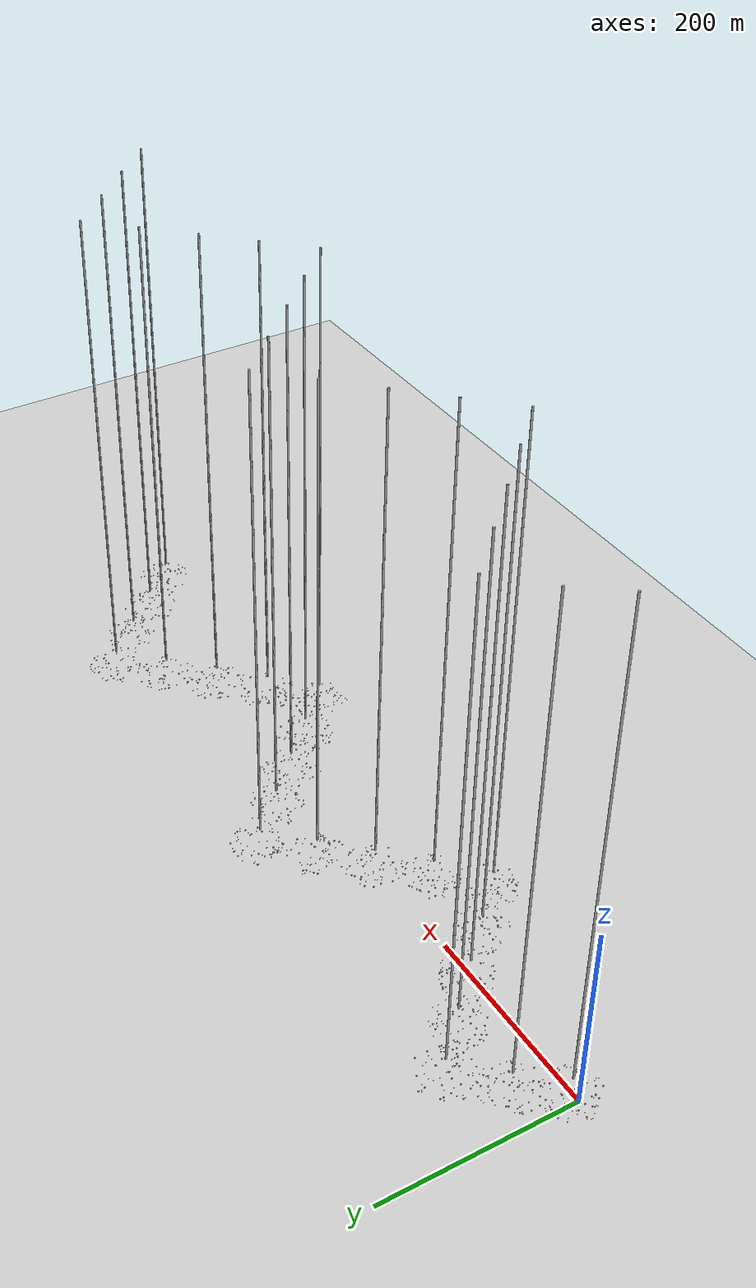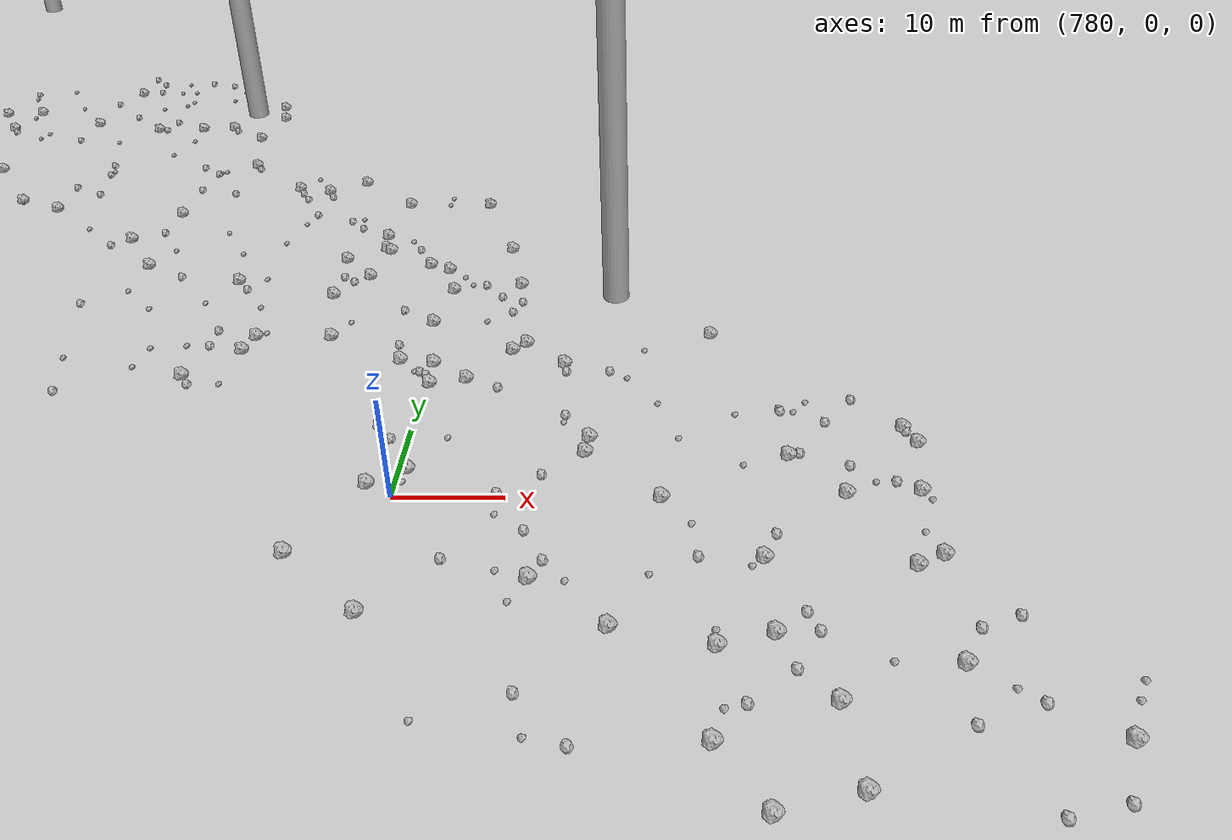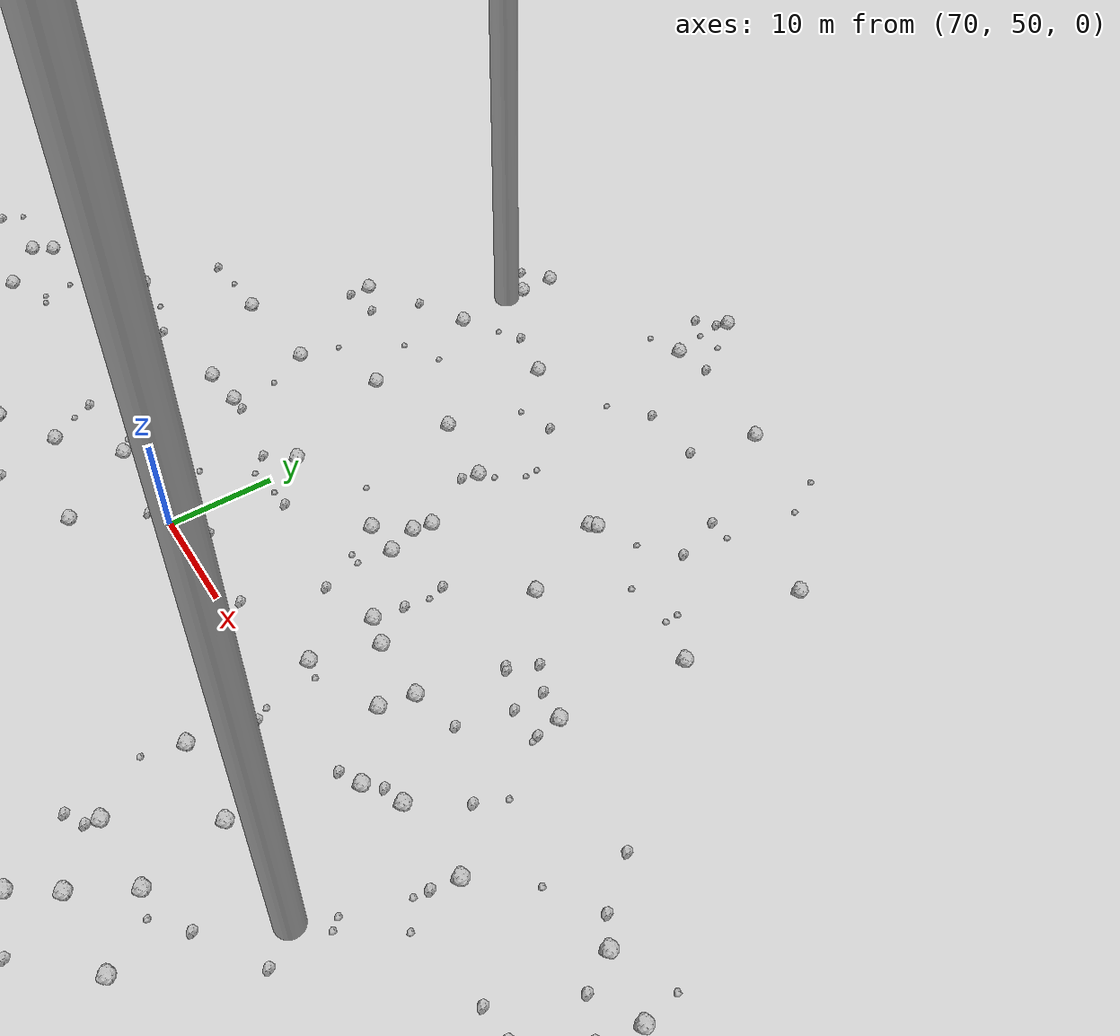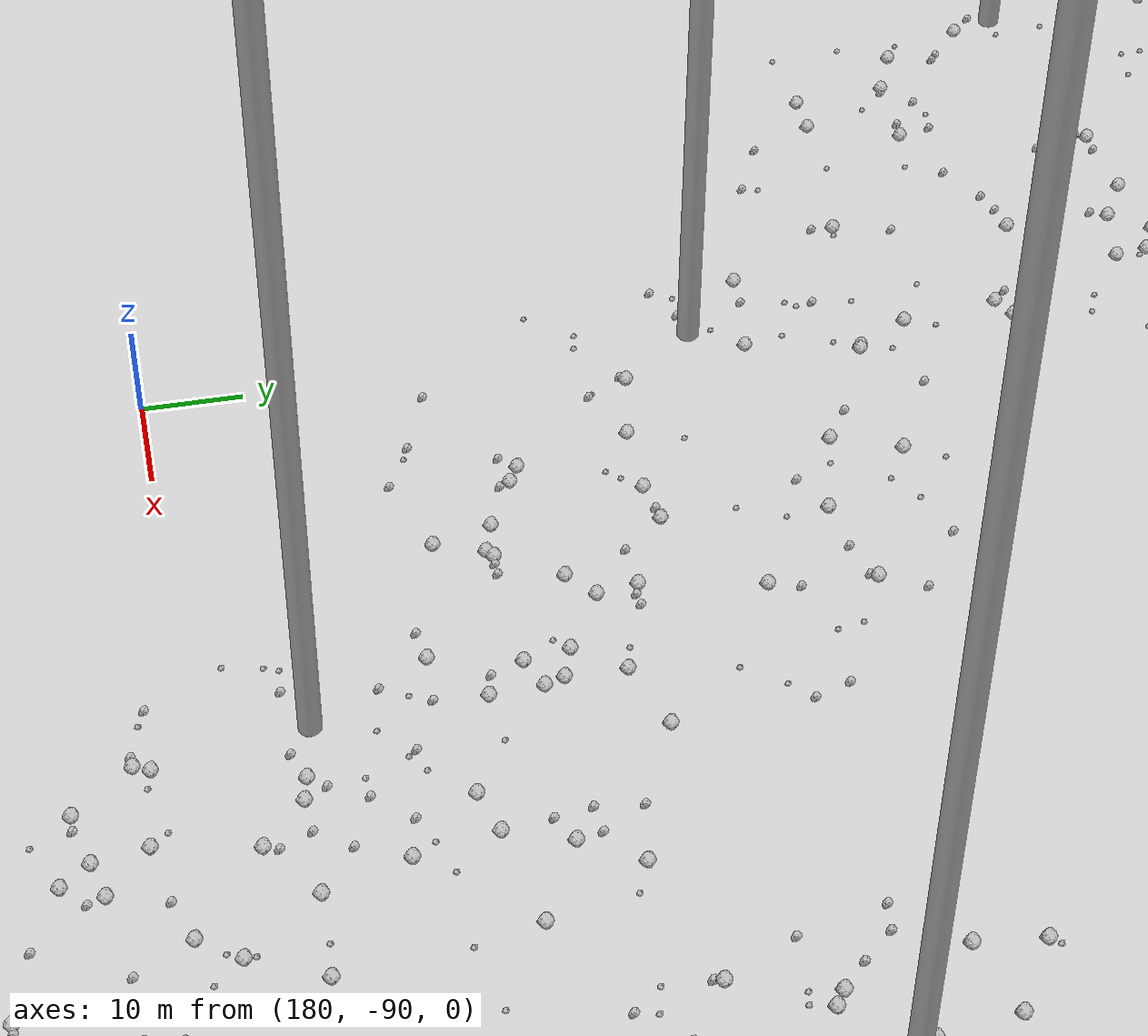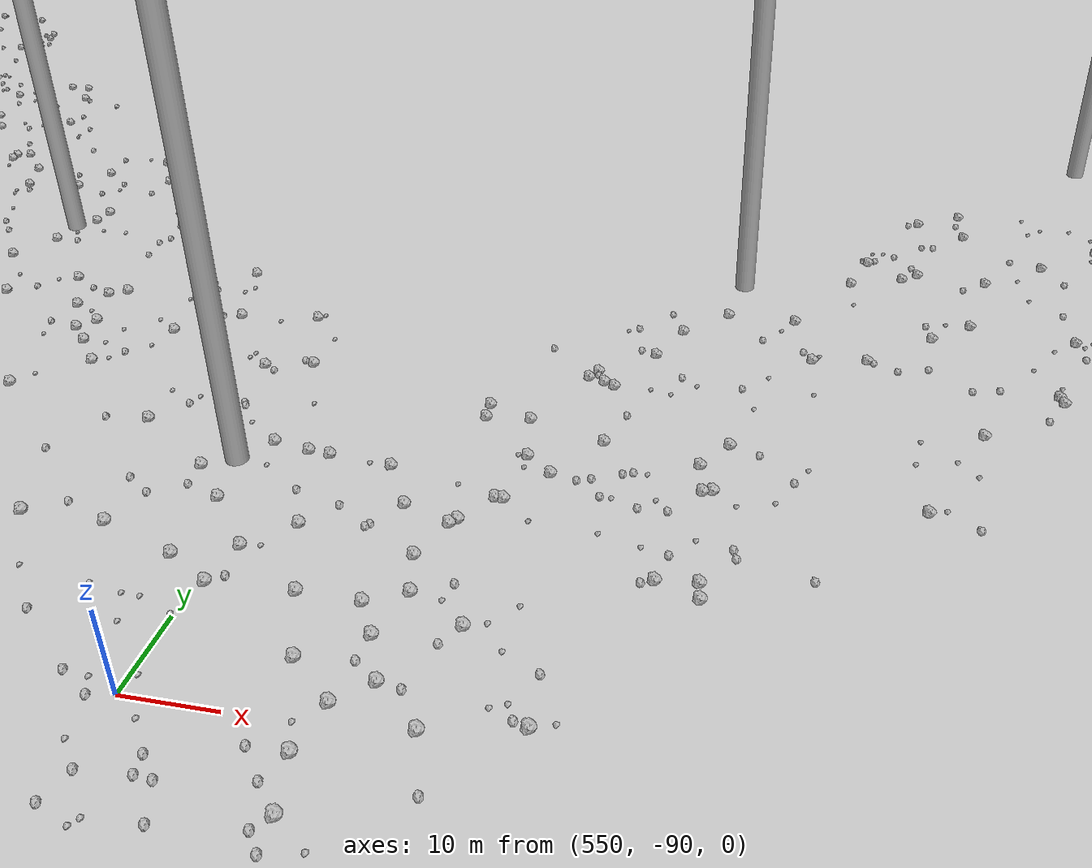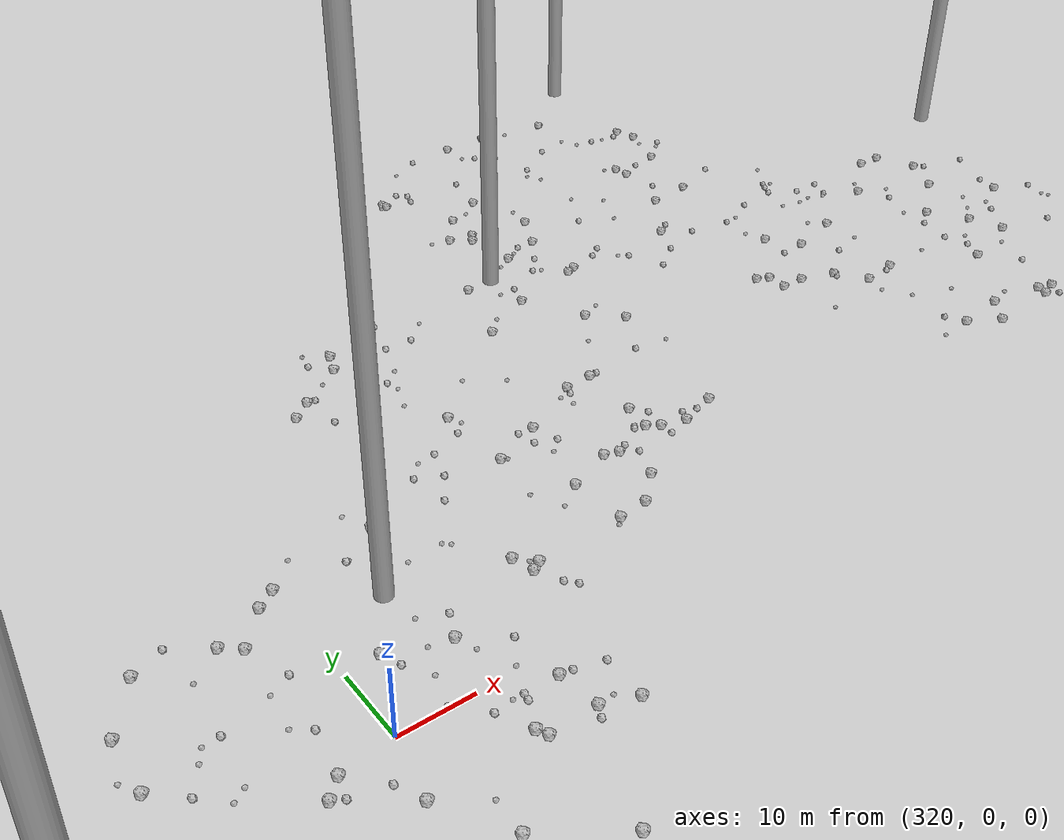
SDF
<sdf version="1.6">
 <world name="default">
  <include><uri>model://custom_ground</uri></include>
  <include><uri>model://sun</uri></include>
  <spherical_coordinates>
   <surface_model>EARTH_WGS84</surface_model>
   <latitude_deg>38.161479</latitude_deg>
   <longitude_deg>-122.454630</longitude_deg>
   <elevation>488.0</elevation>
   <heading_deg>90</heading_deg>
  </spherical_coordinates>
  <model name="rock1_0_0">
   <include><uri>model://rock1</uri><pose>4.535462710996654 24.58052984383427 0.5 0 0 0</pose></include>
  </model>
  <model name="rock1_0_1">
   <include><uri>model://rock1</uri><pose>7.167043263613291 2.67654792124506 0.5 0 0 0</pose></include>
  </model>
  <model name="rock1_0_2">
   <include><uri>model://rock1</uri><pose>12.323201115176857 7.748378981056021 0.5 0 0 0</pose></include>
  </model>
  <model name="rock1_0_3">
   <include><uri>model://rock1</uri><pose>13.173204236284704 29.8120388910953 0.5 0 0 0</pose></include>
  </model>
  <model name="rock1_0_4">
   <include><uri>model://rock1</uri><pose>-7.234948055935044 5.186945250025815 0.5 0 0 0</pose></include>
  </model>
  <model name="rock1_0_5">
   <include><uri>model://rock1</uri><pose>-4.5460510623439365 24.69995138309593 0.5 0 0 0</pose></include>
  </model>
  <model name="rock1_0_6">
   <include><uri>model://rock1</uri><pose>3.8799974532422183 11.01363396571464 0.5 0 0 0</pose></include>
  </model>
  <model name="rock1_0_7">
   <include><uri>model://rock1</uri><pose>-1.3873969861906517 -16.528265217039134 0.5 0 0 0</pose></include>
  </model>
  <model name="rock1_0_8">
   <include><uri>model://rock1</uri><pose>12.338556543773521 -4.726948138950359 0.5 0 0 0</pose></include>
  </model>
  <model name="rock1_0_9">
   <include><uri>model://rock1</uri><pose>-9.888488194988769 -6.58462197014704 0.5 0 0 0</pose></include>
  </model>
  <model name="rock1_0_10">
   <include><uri>model://rock1</uri><pose>27.861423046021223 -18.74561402675891 0.5 0 0 0</pose></include>
  </model>
  <model name="rock1_0_11">
   <include><uri>model://rock1</uri><pose>-4.837437570937862 -2.88808569044766 0.5 0 0 0</pose></include>
  </model>
  <model name="rock1_0_12">
   <include><uri>model://rock1</uri><pose>15.054179648028601 22.87089151948505 0.5 0 0 0</pose></include>
  </model>
  <model name="rock1_0_13">
   <include><uri>model://rock1</uri><pose>2.7740833386331722 -27.41303245514971 0.5 0 0 0</pose></include>
  </model>
  <model name="rock1_0_14">
   <include><uri>model://rock1</uri><pose>-6.086045032021865 -16.458035146851437 0.5 0 0 0</pose></include>
  </model>
  <model name="rock1_0_15">
   <include><uri>model://rock1</uri><pose>-16.112398729155235 3.9093933100914455 0.5 0 0 0</pose></include>
  </model>
  <model name="rock1_0_16">
   <include><uri>model://rock1</uri><pose>5.588375104308373 -22.305449005688644 0.5 0 0 0</pose></include>
  </model>
  <model name="rock1_0_17">
   <include><uri>model://rock1</uri><pose>36.00958301725695 -12.418429209285623 0.5 0 0 0</pose></include>
  </model>
  <model name="rock1_0_18">
   <include><uri>model://rock1</uri><pose>19.896691623579137 -1.749743231738453 0.5 0 0 0</pose></include>
  </model>
  <model name="rock1_0_19">
   <include><uri>model://rock1</uri><pose>36.47203944235663 -5.26925511424167 0.5 0 0 0</pose></include>
  </model>
  <model name="rock1_0_20">
   <include><uri>model://rock1</uri><pose>27.139115976736043 9.484396067048685 0.5 0 0 0</pose></include>
  </model>
  <model name="rock1_0_21">
   <include><uri>model://rock1</uri><pose>24.243678175671768 -3.2538645652865057 0.5 0 0 0</pose></include>
  </model>
  <model name="rock1_0_22">
   <include><uri>model://rock1</uri><pose>29.339767103215543 17.324515482444852 0.5 0 0 0</pose></include>
  </model>
  <model name="rock1_0_23">
   <include><uri>model://rock1</uri><pose>-1.5313394568778023 -12.64860217564135 0.5 0 0 0</pose></include>
  </model>
  <model name="rock1_0_24">
   <include><uri>model://rock1</uri><pose>6.522918308286478 -6.02322666028266 0.5 0 0 0</pose></include>
  </model>
  <model name="rock1_0_25">
   <include><uri>model://rock1</uri><pose>25.549864761352374 -16.901671015106636 0.5 0 0 0</pose></include>
  </model>
  <model name="rock1_0_26">
   <include><uri>model://rock1</uri><pose>-2.1109864241374297 12.08637610167932 0.5 0 0 0</pose></include>
  </model>
  <model name="rock2_0_0">
   <include><uri>model://rock2</uri><pose>28.822303843108784 18.466520301829647 0.3 0 0 0</pose></include>
  </model>
  <model name="rock2_0_1">
   <include><uri>model://rock2</uri><pose>-11.09108862066556 -8.479036978214317 0.3 0 0 0</pose></include>
  </model>
  <model name="rock2_0_2">
   <include><uri>model://rock2</uri><pose>-16.247130234335934 -4.19816828605169 0.3 0 0 0</pose></include>
  </model>
  <model name="rock2_0_3">
   <include><uri>model://rock2</uri><pose>-9.098201783189992 17.52393279860882 0.3 0 0 0</pose></include>
  </model>
  <model name="rock2_0_4">
   <include><uri>model://rock2</uri><pose>12.103162738119686 18.312910396320447 0.3 0 0 0</pose></include>
  </model>
  <model name="rock2_0_5">
   <include><uri>model://rock2</uri><pose>-11.859741004472372 20.498666426879836 0.3 0 0 0</pose></include>
  </model>
  <model name="rock2_0_6">
   <include><uri>model://rock2</uri><pose>6.2596972194040035 28.897398847142313 0.3 0 0 0</pose></include>
  </model>
  <model name="rock2_0_7">
   <include><uri>model://rock2</uri><pose>34.43171985331265 -5.437038438914659 0.3 0 0 0</pose></include>
  </model>
  <model name="rock2_0_8">
   <include><uri>model://rock2</uri><pose>9.761649655377806 -4.296360464234009 0.3 0 0 0</pose></include>
  </model>
  <model name="rock2_0_9">
   <include><uri>model://rock2</uri><pose>-19.768848925853668 1.641319644553331 0.3 0 0 0</pose></include>
  </model>
  <model name="rock2_0_10">
   <include><uri>model://rock2</uri><pose>24.04336416604405 0.834323159023409 0.3 0 0 0</pose></include>
  </model>
  <model name="rock2_0_11">
   <include><uri>model://rock2</uri><pose>-9.46205070282512 8.648686313723445 0.3 0 0 0</pose></include>
  </model>
  <model name="rock2_0_12">
   <include><uri>model://rock2</uri><pose>-4.578779033132957 10.223822723010173 0.3 0 0 0</pose></include>
  </model>
  <model name="rock2_0_13">
   <include><uri>model://rock2</uri><pose>13.046047770489622 2.882050633053545 0.3 0 0 0</pose></include>
  </model>
  <model name="rock2_0_14">
   <include><uri>model://rock2</uri><pose>10.128392296377601 19.085384774464288 0.3 0 0 0</pose></include>
  </model>
  <model name="rock2_0_15">
   <include><uri>model://rock2</uri><pose>-3.195635286352868 -12.968149594630532 0.3 0 0 0</pose></include>
  </model>
  <model name="rock2_0_16">
   <include><uri>model://rock2</uri><pose>7.478099168136453 23.687152498719804 0.3 0 0 0</pose></include>
  </model>
  <model name="rock2_0_17">
   <include><uri>model://rock2</uri><pose>13.727863444748287 7.777075097876718 0.3 0 0 0</pose></include>
  </model>
  <model name="rock2_0_18">
   <include><uri>model://rock2</uri><pose>21.087885446194086 -13.18512010340309 0.3 0 0 0</pose></include>
  </model>
  <model name="rock2_0_19">
   <include><uri>model://rock2</uri><pose>29.517835672265306 13.424001356253406 0.3 0 0 0</pose></include>
  </model>
  <model name="rock2_0_20">
   <include><uri>model://rock2</uri><pose>-11.915754037141657 -11.204487431772723 0.3 0 0 0</pose></include>
  </model>
  <model name="rock2_0_21">
   <include><uri>model://rock2</uri><pose>11.460415166873759 -10.434016471937497 0.3 0 0 0</pose></include>
  </model>
  <model name="rock2_0_22">
   <include><uri>model://rock2</uri><pose>11.329032735116769 -6.890145301183765 0.3 0 0 0</pose></include>
  </model>
  <model name="rock2_0_23">
   <include><uri>model://rock2</uri><pose>-17.88292124176606 4.902774378008253 0.3 0 0 0</pose></include>
  </model>
  <model name="rock2_0_24">
   <include><uri>model://rock2</uri><pose>31.87670030262936 -15.574185514927596 0.3 0 0 0</pose></include>
  </model>
  <model name="rock2_0_25">
   <include><uri>model://rock2</uri><pose>12.057693635531315 -18.277957424013643 0.3 0 0 0</pose></include>
  </model>
  <model name="rock2_0_26">
   <include><uri>model://rock2</uri><pose>22.638097701037438 12.345569281947249 0.3 0 0 0</pose></include>
  </model>
  <model name="rock3_0_0">
   <include><uri>model://rock3</uri><pose>12.183898193080289 16.432527172668735 0.2 0 0 0</pose></include>
  </model>
  <model name="rock3_0_1">
   <include><uri>model://rock3</uri><pose>-6.548904109003399 7.007257632256653 0.2 0 0 0</pose></include>
  </model>
  <model name="rock3_0_2">
   <include><uri>model://rock3</uri><pose>-3.236464322390624 20.579423714968044 0.2 0 0 0</pose></include>
  </model>
  <model name="rock3_0_3">
   <include><uri>model://rock3</uri><pose>8.702711100760158 27.711930925179267 0.2 0 0 0</pose></include>
  </model>
  <model name="rock3_0_4">
   <include><uri>model://rock3</uri><pose>24.497509501330626 -0.7219137848627923 0.2 0 0 0</pose></include>
  </model>
  <model name="rock3_0_5">
   <include><uri>model://rock3</uri><pose>-0.5323089631134188 -14.906048685434047 0.2 0 0 0</pose></include>
  </model>
  <model name="rock3_0_6">
   <include><uri>model://rock3</uri><pose>34.01958861326206 -13.080481152754903 0.2 0 0 0</pose></include>
  </model>
  <model name="rock3_0_7">
   <include><uri>model://rock3</uri><pose>-19.343831572368003 0.09322492203993704 0.2 0 0 0</pose></include>
  </model>
  <model name="rock3_0_8">
   <include><uri>model://rock3</uri><pose>29.309582355458744 4.1801932678488285 0.2 0 0 0</pose></include>
  </model>
  <model name="rock3_0_9">
   <include><uri>model://rock3</uri><pose>14.570735011940542 25.515626639773103 0.2 0 0 0</pose></include>
  </model>
  <model name="rock3_0_10">
   <include><uri>model://rock3</uri><pose>-0.2220269306097009 -17.154459730008284 0.2 0 0 0</pose></include>
  </model>
  <model name="rock3_0_11">
   <include><uri>model://rock3</uri><pose>27.485005216572837 16.750913746579414 0.2 0 0 0</pose></include>
  </model>
  <model name="rock3_0_12">
   <include><uri>model://rock3</uri><pose>0.31004730982349926 21.868109369926735 0.2 0 0 0</pose></include>
  </model>
  <model name="rock3_0_13">
   <include><uri>model://rock3</uri><pose>21.51935955925933 26.497679574068343 0.2 0 0 0</pose></include>
  </model>
  <model name="rock3_0_14">
   <include><uri>model://rock3</uri><pose>10.93437284169666 -29.262609628863384 0.2 0 0 0</pose></include>
  </model>
  <model name="rock3_0_15">
   <include><uri>model://rock3</uri><pose>5.079858578938655 -12.1426450232428 0.2 0 0 0</pose></include>
  </model>
  <model name="rock3_0_16">
   <include><uri>model://rock3</uri><pose>-9.984956118506785 -10.535670689531745 0.2 0 0 0</pose></include>
  </model>
  <model name="rock3_0_17">
   <include><uri>model://rock3</uri><pose>-11.319767329289538 2.426025144571163 0.2 0 0 0</pose></include>
  </model>
  <model name="rock3_0_18">
   <include><uri>model://rock3</uri><pose>24.005406312492845 4.256785656672577 0.2 0 0 0</pose></include>
  </model>
  <model name="rock3_0_19">
   <include><uri>model://rock3</uri><pose>23.55599600024913 -23.147678560050792 0.2 0 0 0</pose></include>
  </model>
  <model name="rock3_0_20">
   <include><uri>model://rock3</uri><pose>8.904390513772775 9.201101682222657 0.2 0 0 0</pose></include>
  </model>
  <model name="rock3_0_21">
   <include><uri>model://rock3</uri><pose>12.196021003452437 -27.546411923496365 0.2 0 0 0</pose></include>
  </model>
  <model name="rock3_0_22">
   <include><uri>model://rock3</uri><pose>34.21193308517294 12.223768741800342 0.2 0 0 0</pose></include>
  </model>
  <model name="rock3_0_23">
   <include><uri>model://rock3</uri><pose>10.809946441867623 -24.691517392443068 0.2 0 0 0</pose></include>
  </model>
  <model name="rock3_0_24">
   <include><uri>model://rock3</uri><pose>29.336952823456265 -10.056523702951196 0.2 0 0 0</pose></include>
  </model>
  <model name="rock3_0_25">
   <include><uri>model://rock3</uri><pose>8.895030004359008 23.38235984109417 0.2 0 0 0</pose></include>
  </model>
  <model name="rock3_0_26">
   <include><uri>model://rock3</uri><pose>8.004270476864285 27.958463885488285 0.2 0 0 0</pose></include>
  </model>
  <model name="rock1_1_0">
   <include><uri>model://rock1</uri><pose>42.79815094659439 39.78196465593841 0.5 0 0 0</pose></include>
  </model>
  <model name="rock1_1_1">
   <include><uri>model://rock1</uri><pose>59.64757644038319 49.7864508825913 0.5 0 0 0</pose></include>
  </model>
  <model name="rock1_1_2">
   <include><uri>model://rock1</uri><pose>46.857261901804264 69.13750155950726 0.5 0 0 0</pose></include>
  </model>
  <model name="rock1_1_3">
   <include><uri>model://rock1</uri><pose>26.436561967187306 54.981483855237514 0.5 0 0 0</pose></include>
  </model>
  <model name="rock1_1_4">
   <include><uri>model://rock1</uri><pose>29.714094180501583 49.31577104057859 0.5 0 0 0</pose></include>
  </model>
  <model name="rock1_1_5">
   <include><uri>model://rock1</uri><pose>58.68498300946894 61.618640025664554 0.5 0 0 0</pose></include>
  </model>
  <model name="rock1_1_6">
   <include><uri>model://rock1</uri><pose>33.11909849087897 16.329786325384074 0.5 0 0 0</pose></include>
  </model>
  <model name="rock1_1_7">
   <include><uri>model://rock1</uri><pose>37.21995655421885 61.07012498783877 0.5 0 0 0</pose></include>
  </model>
  <model name="rock1_1_8">
   <include><uri>model://rock1</uri><pose>64.85653218315781 42.47647511317193 0.5 0 0 0</pose></include>
  </model>
  <model name="rock1_1_9">
   <include><uri>model://rock1</uri><pose>12.099342417458455 39.377594859536224 0.5 0 0 0</pose></include>
  </model>
  <model name="rock1_1_10">
   <include><uri>model://rock1</uri><pose>50.98599683677867 55.81680337512153 0.5 0 0 0</pose></include>
  </model>
  <model name="rock1_1_11">
   <include><uri>model://rock1</uri><pose>44.34594273224775 36.27029793476247 0.5 0 0 0</pose></include>
  </model>
  <model name="rock1_1_12">
   <include><uri>model://rock1</uri><pose>62.89637260117584 52.65115161108276 0.5 0 0 0</pose></include>
  </model>
  <model name="rock1_1_13">
   <include><uri>model://rock1</uri><pose>37.707674241452466 34.70597750901251 0.5 0 0 0</pose></include>
  </model>
  <model name="rock1_1_14">
   <include><uri>model://rock1</uri><pose>36.26366091769251 20.165821228987685 0.5 0 0 0</pose></include>
  </model>
  <model name="rock1_1_15">
   <include><uri>model://rock1</uri><pose>29.38270772855569 26.038023648214367 0.5 0 0 0</pose></include>
  </model>
  <model name="rock1_1_16">
   <include><uri>model://rock1</uri><pose>60.90062900787615 24.49839729551931 0.5 0 0 0</pose></include>
  </model>
  <model name="rock1_1_17">
   <include><uri>model://rock1</uri><pose>48.402226969119376 41.507472612260386 0.5 0 0 0</pose></include>
  </model>
  <model name="rock1_1_18">
   <include><uri>model://rock1</uri><pose>53.99076534674704 31.873178888317508 0.5 0 0 0</pose></include>
  </model>
  <model name="rock1_1_19">
   <include><uri>model://rock1</uri><pose>54.46080701831109 61.22002394830981 0.5 0 0 0</pose></include>
  </model>
  <model name="rock1_1_20">
   <include><uri>model://rock1</uri><pose>20.474538396361964 24.56558293908868 0.5 0 0 0</pose></include>
  </model>
  <model name="rock1_1_21">
   <include><uri>model://rock1</uri><pose>13.664230811030585 47.2243267372784 0.5 0 0 0</pose></include>
  </model>
  <model name="rock1_1_22">
   <include><uri>model://rock1</uri><pose>54.398311566451525 44.97506951262021 0.5 0 0 0</pose></include>
  </model>
  <model name="rock1_1_23">
   <include><uri>model://rock1</uri><pose>14.879215686600409 48.651852547375555 0.5 0 0 0</pose></include>
  </model>
  <model name="rock1_1_24">
   <include><uri>model://rock1</uri><pose>25.194958559879446 53.06866414897002 0.5 0 0 0</pose></include>
  </model>
  <model name="rock1_1_25">
   <include><uri>model://rock1</uri><pose>47.30806853647661 11.479790107808876 0.5 0 0 0</pose></include>
  </model>
  <model name="rock1_1_26">
   <include><uri>model://rock1</uri><pose>55.213305875339564 32.09108983786463 0.5 0 0 0</pose></include>
  </model>
  <model name="rock2_1_0">
   <include><uri>model://rock2</uri><pose>38.77014019813248 32.40231664902487 0.3 0 0 0</pose></include>
  </model>
  <model name="rock2_1_1">
   <include><uri>model://rock2</uri><pose>45.578503687886254 59.736752860995544 0.3 0 0 0</pose></include>
  </model>
  <model name="rock2_1_2">
   <include><uri>model://rock2</uri><pose>51.65142096080178 49.42555626093053 0.3 0 0 0</pose></include>
  </model>
  <model name="rock2_1_3">
   <include><uri>model://rock2</uri><pose>47.8996986563745 32.08791139707369 0.3 0 0 0</pose></include>
  </model>
  <model name="rock2_1_4">
   <include><uri>model://rock2</uri><pose>34.91747465357701 26.702512760233784 0.3 0 0 0</pose></include>
  </model>
  <model name="rock2_1_5">
   <include><uri>model://rock2</uri><pose>63.11702139348847 24.418596773199923 0.3 0 0 0</pose></include>
  </model>
  <model name="rock2_1_6">
   <include><uri>model://rock2</uri><pose>46.70686217176936 56.614031023986 0.3 0 0 0</pose></include>
  </model>
  <model name="rock2_1_7">
   <include><uri>model://rock2</uri><pose>38.96182722081171 17.290440528208016 0.3 0 0 0</pose></include>
  </model>
  <model name="rock2_1_8">
   <include><uri>model://rock2</uri><pose>20.60443232030775 44.83966575029039 0.3 0 0 0</pose></include>
  </model>
  <model name="rock2_1_9">
   <include><uri>model://rock2</uri><pose>60.22904973609432 61.719502843495 0.3 0 0 0</pose></include>
  </model>
  <model name="rock2_1_10">
   <include><uri>model://rock2</uri><pose>20.016660709534285 47.73967281656226 0.3 0 0 0</pose></include>
  </model>
  <model name="rock2_1_11">
   <include><uri>model://rock2</uri><pose>54.053146209425734 25.249133374355225 0.3 0 0 0</pose></include>
  </model>
  <model name="rock2_1_12">
   <include><uri>model://rock2</uri><pose>32.29850452162841 61.946127669734146 0.3 0 0 0</pose></include>
  </model>
  <model name="rock2_1_13">
   <include><uri>model://rock2</uri><pose>28.372605853385707 43.93970664574231 0.3 0 0 0</pose></include>
  </model>
  <model name="rock2_1_14">
   <include><uri>model://rock2</uri><pose>33.45746515792797 11.993790396186874 0.3 0 0 0</pose></include>
  </model>
  <model name="rock2_1_15">
   <include><uri>model://rock2</uri><pose>39.459424049934725 28.782184305085057 0.3 0 0 0</pose></include>
  </model>
  <model name="rock2_1_16">
   <include><uri>model://rock2</uri><pose>36.28394664810271 39.83027710500932 0.3 0 0 0</pose></include>
  </model>
  <model name="rock2_1_17">
   <include><uri>model://rock2</uri><pose>17.92912542907827 52.094931721421325 0.3 0 0 0</pose></include>
  </model>
  <model name="rock2_1_18">
   <include><uri>model://rock2</uri><pose>67.97943271826175 48.79976390520053 0.3 0 0 0</pose></include>
  </model>
  <model name="rock2_1_19">
   <include><uri>model://rock2</uri><pose>56.13929873897199 39.081236923337805 0.3 0 0 0</pose></include>
  </model>
  <model name="rock2_1_20">
   <include><uri>model://rock2</uri><pose>38.999729571854644 68.85144499218558 0.3 0 0 0</pose></include>
  </model>
  <model name="rock2_1_21">
   <include><uri>model://rock2</uri><pose>42.62993059779015 30.220246169897138 0.3 0 0 0</pose></include>
  </model>
  <model name="rock2_1_22">
   <include><uri>model://rock2</uri><pose>20.35964327292537 36.26207136678954 0.3 0 0 0</pose></include>
  </model>
  <model name="rock2_1_23">
   <include><uri>model://rock2</uri><pose>50.297254272691504 20.976096954956766 0.3 0 0 0</pose></include>
  </model>
  <model name="rock2_1_24">
   <include><uri>model://rock2</uri><pose>36.92553474615549 23.406600368551217 0.3 0 0 0</pose></include>
  </model>
  <model name="rock2_1_25">
   <include><uri>model://rock2</uri><pose>26.72291964294626 27.62417409445421 0.3 0 0 0</pose></include>
  </model>
  <model name="rock2_1_26">
   <include><uri>model://rock2</uri><pose>35.67141803252694 21.05505153615856 0.3 0 0 0</pose></include>
  </model>
  <model name="rock3_1_0">
   <include><uri>model://rock3</uri><pose>50.439016311765165 28.338381252819268 0.2 0 0 0</pose></include>
  </model>
  <model name="rock3_1_1">
   <include><uri>model://rock3</uri><pose>56.06778341260729 18.21180957747346 0.2 0 0 0</pose></include>
  </model>
  <model name="rock3_1_2">
   <include><uri>model://rock3</uri><pose>33.33538235802728 51.5408222075752 0.2 0 0 0</pose></include>
  </model>
  <model name="rock3_1_3">
   <include><uri>model://rock3</uri><pose>64.9650600784725 33.80937982315594 0.2 0 0 0</pose></include>
  </model>
  <model name="rock3_1_4">
   <include><uri>model://rock3</uri><pose>60.22915519715825 51.613095438035344 0.2 0 0 0</pose></include>
  </model>
  <model name="rock3_1_5">
   <include><uri>model://rock3</uri><pose>40.77319150951959 14.90747037617539 0.2 0 0 0</pose></include>
  </model>
  <model name="rock3_1_6">
   <include><uri>model://rock3</uri><pose>47.198514746544305 13.674773897967764 0.2 0 0 0</pose></include>
  </model>
  <model name="rock3_1_7">
   <include><uri>model://rock3</uri><pose>32.91351085926207 54.360876988711 0.2 0 0 0</pose></include>
  </model>
  <model name="rock3_1_8">
   <include><uri>model://rock3</uri><pose>41.47797519657868 61.078450616406066 0.2 0 0 0</pose></include>
  </model>
  <model name="rock3_1_9">
   <include><uri>model://rock3</uri><pose>18.628006472474972 54.180534717004626 0.2 0 0 0</pose></include>
  </model>
  <model name="rock3_1_10">
   <include><uri>model://rock3</uri><pose>22.38370217449832 40.92920476360935 0.2 0 0 0</pose></include>
  </model>
  <model name="rock3_1_11">
   <include><uri>model://rock3</uri><pose>30.833621356307685 58.493857537566505 0.2 0 0 0</pose></include>
  </model>
  <model name="rock3_1_12">
   <include><uri>model://rock3</uri><pose>61.92915201702574 23.673008153287377 0.2 0 0 0</pose></include>
  </model>
  <model name="rock3_1_13">
   <include><uri>model://rock3</uri><pose>65.2501021636514 27.727239061353878 0.2 0 0 0</pose></include>
  </model>
  <model name="rock3_1_14">
   <include><uri>model://rock3</uri><pose>65.54579389294074 54.875857806145646 0.2 0 0 0</pose></include>
  </model>
  <model name="rock3_1_15">
   <include><uri>model://rock3</uri><pose>52.410514539905506 47.58348501566585 0.2 0 0 0</pose></include>
  </model>
  <model name="rock3_1_16">
   <include><uri>model://rock3</uri><pose>20.601478870525565 42.658715254126115 0.2 0 0 0</pose></include>
  </model>
  <model name="rock3_1_17">
   <include><uri>model://rock3</uri><pose>15.409011543848926 46.47953843960942 0.2 0 0 0</pose></include>
  </model>
  <model name="rock3_1_18">
   <include><uri>model://rock3</uri><pose>34.370399871109555 51.18258829443329 0.2 0 0 0</pose></include>
  </model>
  <model name="rock3_1_19">
   <include><uri>model://rock3</uri><pose>55.699548360520595 36.08530709756619 0.2 0 0 0</pose></include>
  </model>
  <model name="rock3_1_20">
   <include><uri>model://rock3</uri><pose>32.41641388303323 32.32413714305386 0.2 0 0 0</pose></include>
  </model>
  <model name="rock3_1_21">
   <include><uri>model://rock3</uri><pose>57.9682326447369 50.82809130703681 0.2 0 0 0</pose></include>
  </model>
  <model name="rock3_1_22">
   <include><uri>model://rock3</uri><pose>62.95371459459906 30.710877806753835 0.2 0 0 0</pose></include>
  </model>
  <model name="rock3_1_23">
   <include><uri>model://rock3</uri><pose>39.07648416191897 23.085186713545635 0.2 0 0 0</pose></include>
  </model>
  <model name="rock3_1_24">
   <include><uri>model://rock3</uri><pose>33.90506688839446 61.19471571467396 0.2 0 0 0</pose></include>
  </model>
  <model name="rock3_1_25">
   <include><uri>model://rock3</uri><pose>64.66233670503037 27.68417853012014 0.2 0 0 0</pose></include>
  </model>
  <model name="rock3_1_26">
   <include><uri>model://rock3</uri><pose>42.29753767488263 69.18374467083814 0.2 0 0 0</pose></include>
  </model>
  <model name="rock1_2_0">
   <include><uri>model://rock1</uri><pose>76.13419544959427 109.2770991478103 0.5 0 0 0</pose></include>
  </model>
  <model name="rock1_2_1">
   <include><uri>model://rock1</uri><pose>107.09450978783636 92.68397547399022 0.5 0 0 0</pose></include>
  </model>
  <model name="rock1_2_2">
   <include><uri>model://rock1</uri><pose>60.14070395363362 97.8094275014886 0.5 0 0 0</pose></include>
  </model>
  <model name="rock1_2_3">
   <include><uri>model://rock1</uri><pose>92.40254581040776 59.521733610986885 0.5 0 0 0</pose></include>
  </model>
  <model name="rock1_2_4">
   <include><uri>model://rock1</uri><pose>82.84762461461688 68.01924239255402 0.5 0 0 0</pose></include>
  </model>
  <model name="rock1_2_5">
   <include><uri>model://rock1</uri><pose>69.15797661714825 63.26364607181703 0.5 0 0 0</pose></include>
  </model>
  <model name="rock1_2_6">
   <include><uri>model://rock1</uri><pose>71.40574101079933 88.96895384329713 0.5 0 0 0</pose></include>
  </model>
  <model name="rock1_2_7">
   <include><uri>model://rock1</uri><pose>73.18402647078969 77.43397517926437 0.5 0 0 0</pose></include>
  </model>
  <model name="rock1_2_8">
   <include><uri>model://rock1</uri><pose>80.26466128604365 76.517797344672 0.5 0 0 0</pose></include>
  </model>
  <model name="rock1_2_9">
   <include><uri>model://rock1</uri><pose>97.70612656816834 56.31682352100039 0.5 0 0 0</pose></include>
  </model>
  <model name="rock1_2_10">
   <include><uri>model://rock1</uri><pose>50.8676200609019 80.87817153945123 0.5 0 0 0</pose></include>
  </model>
  <model name="rock1_2_11">
   <include><uri>model://rock1</uri><pose>80.54948845089308 65.03910710522939 0.5 0 0 0</pose></include>
  </model>
  <model name="rock1_2_12">
   <include><uri>model://rock1</uri><pose>83.17288225877725 69.78895803294569 0.5 0 0 0</pose></include>
  </model>
  <model name="rock1_2_13">
   <include><uri>model://rock1</uri><pose>94.66665090795672 73.48837089325579 0.5 0 0 0</pose></include>
  </model>
  <model name="rock1_2_14">
   <include><uri>model://rock1</uri><pose>91.00789134072183 81.65311190327344 0.5 0 0 0</pose></include>
  </model>
  <model name="rock1_2_15">
   <include><uri>model://rock1</uri><pose>56.527774046151414 69.95418321896882 0.5 0 0 0</pose></include>
  </model>
  <model name="rock1_2_16">
   <include><uri>model://rock1</uri><pose>106.58283321509495 67.99306938859839 0.5 0 0 0</pose></include>
  </model>
  <model name="rock1_2_17">
   <include><uri>model://rock1</uri><pose>89.64522631913024 60.2328735524363 0.5 0 0 0</pose></include>
  </model>
  <model name="rock1_2_18">
   <include><uri>model://rock1</uri><pose>90.28856046251303 101.41624562557385 0.5 0 0 0</pose></include>
  </model>
  <model name="rock1_2_19">
   <include><uri>model://rock1</uri><pose>64.05720873763686 74.5456659515016 0.5 0 0 0</pose></include>
  </model>
  <model name="rock1_2_20">
   <include><uri>model://rock1</uri><pose>90.61892139320362 53.650576616987365 0.5 0 0 0</pose></include>
  </model>
  <model name="rock1_2_21">
   <include><uri>model://rock1</uri><pose>83.94630551566382 65.20915330656973 0.5 0 0 0</pose></include>
  </model>
  <model name="rock1_2_22">
   <include><uri>model://rock1</uri><pose>60.867295262847975 86.56055299152182 0.5 0 0 0</pose></include>
  </model>
  <model name="rock1_2_23">
   <include><uri>model://rock1</uri><pose>60.189818509009235 94.32560476825971 0.5 0 0 0</pose></include>
  </model>
  <model name="rock1_2_24">
   <include><uri>model://rock1</uri><pose>76.8412162872429 102.48986030251154 0.5 0 0 0</pose></include>
  </model>
  <model name="rock1_2_25">
   <include><uri>model://rock1</uri><pose>107.5010984935976 79.93691310016739 0.5 0 0 0</pose></include>
  </model>
  <model name="rock1_2_26">
   <include><uri>model://rock1</uri><pose>91.51651291805445 82.15017657669267 0.5 0 0 0</pose></include>
  </model>
  <model name="rock2_2_0">
   <include><uri>model://rock2</uri><pose>84.39862534116402 58.43664398274503 0.3 0 0 0</pose></include>
  </model>
  <model name="rock2_2_1">
   <include><uri>model://rock2</uri><pose>103.8542863181068 65.4401120603085 0.3 0 0 0</pose></include>
  </model>
  <model name="rock2_2_2">
   <include><uri>model://rock2</uri><pose>57.512119715299235 95.88717044270399 0.3 0 0 0</pose></include>
  </model>
  <model name="rock2_2_3">
   <include><uri>model://rock2</uri><pose>99.86283392804053 67.13605294669301 0.3 0 0 0</pose></include>
  </model>
  <model name="rock2_2_4">
   <include><uri>model://rock2</uri><pose>100.23350347356129 66.99379957696843 0.3 0 0 0</pose></include>
  </model>
  <model name="rock2_2_5">
   <include><uri>model://rock2</uri><pose>67.1052488967147 60.699676689637236 0.3 0 0 0</pose></include>
  </model>
  <model name="rock2_2_6">
   <include><uri>model://rock2</uri><pose>54.256402742639935 79.3863649966964 0.3 0 0 0</pose></include>
  </model>
  <model name="rock2_2_7">
   <include><uri>model://rock2</uri><pose>50.74479673367968 78.74076252009024 0.3 0 0 0</pose></include>
  </model>
  <model name="rock2_2_8">
   <include><uri>model://rock2</uri><pose>103.67583752038968 68.3521583359383 0.3 0 0 0</pose></include>
  </model>
  <model name="rock2_2_9">
   <include><uri>model://rock2</uri><pose>79.78211417223889 74.98836335325025 0.3 0 0 0</pose></include>
  </model>
  <model name="rock2_2_10">
   <include><uri>model://rock2</uri><pose>102.58853122857579 60.61563284248534 0.3 0 0 0</pose></include>
  </model>
  <model name="rock2_2_11">
   <include><uri>model://rock2</uri><pose>89.93114177486576 63.12458692840112 0.3 0 0 0</pose></include>
  </model>
  <model name="rock2_2_12">
   <include><uri>model://rock2</uri><pose>73.86602371705138 106.8677954724773 0.3 0 0 0</pose></include>
  </model>
  <model name="rock2_2_13">
   <include><uri>model://rock2</uri><pose>75.62063029194789 108.22933398026132 0.3 0 0 0</pose></include>
  </model>
  <model name="rock2_2_14">
   <include><uri>model://rock2</uri><pose>81.77833254808233 51.513844067304156 0.3 0 0 0</pose></include>
  </model>
  <model name="rock2_2_15">
   <include><uri>model://rock2</uri><pose>55.961571410047725 84.1525691862922 0.3 0 0 0</pose></include>
  </model>
  <model name="rock2_2_16">
   <include><uri>model://rock2</uri><pose>73.75154130529316 59.70382178895709 0.3 0 0 0</pose></include>
  </model>
  <model name="rock2_2_17">
   <include><uri>model://rock2</uri><pose>78.7948203873118 85.50800577531092 0.3 0 0 0</pose></include>
  </model>
  <model name="rock2_2_18">
   <include><uri>model://rock2</uri><pose>101.22961445797489 69.61581043999684 0.3 0 0 0</pose></include>
  </model>
  <model name="rock2_2_19">
   <include><uri>model://rock2</uri><pose>80.41530712351704 103.18734543647304 0.3 0 0 0</pose></include>
  </model>
  <model name="rock2_2_20">
   <include><uri>model://rock2</uri><pose>66.31133573748237 90.1590206028506 0.3 0 0 0</pose></include>
  </model>
  <model name="rock2_2_21">
   <include><uri>model://rock2</uri><pose>88.6829104806906 94.890253262875 0.3 0 0 0</pose></include>
  </model>
  <model name="rock2_2_22">
   <include><uri>model://rock2</uri><pose>82.67660608105078 94.81037688613054 0.3 0 0 0</pose></include>
  </model>
  <model name="rock2_2_23">
   <include><uri>model://rock2</uri><pose>98.29070521728399 86.777622708221 0.3 0 0 0</pose></include>
  </model>
  <model name="rock2_2_24">
   <include><uri>model://rock2</uri><pose>96.71827411374709 91.22613028675951 0.3 0 0 0</pose></include>
  </model>
  <model name="rock2_2_25">
   <include><uri>model://rock2</uri><pose>89.82329804148583 66.98005333329681 0.3 0 0 0</pose></include>
  </model>
  <model name="rock2_2_26">
   <include><uri>model://rock2</uri><pose>73.19868800843956 52.44927009652141 0.3 0 0 0</pose></include>
  </model>
  <model name="rock3_2_0">
   <include><uri>model://rock3</uri><pose>57.299329989594455 73.83826369920816 0.2 0 0 0</pose></include>
  </model>
  <model name="rock3_2_1">
   <include><uri>model://rock3</uri><pose>98.83358050754495 80.68988541412023 0.2 0 0 0</pose></include>
  </model>
  <model name="rock3_2_2">
   <include><uri>model://rock3</uri><pose>64.10996546838156 88.82487974250805 0.2 0 0 0</pose></include>
  </model>
  <model name="rock3_2_3">
   <include><uri>model://rock3</uri><pose>83.34868595142231 62.08508460185963 0.2 0 0 0</pose></include>
  </model>
  <model name="rock3_2_4">
   <include><uri>model://rock3</uri><pose>75.8501591456918 67.00786934577035 0.2 0 0 0</pose></include>
  </model>
  <model name="rock3_2_5">
   <include><uri>model://rock3</uri><pose>60.674755440784566 79.64332181043265 0.2 0 0 0</pose></include>
  </model>
  <model name="rock3_2_6">
   <include><uri>model://rock3</uri><pose>73.4328579225571 101.38343337587041 0.2 0 0 0</pose></include>
  </model>
  <model name="rock3_2_7">
   <include><uri>model://rock3</uri><pose>103.29327267272477 81.08922489411017 0.2 0 0 0</pose></include>
  </model>
  <model name="rock3_2_8">
   <include><uri>model://rock3</uri><pose>75.23757198608347 84.42852184350622 0.2 0 0 0</pose></include>
  </model>
  <model name="rock3_2_9">
   <include><uri>model://rock3</uri><pose>90.21264649604271 65.41365214250084 0.2 0 0 0</pose></include>
  </model>
  <model name="rock3_2_10">
   <include><uri>model://rock3</uri><pose>95.06340228802509 83.96549297890817 0.2 0 0 0</pose></include>
  </model>
  <model name="rock3_2_11">
   <include><uri>model://rock3</uri><pose>78.31028815238616 106.25954914118128 0.2 0 0 0</pose></include>
  </model>
  <model name="rock3_2_12">
   <include><uri>model://rock3</uri><pose>97.6619426034625 102.01480726705857 0.2 0 0 0</pose></include>
  </model>
  <model name="rock3_2_13">
   <include><uri>model://rock3</uri><pose>68.6281518664714 59.121994019355135 0.2 0 0 0</pose></include>
  </model>
  <model name="rock3_2_14">
   <include><uri>model://rock3</uri><pose>103.24936759060728 82.34106314237906 0.2 0 0 0</pose></include>
  </model>
  <model name="rock3_2_15">
   <include><uri>model://rock3</uri><pose>79.09071572916606 91.89871983513163 0.2 0 0 0</pose></include>
  </model>
  <model name="rock3_2_16">
   <include><uri>model://rock3</uri><pose>71.76852477606234 59.58388429203105 0.2 0 0 0</pose></include>
  </model>
  <model name="rock3_2_17">
   <include><uri>model://rock3</uri><pose>82.65444203346097 80.20971739553997 0.2 0 0 0</pose></include>
  </model>
  <model name="rock3_2_18">
   <include><uri>model://rock3</uri><pose>58.450194838090006 66.02417713267548 0.2 0 0 0</pose></include>
  </model>
  <model name="rock3_2_19">
   <include><uri>model://rock3</uri><pose>64.36739239440897 81.54219816580371 0.2 0 0 0</pose></include>
  </model>
  <model name="rock3_2_20">
   <include><uri>model://rock3</uri><pose>82.56750821985247 81.4800160294048 0.2 0 0 0</pose></include>
  </model>
  <model name="rock3_2_21">
   <include><uri>model://rock3</uri><pose>98.77574348615155 91.26452575880685 0.2 0 0 0</pose></include>
  </model>
  <model name="rock3_2_22">
   <include><uri>model://rock3</uri><pose>82.2423275076093 62.103571411134766 0.2 0 0 0</pose></include>
  </model>
  <model name="rock3_2_23">
   <include><uri>model://rock3</uri><pose>92.23548749507196 53.34312744061269 0.2 0 0 0</pose></include>
  </model>
  <model name="rock3_2_24">
   <include><uri>model://rock3</uri><pose>81.19929030477994 77.68071389899126 0.2 0 0 0</pose></include>
  </model>
  <model name="rock3_2_25">
   <include><uri>model://rock3</uri><pose>75.90708450814887 105.89134621383216 0.2 0 0 0</pose></include>
  </model>
  <model name="rock3_2_26">
   <include><uri>model://rock3</uri><pose>99.69207833596911 98.38400055434599 0.2 0 0 0</pose></include>
  </model>
  <model name="rock1_3_0">
   <include><uri>model://rock1</uri><pose>96.7875247000467 25.576969197019338 0.5 0 0 0</pose></include>
  </model>
  <model name="rock1_3_1">
   <include><uri>model://rock1</uri><pose>124.52153083968723 60.26488878719557 0.5 0 0 0</pose></include>
  </model>
  <model name="rock1_3_2">
   <include><uri>model://rock1</uri><pose>136.39506433797294 48.67092771896209 0.5 0 0 0</pose></include>
  </model>
  <model name="rock1_3_3">
   <include><uri>model://rock1</uri><pose>130.19573265031175 59.222815987852265 0.5 0 0 0</pose></include>
  </model>
  <model name="rock1_3_4">
   <include><uri>model://rock1</uri><pose>130.32974670525073 27.561746334095368 0.5 0 0 0</pose></include>
  </model>
  <model name="rock1_3_5">
   <include><uri>model://rock1</uri><pose>130.7487375581718 38.13923859675584 0.5 0 0 0</pose></include>
  </model>
  <model name="rock1_3_6">
   <include><uri>model://rock1</uri><pose>98.3125490254042 59.44570800947369 0.5 0 0 0</pose></include>
  </model>
  <model name="rock1_3_7">
   <include><uri>model://rock1</uri><pose>123.56597240051663 20.96484848930715 0.5 0 0 0</pose></include>
  </model>
  <model name="rock1_3_8">
   <include><uri>model://rock1</uri><pose>134.55848000673598 26.9350686010103 0.5 0 0 0</pose></include>
  </model>
  <model name="rock1_3_9">
   <include><uri>model://rock1</uri><pose>137.67594933245138 28.609274161244375 0.5 0 0 0</pose></include>
  </model>
  <model name="rock1_3_10">
   <include><uri>model://rock1</uri><pose>100.3689754607753 41.61555008348662 0.5 0 0 0</pose></include>
  </model>
  <model name="rock1_3_11">
   <include><uri>model://rock1</uri><pose>119.61560486688366 35.03790643229742 0.5 0 0 0</pose></include>
  </model>
  <model name="rock1_3_12">
   <include><uri>model://rock1</uri><pose>97.3811941447403 45.05616833717147 0.5 0 0 0</pose></include>
  </model>
  <model name="rock1_3_13">
   <include><uri>model://rock1</uri><pose>99.28309036396674 29.222126210737475 0.5 0 0 0</pose></include>
  </model>
  <model name="rock1_3_14">
   <include><uri>model://rock1</uri><pose>95.13778830488523 33.68165185431431 0.5 0 0 0</pose></include>
  </model>
  <model name="rock1_3_15">
   <include><uri>model://rock1</uri><pose>132.9198609661022 36.24083533517813 0.5 0 0 0</pose></include>
  </model>
  <model name="rock1_3_16">
   <include><uri>model://rock1</uri><pose>125.7643907782867 20.145380793459825 0.5 0 0 0</pose></include>
  </model>
  <model name="rock1_3_17">
   <include><uri>model://rock1</uri><pose>102.14487855921763 34.155395985935385 0.5 0 0 0</pose></include>
  </model>
  <model name="rock1_3_18">
   <include><uri>model://rock1</uri><pose>120.67235339425407 26.620593362956043 0.5 0 0 0</pose></include>
  </model>
  <model name="rock1_3_19">
   <include><uri>model://rock1</uri><pose>106.96477497817634 29.553267223865515 0.5 0 0 0</pose></include>
  </model>
  <model name="rock1_3_20">
   <include><uri>model://rock1</uri><pose>113.99466077966176 30.27332739462565 0.5 0 0 0</pose></include>
  </model>
  <model name="rock1_3_21">
   <include><uri>model://rock1</uri><pose>114.08584497788688 54.23719495509859 0.5 0 0 0</pose></include>
  </model>
  <model name="rock1_3_22">
   <include><uri>model://rock1</uri><pose>92.47501241421712 41.86172527956059 0.5 0 0 0</pose></include>
  </model>
  <model name="rock1_3_23">
   <include><uri>model://rock1</uri><pose>105.87104427896088 20.949518190316894 0.5 0 0 0</pose></include>
  </model>
  <model name="rock1_3_24">
   <include><uri>model://rock1</uri><pose>103.23396448519026 51.801033307939875 0.5 0 0 0</pose></include>
  </model>
  <model name="rock1_3_25">
   <include><uri>model://rock1</uri><pose>106.41424839976305 53.692271292563845 0.5 0 0 0</pose></include>
  </model>
  <model name="rock1_3_26">
   <include><uri>model://rock1</uri><pose>112.5358113189055 14.265082593976215 0.5 0 0 0</pose></include>
  </model>
  <model name="rock2_3_0">
   <include><uri>model://rock2</uri><pose>107.09808962652644 35.925339200509185 0.3 0 0 0</pose></include>
  </model>
  <model name="rock2_3_1">
   <include><uri>model://rock2</uri><pose>118.97082633415582 65.80606821748091 0.3 0 0 0</pose></include>
  </model>
  <model name="rock2_3_2">
   <include><uri>model://rock2</uri><pose>101.20599863074128 50.858346984293306 0.3 0 0 0</pose></include>
  </model>
  <model name="rock2_3_3">
   <include><uri>model://rock2</uri><pose>93.43986225377803 47.577684268540864 0.3 0 0 0</pose></include>
  </model>
  <model name="rock2_3_4">
   <include><uri>model://rock2</uri><pose>145.7762149311288 43.2632245137289 0.3 0 0 0</pose></include>
  </model>
  <model name="rock2_3_5">
   <include><uri>model://rock2</uri><pose>104.42106660378784 53.1582086872974 0.3 0 0 0</pose></include>
  </model>
  <model name="rock2_3_6">
   <include><uri>model://rock2</uri><pose>109.26237515790075 58.23123081838963 0.3 0 0 0</pose></include>
  </model>
  <model name="rock2_3_7">
   <include><uri>model://rock2</uri><pose>113.60222136424592 51.88870890746164 0.3 0 0 0</pose></include>
  </model>
  <model name="rock2_3_8">
   <include><uri>model://rock2</uri><pose>122.56832275683355 16.477452521792678 0.3 0 0 0</pose></include>
  </model>
  <model name="rock2_3_9">
   <include><uri>model://rock2</uri><pose>112.55625539768204 39.36202250946296 0.3 0 0 0</pose></include>
  </model>
  <model name="rock2_3_10">
   <include><uri>model://rock2</uri><pose>106.90658452120225 65.69962516567264 0.3 0 0 0</pose></include>
  </model>
  <model name="rock2_3_11">
   <include><uri>model://rock2</uri><pose>93.08888820456875 31.548940049867046 0.3 0 0 0</pose></include>
  </model>
  <model name="rock2_3_12">
   <include><uri>model://rock2</uri><pose>122.13920476342933 61.76331601010219 0.3 0 0 0</pose></include>
  </model>
  <model name="rock2_3_13">
   <include><uri>model://rock2</uri><pose>126.20597503125992 57.215588379277996 0.3 0 0 0</pose></include>
  </model>
  <model name="rock2_3_14">
   <include><uri>model://rock2</uri><pose>134.00000687706267 19.042060585732443 0.3 0 0 0</pose></include>
  </model>
  <model name="rock2_3_15">
   <include><uri>model://rock2</uri><pose>134.51550953137104 60.64977160716964 0.3 0 0 0</pose></include>
  </model>
  <model name="rock2_3_16">
   <include><uri>model://rock2</uri><pose>125.82854771121427 34.423837648451844 0.3 0 0 0</pose></include>
  </model>
  <model name="rock2_3_17">
   <include><uri>model://rock2</uri><pose>136.40212505549604 46.87961484051661 0.3 0 0 0</pose></include>
  </model>
  <model name="rock2_3_18">
   <include><uri>model://rock2</uri><pose>140.2027887788973 47.49224506040812 0.3 0 0 0</pose></include>
  </model>
  <model name="rock2_3_19">
   <include><uri>model://rock2</uri><pose>119.1863034008484 15.928583072252627 0.3 0 0 0</pose></include>
  </model>
  <model name="rock2_3_20">
   <include><uri>model://rock2</uri><pose>125.958266561458 50.83942562656274 0.3 0 0 0</pose></include>
  </model>
  <model name="rock2_3_21">
   <include><uri>model://rock2</uri><pose>145.75899701226538 49.06663465158625 0.3 0 0 0</pose></include>
  </model>
  <model name="rock2_3_22">
   <include><uri>model://rock2</uri><pose>94.7964161476566 32.53799823198392 0.3 0 0 0</pose></include>
  </model>
  <model name="rock2_3_23">
   <include><uri>model://rock2</uri><pose>129.22087725861635 55.7573948774301 0.3 0 0 0</pose></include>
  </model>
  <model name="rock2_3_24">
   <include><uri>model://rock2</uri><pose>101.73685165041773 23.901353013257882 0.3 0 0 0</pose></include>
  </model>
  <model name="rock2_3_25">
   <include><uri>model://rock2</uri><pose>123.03804406299193 50.633383755367255 0.3 0 0 0</pose></include>
  </model>
  <model name="rock2_3_26">
   <include><uri>model://rock2</uri><pose>147.2305774287389 34.25334866111369 0.3 0 0 0</pose></include>
  </model>
  <model name="rock3_3_0">
   <include><uri>model://rock3</uri><pose>110.38207195054049 60.79585686240232 0.2 0 0 0</pose></include>
  </model>
  <model name="rock3_3_1">
   <include><uri>model://rock3</uri><pose>122.28954573905264 17.625762267050266 0.2 0 0 0</pose></include>
  </model>
  <model name="rock3_3_2">
   <include><uri>model://rock3</uri><pose>107.05988200240154 65.09061731800395 0.2 0 0 0</pose></include>
  </model>
  <model name="rock3_3_3">
   <include><uri>model://rock3</uri><pose>119.87600103708263 20.68800069069012 0.2 0 0 0</pose></include>
  </model>
  <model name="rock3_3_4">
   <include><uri>model://rock3</uri><pose>113.37666747068391 50.56460628163023 0.2 0 0 0</pose></include>
  </model>
  <model name="rock3_3_5">
   <include><uri>model://rock3</uri><pose>111.73582785892543 45.273288882939354 0.2 0 0 0</pose></include>
  </model>
  <model name="rock3_3_6">
   <include><uri>model://rock3</uri><pose>137.97499439178927 47.06004113139902 0.2 0 0 0</pose></include>
  </model>
  <model name="rock3_3_7">
   <include><uri>model://rock3</uri><pose>139.71959649599074 34.60351955249716 0.2 0 0 0</pose></include>
  </model>
  <model name="rock3_3_8">
   <include><uri>model://rock3</uri><pose>126.65349897547142 11.993509447404003 0.2 0 0 0</pose></include>
  </model>
  <model name="rock3_3_9">
   <include><uri>model://rock3</uri><pose>104.38388668506808 33.55925293092836 0.2 0 0 0</pose></include>
  </model>
  <model name="rock3_3_10">
   <include><uri>model://rock3</uri><pose>129.52168334507826 62.54566761166442 0.2 0 0 0</pose></include>
  </model>
  <model name="rock3_3_11">
   <include><uri>model://rock3</uri><pose>99.07780901332625 29.404781739470124 0.2 0 0 0</pose></include>
  </model>
  <model name="rock3_3_12">
   <include><uri>model://rock3</uri><pose>143.7249624581778 22.085355550574956 0.2 0 0 0</pose></include>
  </model>
  <model name="rock3_3_13">
   <include><uri>model://rock3</uri><pose>92.71945734397832 48.68217012218532 0.2 0 0 0</pose></include>
  </model>
  <model name="rock3_3_14">
   <include><uri>model://rock3</uri><pose>147.33818044858765 34.42899951731033 0.2 0 0 0</pose></include>
  </model>
  <model name="rock3_3_15">
   <include><uri>model://rock3</uri><pose>115.60465786773312 49.084465741600056 0.2 0 0 0</pose></include>
  </model>
  <model name="rock3_3_16">
   <include><uri>model://rock3</uri><pose>112.47068265291631 44.440147253540516 0.2 0 0 0</pose></include>
  </model>
  <model name="rock3_3_17">
   <include><uri>model://rock3</uri><pose>126.95925671700218 19.635162182844425 0.2 0 0 0</pose></include>
  </model>
  <model name="rock3_3_18">
   <include><uri>model://rock3</uri><pose>117.79705304311678 58.94746932578045 0.2 0 0 0</pose></include>
  </model>
  <model name="rock3_3_19">
   <include><uri>model://rock3</uri><pose>122.74544635319806 23.429367280150252 0.2 0 0 0</pose></include>
  </model>
  <model name="rock3_3_20">
   <include><uri>model://rock3</uri><pose>140.9562801047214 31.882970403048926 0.2 0 0 0</pose></include>
  </model>
  <model name="rock3_3_21">
   <include><uri>model://rock3</uri><pose>133.11031574230338 52.08687033866674 0.2 0 0 0</pose></include>
  </model>
  <model name="rock3_3_22">
   <include><uri>model://rock3</uri><pose>129.0340658382886 50.76505025695679 0.2 0 0 0</pose></include>
  </model>
  <model name="rock3_3_23">
   <include><uri>model://rock3</uri><pose>91.44795095219209 38.339384400155794 0.2 0 0 0</pose></include>
  </model>
  <model name="rock3_3_24">
   <include><uri>model://rock3</uri><pose>143.5471691383565 36.228703478803105 0.2 0 0 0</pose></include>
  </model>
  <model name="rock3_3_25">
   <include><uri>model://rock3</uri><pose>129.94376374099346 15.246765859976431 0.2 0 0 0</pose></include>
  </model>
  <model name="rock3_3_26">
   <include><uri>model://rock3</uri><pose>143.5571353783135 24.297651182051325 0.2 0 0 0</pose></include>
  </model>
  <model name="rock1_4_0">
   <include><uri>model://rock1</uri><pose>175.63080778609861 22.111004328108457 0.5 0 0 0</pose></include>
  </model>
  <model name="rock1_4_1">
   <include><uri>model://rock1</uri><pose>156.98224358425895 11.724429109192997 0.5 0 0 0</pose></include>
  </model>
  <model name="rock1_4_2">
   <include><uri>model://rock1</uri><pose>140.05601903967704 -3.7261757252732224 0.5 0 0 0</pose></include>
  </model>
  <model name="rock1_4_3">
   <include><uri>model://rock1</uri><pose>164.48902109094226 27.74564922839545 0.5 0 0 0</pose></include>
  </model>
  <model name="rock1_4_4">
   <include><uri>model://rock1</uri><pose>176.04181211045358 11.16705936068022 0.5 0 0 0</pose></include>
  </model>
  <model name="rock1_4_5">
   <include><uri>model://rock1</uri><pose>145.9538758313355 -15.523959755954206 0.5 0 0 0</pose></include>
  </model>
  <model name="rock1_4_6">
   <include><uri>model://rock1</uri><pose>145.09078730274646 -5.850843438410983 0.5 0 0 0</pose></include>
  </model>
  <model name="rock1_4_7">
   <include><uri>model://rock1</uri><pose>150.07034540546007 -15.33635388846271 0.5 0 0 0</pose></include>
  </model>
  <model name="rock1_4_8">
   <include><uri>model://rock1</uri><pose>169.56193326589334 1.3095004290921999 0.5 0 0 0</pose></include>
  </model>
  <model name="rock1_4_9">
   <include><uri>model://rock1</uri><pose>176.33027670106844 21.317206183705956 0.5 0 0 0</pose></include>
  </model>
  <model name="rock1_4_10">
   <include><uri>model://rock1</uri><pose>166.51248667539676 -16.651864008166932 0.5 0 0 0</pose></include>
  </model>
  <model name="rock1_4_11">
   <include><uri>model://rock1</uri><pose>181.6534543677558 -13.012307246451911 0.5 0 0 0</pose></include>
  </model>
  <model name="rock1_4_12">
   <include><uri>model://rock1</uri><pose>171.24850426309285 22.088323006598664 0.5 0 0 0</pose></include>
  </model>
  <model name="rock1_4_13">
   <include><uri>model://rock1</uri><pose>165.50625146623352 14.723781522560543 0.5 0 0 0</pose></include>
  </model>
  <model name="rock1_4_14">
   <include><uri>model://rock1</uri><pose>142.7729485497773 17.969126631192985 0.5 0 0 0</pose></include>
  </model>
  <model name="rock1_4_15">
   <include><uri>model://rock1</uri><pose>172.61141765896517 16.07176940768374 0.5 0 0 0</pose></include>
  </model>
  <model name="rock1_4_16">
   <include><uri>model://rock1</uri><pose>136.77380676739105 4.769165920123761 0.5 0 0 0</pose></include>
  </model>
  <model name="rock1_4_17">
   <include><uri>model://rock1</uri><pose>169.863995272948 12.165155076767313 0.5 0 0 0</pose></include>
  </model>
  <model name="rock1_4_18">
   <include><uri>model://rock1</uri><pose>157.1403919979118 13.859357931766638 0.5 0 0 0</pose></include>
  </model>
  <model name="rock1_4_19">
   <include><uri>model://rock1</uri><pose>182.73701949321293 -1.8635104570699355 0.5 0 0 0</pose></include>
  </model>
  <model name="rock1_4_20">
   <include><uri>model://rock1</uri><pose>159.08499889840778 29.62515850397059 0.5 0 0 0</pose></include>
  </model>
  <model name="rock1_4_21">
   <include><uri>model://rock1</uri><pose>153.2813031594378 -5.873380947357411 0.5 0 0 0</pose></include>
  </model>
  <model name="rock1_4_22">
   <include><uri>model://rock1</uri><pose>175.56432637208383 14.504403608470042 0.5 0 0 0</pose></include>
  </model>
  <model name="rock1_4_23">
   <include><uri>model://rock1</uri><pose>175.92215534068185 19.005500623071462 0.5 0 0 0</pose></include>
  </model>
  <model name="rock1_4_24">
   <include><uri>model://rock1</uri><pose>180.47993446720716 -3.140961384764978 0.5 0 0 0</pose></include>
  </model>
  <model name="rock1_4_25">
   <include><uri>model://rock1</uri><pose>132.65901304992605 10.597340771670225 0.5 0 0 0</pose></include>
  </model>
  <model name="rock1_4_26">
   <include><uri>model://rock1</uri><pose>160.91876337988896 28.567259353807394 0.5 0 0 0</pose></include>
  </model>
  <model name="rock2_4_0">
   <include><uri>model://rock2</uri><pose>152.7743967573291 -21.819351765044228 0.3 0 0 0</pose></include>
  </model>
  <model name="rock2_4_1">
   <include><uri>model://rock2</uri><pose>134.64719826690433 6.921526931374103 0.3 0 0 0</pose></include>
  </model>
  <model name="rock2_4_2">
   <include><uri>model://rock2</uri><pose>151.22002031315358 -5.64365181605957 0.3 0 0 0</pose></include>
  </model>
  <model name="rock2_4_3">
   <include><uri>model://rock2</uri><pose>159.4068052357777 26.123090897032192 0.3 0 0 0</pose></include>
  </model>
  <model name="rock2_4_4">
   <include><uri>model://rock2</uri><pose>164.16204418761976 26.286844826191576 0.3 0 0 0</pose></include>
  </model>
  <model name="rock2_4_5">
   <include><uri>model://rock2</uri><pose>159.95431529654132 -2.87936615843131 0.3 0 0 0</pose></include>
  </model>
  <model name="rock2_4_6">
   <include><uri>model://rock2</uri><pose>159.15060634341688 29.694264747901606 0.3 0 0 0</pose></include>
  </model>
  <model name="rock2_4_7">
   <include><uri>model://rock2</uri><pose>156.51695965595 12.752446649521886 0.3 0 0 0</pose></include>
  </model>
  <model name="rock2_4_8">
   <include><uri>model://rock2</uri><pose>179.09943573729063 -1.7362370975187211 0.3 0 0 0</pose></include>
  </model>
  <model name="rock2_4_9">
   <include><uri>model://rock2</uri><pose>158.71043884258165 -24.54221952571838 0.3 0 0 0</pose></include>
  </model>
  <model name="rock2_4_10">
   <include><uri>model://rock2</uri><pose>164.38359437541115 -0.005039911763194738 0.3 0 0 0</pose></include>
  </model>
  <model name="rock2_4_11">
   <include><uri>model://rock2</uri><pose>140.3212609565697 1.6306945246052749 0.3 0 0 0</pose></include>
  </model>
  <model name="rock2_4_12">
   <include><uri>model://rock2</uri><pose>185.62014124170437 13.862679647328818 0.3 0 0 0</pose></include>
  </model>
  <model name="rock2_4_13">
   <include><uri>model://rock2</uri><pose>166.76120704183933 0.8244980755277709 0.3 0 0 0</pose></include>
  </model>
  <model name="rock2_4_14">
   <include><uri>model://rock2</uri><pose>166.33768292548578 -18.882157531260596 0.3 0 0 0</pose></include>
  </model>
  <model name="rock2_4_15">
   <include><uri>model://rock2</uri><pose>167.85638233290214 -10.702536816465425 0.3 0 0 0</pose></include>
  </model>
  <model name="rock2_4_16">
   <include><uri>model://rock2</uri><pose>159.16522829450108 13.946436204858799 0.3 0 0 0</pose></include>
  </model>
  <model name="rock2_4_17">
   <include><uri>model://rock2</uri><pose>157.84532837219592 8.05946168127467 0.3 0 0 0</pose></include>
  </model>
  <model name="rock2_4_18">
   <include><uri>model://rock2</uri><pose>145.6748444570582 -5.982144679606769 0.3 0 0 0</pose></include>
  </model>
  <model name="rock2_4_19">
   <include><uri>model://rock2</uri><pose>169.62168989686043 12.493285432806246 0.3 0 0 0</pose></include>
  </model>
  <model name="rock2_4_20">
   <include><uri>model://rock2</uri><pose>152.44388638291025 -2.396334051690218 0.3 0 0 0</pose></include>
  </model>
  <model name="rock2_4_21">
   <include><uri>model://rock2</uri><pose>178.51934366532404 18.770093128070613 0.3 0 0 0</pose></include>
  </model>
  <model name="rock2_4_22">
   <include><uri>model://rock2</uri><pose>141.08637181067405 1.0170724998548692 0.3 0 0 0</pose></include>
  </model>
  <model name="rock2_4_23">
   <include><uri>model://rock2</uri><pose>169.82812468687797 26.572332707486645 0.3 0 0 0</pose></include>
  </model>
  <model name="rock2_4_24">
   <include><uri>model://rock2</uri><pose>168.98525173149278 10.52618239713285 0.3 0 0 0</pose></include>
  </model>
  <model name="rock2_4_25">
   <include><uri>model://rock2</uri><pose>180.2374758370353 16.24371599455857 0.3 0 0 0</pose></include>
  </model>
  <model name="rock2_4_26">
   <include><uri>model://rock2</uri><pose>147.85438411936735 -2.9314884815751263 0.3 0 0 0</pose></include>
  </model>
  <model name="rock3_4_0">
   <include><uri>model://rock3</uri><pose>176.3566965249683 -10.184764440593032 0.2 0 0 0</pose></include>
  </model>
  <model name="rock3_4_1">
   <include><uri>model://rock3</uri><pose>183.55240040807524 6.231781853393613 0.2 0 0 0</pose></include>
  </model>
  <model name="rock3_4_2">
   <include><uri>model://rock3</uri><pose>173.19570852395245 23.162013802842296 0.2 0 0 0</pose></include>
  </model>
  <model name="rock3_4_3">
   <include><uri>model://rock3</uri><pose>158.98481706984057 -22.86787110806126 0.2 0 0 0</pose></include>
  </model>
  <model name="rock3_4_4">
   <include><uri>model://rock3</uri><pose>157.23456200231936 -28.995517004827253 0.2 0 0 0</pose></include>
  </model>
  <model name="rock3_4_5">
   <include><uri>model://rock3</uri><pose>176.13549842671904 13.679232204627056 0.2 0 0 0</pose></include>
  </model>
  <model name="rock3_4_6">
   <include><uri>model://rock3</uri><pose>187.18562002941874 11.511892209233068 0.2 0 0 0</pose></include>
  </model>
  <model name="rock3_4_7">
   <include><uri>model://rock3</uri><pose>182.59106617706348 -9.889605405168812 0.2 0 0 0</pose></include>
  </model>
  <model name="rock3_4_8">
   <include><uri>model://rock3</uri><pose>137.82269284298124 9.380634953356484 0.2 0 0 0</pose></include>
  </model>
  <model name="rock3_4_9">
   <include><uri>model://rock3</uri><pose>147.3359298903369 21.734493871058028 0.2 0 0 0</pose></include>
  </model>
  <model name="rock3_4_10">
   <include><uri>model://rock3</uri><pose>137.85167103766406 -2.2973563099304215 0.2 0 0 0</pose></include>
  </model>
  <model name="rock3_4_11">
   <include><uri>model://rock3</uri><pose>181.21580690903258 7.211745259813853 0.2 0 0 0</pose></include>
  </model>
  <model name="rock3_4_12">
   <include><uri>model://rock3</uri><pose>176.5992636677344 -24.17935357689995 0.2 0 0 0</pose></include>
  </model>
  <model name="rock3_4_13">
   <include><uri>model://rock3</uri><pose>156.87660756828848 -14.833222672799431 0.2 0 0 0</pose></include>
  </model>
  <model name="rock3_4_14">
   <include><uri>model://rock3</uri><pose>167.45731693859915 -16.738566776682823 0.2 0 0 0</pose></include>
  </model>
  <model name="rock3_4_15">
   <include><uri>model://rock3</uri><pose>138.0585574508786 -16.289703463587486 0.2 0 0 0</pose></include>
  </model>
  <model name="rock3_4_16">
   <include><uri>model://rock3</uri><pose>140.40219855570422 16.740545300967746 0.2 0 0 0</pose></include>
  </model>
  <model name="rock3_4_17">
   <include><uri>model://rock3</uri><pose>137.2748081788756 14.633183722744107 0.2 0 0 0</pose></include>
  </model>
  <model name="rock3_4_18">
   <include><uri>model://rock3</uri><pose>143.17052180555672 17.588023120763715 0.2 0 0 0</pose></include>
  </model>
  <model name="rock3_4_19">
   <include><uri>model://rock3</uri><pose>158.1588904630295 -6.551727405106888 0.2 0 0 0</pose></include>
  </model>
  <model name="rock3_4_20">
   <include><uri>model://rock3</uri><pose>186.699442685302 11.184415130867762 0.2 0 0 0</pose></include>
  </model>
  <model name="rock3_4_21">
   <include><uri>model://rock3</uri><pose>149.96695363401847 -2.067857543280603 0.2 0 0 0</pose></include>
  </model>
  <model name="rock3_4_22">
   <include><uri>model://rock3</uri><pose>138.71640777896977 17.661260769704576 0.2 0 0 0</pose></include>
  </model>
  <model name="rock3_4_23">
   <include><uri>model://rock3</uri><pose>177.61635901473178 -17.430091559042438 0.2 0 0 0</pose></include>
  </model>
  <model name="rock3_4_24">
   <include><uri>model://rock3</uri><pose>147.99648062237418 -8.65404312659916 0.2 0 0 0</pose></include>
  </model>
  <model name="rock3_4_25">
   <include><uri>model://rock3</uri><pose>137.50061354841634 -8.810903965866185 0.2 0 0 0</pose></include>
  </model>
  <model name="rock3_4_26">
   <include><uri>model://rock3</uri><pose>154.0395875032807 28.824114316536672 0.2 0 0 0</pose></include>
  </model>
  <model name="rock1_5_0">
   <include><uri>model://rock1</uri><pose>172.81276994543884 -28.665756591586828 0.5 0 0 0</pose></include>
  </model>
  <model name="rock1_5_1">
   <include><uri>model://rock1</uri><pose>209.7666582028548 -53.22793767188239 0.5 0 0 0</pose></include>
  </model>
  <model name="rock1_5_2">
   <include><uri>model://rock1</uri><pose>221.9966787466641 -55.55041464325903 0.5 0 0 0</pose></include>
  </model>
  <model name="rock1_5_3">
   <include><uri>model://rock1</uri><pose>212.02484209711432 -46.71933095982163 0.5 0 0 0</pose></include>
  </model>
  <model name="rock1_5_4">
   <include><uri>model://rock1</uri><pose>212.6172273430484 -50.76588207954495 0.5 0 0 0</pose></include>
  </model>
  <model name="rock1_5_5">
   <include><uri>model://rock1</uri><pose>203.69298502220886 -64.75865815777988 0.5 0 0 0</pose></include>
  </model>
  <model name="rock1_5_6">
   <include><uri>model://rock1</uri><pose>229.06908327764256 -47.20429447560516 0.5 0 0 0</pose></include>
  </model>
  <model name="rock1_5_7">
   <include><uri>model://rock1</uri><pose>172.35450821110678 -33.37247184150504 0.5 0 0 0</pose></include>
  </model>
  <model name="rock1_5_8">
   <include><uri>model://rock1</uri><pose>215.13606359707862 -24.44007314903442 0.5 0 0 0</pose></include>
  </model>
  <model name="rock1_5_9">
   <include><uri>model://rock1</uri><pose>205.39874979411744 -59.959291502229654 0.5 0 0 0</pose></include>
  </model>
  <model name="rock1_5_10">
   <include><uri>model://rock1</uri><pose>218.75008859778865 -54.40861033835315 0.5 0 0 0</pose></include>
  </model>
  <model name="rock1_5_11">
   <include><uri>model://rock1</uri><pose>194.98376970251675 -55.15082550292493 0.5 0 0 0</pose></include>
  </model>
  <model name="rock1_5_12">
   <include><uri>model://rock1</uri><pose>192.38202400492116 -43.789993384630264 0.5 0 0 0</pose></include>
  </model>
  <model name="rock1_5_13">
   <include><uri>model://rock1</uri><pose>214.2138100585277 -34.807562447955206 0.5 0 0 0</pose></include>
  </model>
  <model name="rock1_5_14">
   <include><uri>model://rock1</uri><pose>182.2929718757619 -29.67630913338416 0.5 0 0 0</pose></include>
  </model>
  <model name="rock1_5_15">
   <include><uri>model://rock1</uri><pose>202.20052924839948 -58.94762212898628 0.5 0 0 0</pose></include>
  </model>
  <model name="rock1_5_16">
   <include><uri>model://rock1</uri><pose>199.1501977546007 -17.763059001241416 0.5 0 0 0</pose></include>
  </model>
  <model name="rock1_5_17">
   <include><uri>model://rock1</uri><pose>184.4742369275456 -18.2509843656404 0.5 0 0 0</pose></include>
  </model>
  <model name="rock1_5_18">
   <include><uri>model://rock1</uri><pose>222.0615381347579 -49.68425832025898 0.5 0 0 0</pose></include>
  </model>
  <model name="rock1_5_19">
   <include><uri>model://rock1</uri><pose>199.81665042618152 -43.699429171622384 0.5 0 0 0</pose></include>
  </model>
  <model name="rock1_5_20">
   <include><uri>model://rock1</uri><pose>205.65877254429353 -26.869458852975207 0.5 0 0 0</pose></include>
  </model>
  <model name="rock1_5_21">
   <include><uri>model://rock1</uri><pose>196.85770858030455 -56.18803934798409 0.5 0 0 0</pose></include>
  </model>
  <model name="rock1_5_22">
   <include><uri>model://rock1</uri><pose>196.6602349473819 -24.492833155875033 0.5 0 0 0</pose></include>
  </model>
  <model name="rock1_5_23">
   <include><uri>model://rock1</uri><pose>184.98668220786809 -42.418211743988216 0.5 0 0 0</pose></include>
  </model>
  <model name="rock1_5_24">
   <include><uri>model://rock1</uri><pose>204.17133558746156 -42.91468962479463 0.5 0 0 0</pose></include>
  </model>
  <model name="rock1_5_25">
   <include><uri>model://rock1</uri><pose>206.17012482326004 -59.33296977772173 0.5 0 0 0</pose></include>
  </model>
  <model name="rock1_5_26">
   <include><uri>model://rock1</uri><pose>184.77513520983177 -18.382430682195093 0.5 0 0 0</pose></include>
  </model>
  <model name="rock2_5_0">
   <include><uri>model://rock2</uri><pose>190.44942692765738 -65.18647900600843 0.3 0 0 0</pose></include>
  </model>
  <model name="rock2_5_1">
   <include><uri>model://rock2</uri><pose>175.93685366839802 -28.66374955773764 0.3 0 0 0</pose></include>
  </model>
  <model name="rock2_5_2">
   <include><uri>model://rock2</uri><pose>186.6557518789222 -46.49349297959734 0.3 0 0 0</pose></include>
  </model>
  <model name="rock2_5_3">
   <include><uri>model://rock2</uri><pose>195.31352241793434 -67.67005418841366 0.3 0 0 0</pose></include>
  </model>
  <model name="rock2_5_4">
   <include><uri>model://rock2</uri><pose>190.4768686413256 -13.285852839809714 0.3 0 0 0</pose></include>
  </model>
  <model name="rock2_5_5">
   <include><uri>model://rock2</uri><pose>214.6518959964374 -25.087933457822075 0.3 0 0 0</pose></include>
  </model>
  <model name="rock2_5_6">
   <include><uri>model://rock2</uri><pose>177.16937295495106 -21.475864815892855 0.3 0 0 0</pose></include>
  </model>
  <model name="rock2_5_7">
   <include><uri>model://rock2</uri><pose>217.153578124643 -20.125464788078496 0.3 0 0 0</pose></include>
  </model>
  <model name="rock2_5_8">
   <include><uri>model://rock2</uri><pose>213.19315060149106 -47.108077638447526 0.3 0 0 0</pose></include>
  </model>
  <model name="rock2_5_9">
   <include><uri>model://rock2</uri><pose>215.00258764911513 -31.78693882117382 0.3 0 0 0</pose></include>
  </model>
  <model name="rock2_5_10">
   <include><uri>model://rock2</uri><pose>208.34221322861993 -59.34830112736802 0.3 0 0 0</pose></include>
  </model>
  <model name="rock2_5_11">
   <include><uri>model://rock2</uri><pose>228.36157204835052 -33.69332358402782 0.3 0 0 0</pose></include>
  </model>
  <model name="rock2_5_12">
   <include><uri>model://rock2</uri><pose>207.48929117622396 -47.01275325537624 0.3 0 0 0</pose></include>
  </model>
  <model name="rock2_5_13">
   <include><uri>model://rock2</uri><pose>193.45945430854496 -56.776123372085294 0.3 0 0 0</pose></include>
  </model>
  <model name="rock2_5_14">
   <include><uri>model://rock2</uri><pose>193.02963696708883 -22.105790434021678 0.3 0 0 0</pose></include>
  </model>
  <model name="rock2_5_15">
   <include><uri>model://rock2</uri><pose>202.6357577608857 -43.091546983253565 0.3 0 0 0</pose></include>
  </model>
  <model name="rock2_5_16">
   <include><uri>model://rock2</uri><pose>210.79847534099133 -26.110694360079336 0.3 0 0 0</pose></include>
  </model>
  <model name="rock2_5_17">
   <include><uri>model://rock2</uri><pose>201.46328861495294 -28.97081322077453 0.3 0 0 0</pose></include>
  </model>
  <model name="rock2_5_18">
   <include><uri>model://rock2</uri><pose>184.3929832446997 -42.92553383091412 0.3 0 0 0</pose></include>
  </model>
  <model name="rock2_5_19">
   <include><uri>model://rock2</uri><pose>214.50896516276939 -46.916075770401584 0.3 0 0 0</pose></include>
  </model>
  <model name="rock2_5_20">
   <include><uri>model://rock2</uri><pose>210.77313135478784 -15.974461185252885 0.3 0 0 0</pose></include>
  </model>
  <model name="rock2_5_21">
   <include><uri>model://rock2</uri><pose>197.21171399718605 -57.23107878842227 0.3 0 0 0</pose></include>
  </model>
  <model name="rock2_5_22">
   <include><uri>model://rock2</uri><pose>227.15530202259998 -30.188749404001925 0.3 0 0 0</pose></include>
  </model>
  <model name="rock2_5_23">
   <include><uri>model://rock2</uri><pose>207.04924802361546 -59.40766249420428 0.3 0 0 0</pose></include>
  </model>
  <model name="rock2_5_24">
   <include><uri>model://rock2</uri><pose>176.66227569612366 -35.45870068894488 0.3 0 0 0</pose></include>
  </model>
  <model name="rock2_5_25">
   <include><uri>model://rock2</uri><pose>172.93131811116632 -37.523591959429865 0.3 0 0 0</pose></include>
  </model>
  <model name="rock2_5_26">
   <include><uri>model://rock2</uri><pose>183.70338172467882 -62.626566108448664 0.3 0 0 0</pose></include>
  </model>
  <model name="rock3_5_0">
   <include><uri>model://rock3</uri><pose>181.35297046132536 -25.601274223730606 0.2 0 0 0</pose></include>
  </model>
  <model name="rock3_5_1">
   <include><uri>model://rock3</uri><pose>217.2493032755063 -55.72583713654799 0.2 0 0 0</pose></include>
  </model>
  <model name="rock3_5_2">
   <include><uri>model://rock3</uri><pose>190.27031774672344 -65.23110561729588 0.2 0 0 0</pose></include>
  </model>
  <model name="rock3_5_3">
   <include><uri>model://rock3</uri><pose>220.20669058489307 -27.120948799693807 0.2 0 0 0</pose></include>
  </model>
  <model name="rock3_5_4">
   <include><uri>model://rock3</uri><pose>205.75824023313635 -17.777250527782094 0.2 0 0 0</pose></include>
  </model>
  <model name="rock3_5_5">
   <include><uri>model://rock3</uri><pose>191.79087893361125 -65.74542947180035 0.2 0 0 0</pose></include>
  </model>
  <model name="rock3_5_6">
   <include><uri>model://rock3</uri><pose>219.39283093127244 -48.98074712599072 0.2 0 0 0</pose></include>
  </model>
  <model name="rock3_5_7">
   <include><uri>model://rock3</uri><pose>226.22488722107994 -35.77331696081205 0.2 0 0 0</pose></include>
  </model>
  <model name="rock3_5_8">
   <include><uri>model://rock3</uri><pose>200.91251228056325 -13.938031232354056 0.2 0 0 0</pose></include>
  </model>
  <model name="rock3_5_9">
   <include><uri>model://rock3</uri><pose>185.1197072951077 -15.07609649377676 0.2 0 0 0</pose></include>
  </model>
  <model name="rock3_5_10">
   <include><uri>model://rock3</uri><pose>193.82108355979005 -38.33126490520621 0.2 0 0 0</pose></include>
  </model>
  <model name="rock3_5_11">
   <include><uri>model://rock3</uri><pose>174.22215501931194 -50.77368398468868 0.2 0 0 0</pose></include>
  </model>
  <model name="rock3_5_12">
   <include><uri>model://rock3</uri><pose>179.22031796479374 -32.51137867345865 0.2 0 0 0</pose></include>
  </model>
  <model name="rock3_5_13">
   <include><uri>model://rock3</uri><pose>179.39153078519618 -46.594864031193744 0.2 0 0 0</pose></include>
  </model>
  <model name="rock3_5_14">
   <include><uri>model://rock3</uri><pose>199.74955325800028 -25.16848115860831 0.2 0 0 0</pose></include>
  </model>
  <model name="rock3_5_15">
   <include><uri>model://rock3</uri><pose>203.93602198537295 -35.500395330419536 0.2 0 0 0</pose></include>
  </model>
  <model name="rock3_5_16">
   <include><uri>model://rock3</uri><pose>196.94509155751098 -46.79405045311292 0.2 0 0 0</pose></include>
  </model>
  <model name="rock3_5_17">
   <include><uri>model://rock3</uri><pose>202.787879347476 -19.913120610004732 0.2 0 0 0</pose></include>
  </model>
  <model name="rock3_5_18">
   <include><uri>model://rock3</uri><pose>183.21739477659602 -20.717637290674745 0.2 0 0 0</pose></include>
  </model>
  <model name="rock3_5_19">
   <include><uri>model://rock3</uri><pose>177.33377639964263 -23.141316183036793 0.2 0 0 0</pose></include>
  </model>
  <model name="rock3_5_20">
   <include><uri>model://rock3</uri><pose>186.19674051512354 -46.08988212767525 0.2 0 0 0</pose></include>
  </model>
  <model name="rock3_5_21">
   <include><uri>model://rock3</uri><pose>177.60681129039165 -46.2414276932338 0.2 0 0 0</pose></include>
  </model>
  <model name="rock3_5_22">
   <include><uri>model://rock3</uri><pose>173.95633539361754 -35.332467722220265 0.2 0 0 0</pose></include>
  </model>
  <model name="rock3_5_23">
   <include><uri>model://rock3</uri><pose>198.07188234699524 -45.522395374072076 0.2 0 0 0</pose></include>
  </model>
  <model name="rock3_5_24">
   <include><uri>model://rock3</uri><pose>223.5533058649724 -39.61154840232251 0.2 0 0 0</pose></include>
  </model>
  <model name="rock3_5_25">
   <include><uri>model://rock3</uri><pose>220.68522644359285 -29.692454077953045 0.2 0 0 0</pose></include>
  </model>
  <model name="rock3_5_26">
   <include><uri>model://rock3</uri><pose>205.91558339699864 -30.995550792012956 0.2 0 0 0</pose></include>
  </model>
  <model name="rock1_6_0">
   <include><uri>model://rock1</uri><pose>239.66637633520054 -72.18684325173581 0.5 0 0 0</pose></include>
  </model>
  <model name="rock1_6_1">
   <include><uri>model://rock1</uri><pose>234.54189237382283 -94.2793435749794 0.5 0 0 0</pose></include>
  </model>
  <model name="rock1_6_2">
   <include><uri>model://rock1</uri><pose>229.91120034976092 -100.75440977288761 0.5 0 0 0</pose></include>
  </model>
  <model name="rock1_6_3">
   <include><uri>model://rock1</uri><pose>242.09068770894675 -80.39966321583779 0.5 0 0 0</pose></include>
  </model>
  <model name="rock1_6_4">
   <include><uri>model://rock1</uri><pose>231.79833705299387 -80.52319243491377 0.5 0 0 0</pose></include>
  </model>
  <model name="rock1_6_5">
   <include><uri>model://rock1</uri><pose>226.07126461366022 -93.4644266353719 0.5 0 0 0</pose></include>
  </model>
  <model name="rock1_6_6">
   <include><uri>model://rock1</uri><pose>222.64945009946885 -57.4872569742791 0.5 0 0 0</pose></include>
  </model>
  <model name="rock1_6_7">
   <include><uri>model://rock1</uri><pose>267.87479929738413 -89.58424746996815 0.5 0 0 0</pose></include>
  </model>
  <model name="rock1_6_8">
   <include><uri>model://rock1</uri><pose>233.75711976739098 -65.58209215104858 0.5 0 0 0</pose></include>
  </model>
  <model name="rock1_6_9">
   <include><uri>model://rock1</uri><pose>243.70962156242462 -52.362013756053514 0.5 0 0 0</pose></include>
  </model>
  <model name="rock1_6_10">
   <include><uri>model://rock1</uri><pose>250.78992303013794 -80.7062229243661 0.5 0 0 0</pose></include>
  </model>
  <model name="rock1_6_11">
   <include><uri>model://rock1</uri><pose>250.70812777572786 -107.17081000134645 0.5 0 0 0</pose></include>
  </model>
  <model name="rock1_6_12">
   <include><uri>model://rock1</uri><pose>222.9290940968006 -62.65211251644957 0.5 0 0 0</pose></include>
  </model>
  <model name="rock1_6_13">
   <include><uri>model://rock1</uri><pose>244.90701557787764 -91.52056938358062 0.5 0 0 0</pose></include>
  </model>
  <model name="rock1_6_14">
   <include><uri>model://rock1</uri><pose>229.32869604665217 -80.01599234132641 0.5 0 0 0</pose></include>
  </model>
  <model name="rock1_6_15">
   <include><uri>model://rock1</uri><pose>254.70273989833322 -96.71910125938524 0.5 0 0 0</pose></include>
  </model>
  <model name="rock1_6_16">
   <include><uri>model://rock1</uri><pose>217.53491731935753 -67.4874079639024 0.5 0 0 0</pose></include>
  </model>
  <model name="rock1_6_17">
   <include><uri>model://rock1</uri><pose>238.2447612493934 -64.20976346550356 0.5 0 0 0</pose></include>
  </model>
  <model name="rock1_6_18">
   <include><uri>model://rock1</uri><pose>219.45120761550595 -58.88479518181788 0.5 0 0 0</pose></include>
  </model>
  <model name="rock1_6_19">
   <include><uri>model://rock1</uri><pose>236.2755727181105 -84.70651480041528 0.5 0 0 0</pose></include>
  </model>
  <model name="rock1_6_20">
   <include><uri>model://rock1</uri><pose>239.120485801335 -98.52561485074922 0.5 0 0 0</pose></include>
  </model>
  <model name="rock1_6_21">
   <include><uri>model://rock1</uri><pose>240.40985513802264 -57.969768574695046 0.5 0 0 0</pose></include>
  </model>
  <model name="rock1_6_22">
   <include><uri>model://rock1</uri><pose>235.38620423472943 -99.51879023807633 0.5 0 0 0</pose></include>
  </model>
  <model name="rock1_6_23">
   <include><uri>model://rock1</uri><pose>247.58879934388554 -87.6648284691335 0.5 0 0 0</pose></include>
  </model>
  <model name="rock1_6_24">
   <include><uri>model://rock1</uri><pose>248.4458301350719 -62.151450303597365 0.5 0 0 0</pose></include>
  </model>
  <model name="rock1_6_25">
   <include><uri>model://rock1</uri><pose>225.40362120501766 -94.99561520559202 0.5 0 0 0</pose></include>
  </model>
  <model name="rock1_6_26">
   <include><uri>model://rock1</uri><pose>237.51691491113073 -102.3231913887364 0.5 0 0 0</pose></include>
  </model>
  <model name="rock2_6_0">
   <include><uri>model://rock2</uri><pose>231.46176307785225 -100.77346471805701 0.3 0 0 0</pose></include>
  </model>
  <model name="rock2_6_1">
   <include><uri>model://rock2</uri><pose>220.5035009498452 -62.06810147976315 0.3 0 0 0</pose></include>
  </model>
  <model name="rock2_6_2">
   <include><uri>model://rock2</uri><pose>249.82904817137992 -106.24526278416832 0.3 0 0 0</pose></include>
  </model>
  <model name="rock2_6_3">
   <include><uri>model://rock2</uri><pose>247.71825838329357 -96.96682998528846 0.3 0 0 0</pose></include>
  </model>
  <model name="rock2_6_4">
   <include><uri>model://rock2</uri><pose>237.53418423908624 -76.94662462001915 0.3 0 0 0</pose></include>
  </model>
  <model name="rock2_6_5">
   <include><uri>model://rock2</uri><pose>230.51678138895394 -78.36843754160049 0.3 0 0 0</pose></include>
  </model>
  <model name="rock2_6_6">
   <include><uri>model://rock2</uri><pose>224.16511032752663 -95.08544211631539 0.3 0 0 0</pose></include>
  </model>
  <model name="rock2_6_7">
   <include><uri>model://rock2</uri><pose>251.53776879365276 -107.1386536907255 0.3 0 0 0</pose></include>
  </model>
  <model name="rock2_6_8">
   <include><uri>model://rock2</uri><pose>237.57327125260286 -59.41905263842724 0.3 0 0 0</pose></include>
  </model>
  <model name="rock2_6_9">
   <include><uri>model://rock2</uri><pose>220.252591247065 -72.32493919575208 0.3 0 0 0</pose></include>
  </model>
  <model name="rock2_6_10">
   <include><uri>model://rock2</uri><pose>222.47067806008954 -67.69893240527236 0.3 0 0 0</pose></include>
  </model>
  <model name="rock2_6_11">
   <include><uri>model://rock2</uri><pose>236.97261639285634 -55.80072391800267 0.3 0 0 0</pose></include>
  </model>
  <model name="rock2_6_12">
   <include><uri>model://rock2</uri><pose>226.339607253883 -81.08589578134824 0.3 0 0 0</pose></include>
  </model>
  <model name="rock2_6_13">
   <include><uri>model://rock2</uri><pose>240.55069359491208 -93.05782676589413 0.3 0 0 0</pose></include>
  </model>
  <model name="rock2_6_14">
   <include><uri>model://rock2</uri><pose>243.6928733705505 -105.24099111911865 0.3 0 0 0</pose></include>
  </model>
  <model name="rock2_6_15">
   <include><uri>model://rock2</uri><pose>224.15790921974832 -78.99630798337853 0.3 0 0 0</pose></include>
  </model>
  <model name="rock2_6_16">
   <include><uri>model://rock2</uri><pose>239.81068923536534 -55.477880236509144 0.3 0 0 0</pose></include>
  </model>
  <model name="rock2_6_17">
   <include><uri>model://rock2</uri><pose>214.25521162894947 -67.99840770364722 0.3 0 0 0</pose></include>
  </model>
  <model name="rock2_6_18">
   <include><uri>model://rock2</uri><pose>237.52013260871266 -51.286922915931285 0.3 0 0 0</pose></include>
  </model>
  <model name="rock2_6_19">
   <include><uri>model://rock2</uri><pose>235.23549549891231 -80.25586730820015 0.3 0 0 0</pose></include>
  </model>
  <model name="rock2_6_20">
   <include><uri>model://rock2</uri><pose>219.01765830970638 -81.10031867211254 0.3 0 0 0</pose></include>
  </model>
  <model name="rock2_6_21">
   <include><uri>model://rock2</uri><pose>235.41574360579443 -71.24099353092716 0.3 0 0 0</pose></include>
  </model>
  <model name="rock2_6_22">
   <include><uri>model://rock2</uri><pose>239.5932260711117 -100.13542723037615 0.3 0 0 0</pose></include>
  </model>
  <model name="rock2_6_23">
   <include><uri>model://rock2</uri><pose>236.60913968584822 -83.30733853444669 0.3 0 0 0</pose></include>
  </model>
  <model name="rock2_6_24">
   <include><uri>model://rock2</uri><pose>218.98827457125537 -93.4133134997455 0.3 0 0 0</pose></include>
  </model>
  <model name="rock2_6_25">
   <include><uri>model://rock2</uri><pose>232.32993577704792 -74.78925034165583 0.3 0 0 0</pose></include>
  </model>
  <model name="rock2_6_26">
   <include><uri>model://rock2</uri><pose>227.85117650682724 -70.0020505600879 0.3 0 0 0</pose></include>
  </model>
  <model name="rock3_6_0">
   <include><uri>model://rock3</uri><pose>227.8608588872413 -93.90204076706839 0.2 0 0 0</pose></include>
  </model>
  <model name="rock3_6_1">
   <include><uri>model://rock3</uri><pose>256.4773137876454 -67.00697307720384 0.2 0 0 0</pose></include>
  </model>
  <model name="rock3_6_2">
   <include><uri>model://rock3</uri><pose>230.1296955416255 -74.92165613311599 0.2 0 0 0</pose></include>
  </model>
  <model name="rock3_6_3">
   <include><uri>model://rock3</uri><pose>241.6768026323013 -68.70016831609162 0.2 0 0 0</pose></include>
  </model>
  <model name="rock3_6_4">
   <include><uri>model://rock3</uri><pose>220.6124270609408 -94.1068810614276 0.2 0 0 0</pose></include>
  </model>
  <model name="rock3_6_5">
   <include><uri>model://rock3</uri><pose>247.17927377231638 -80.34768712940414 0.2 0 0 0</pose></include>
  </model>
  <model name="rock3_6_6">
   <include><uri>model://rock3</uri><pose>254.36721325328887 -93.32351492306296 0.2 0 0 0</pose></include>
  </model>
  <model name="rock3_6_7">
   <include><uri>model://rock3</uri><pose>230.2191377633469 -69.41937843972403 0.2 0 0 0</pose></include>
  </model>
  <model name="rock3_6_8">
   <include><uri>model://rock3</uri><pose>233.00065633002114 -92.60311544414668 0.2 0 0 0</pose></include>
  </model>
  <model name="rock3_6_9">
   <include><uri>model://rock3</uri><pose>228.07801133255705 -62.08666432985701 0.2 0 0 0</pose></include>
  </model>
  <model name="rock3_6_10">
   <include><uri>model://rock3</uri><pose>249.70856944001576 -90.4068472668281 0.2 0 0 0</pose></include>
  </model>
  <model name="rock3_6_11">
   <include><uri>model://rock3</uri><pose>246.74516866042387 -53.69464245514797 0.2 0 0 0</pose></include>
  </model>
  <model name="rock3_6_12">
   <include><uri>model://rock3</uri><pose>258.48337937607755 -89.6739549236662 0.2 0 0 0</pose></include>
  </model>
  <model name="rock3_6_13">
   <include><uri>model://rock3</uri><pose>216.33518765893004 -80.8921026272302 0.2 0 0 0</pose></include>
  </model>
  <model name="rock3_6_14">
   <include><uri>model://rock3</uri><pose>215.82155435783335 -82.26224645488824 0.2 0 0 0</pose></include>
  </model>
  <model name="rock3_6_15">
   <include><uri>model://rock3</uri><pose>262.7327432364634 -60.99575367191138 0.2 0 0 0</pose></include>
  </model>
  <model name="rock3_6_16">
   <include><uri>model://rock3</uri><pose>228.3692656126147 -70.77888421316283 0.2 0 0 0</pose></include>
  </model>
  <model name="rock3_6_17">
   <include><uri>model://rock3</uri><pose>215.06263175695574 -86.0320770590586 0.2 0 0 0</pose></include>
  </model>
  <model name="rock3_6_18">
   <include><uri>model://rock3</uri><pose>238.1704567334146 -69.93301987366785 0.2 0 0 0</pose></include>
  </model>
  <model name="rock3_6_19">
   <include><uri>model://rock3</uri><pose>249.73425733857002 -68.505305908857 0.2 0 0 0</pose></include>
  </model>
  <model name="rock3_6_20">
   <include><uri>model://rock3</uri><pose>224.9512703400664 -73.16303592950837 0.2 0 0 0</pose></include>
  </model>
  <model name="rock3_6_21">
   <include><uri>model://rock3</uri><pose>246.6881181701271 -89.02792705279505 0.2 0 0 0</pose></include>
  </model>
  <model name="rock3_6_22">
   <include><uri>model://rock3</uri><pose>221.45272289288522 -69.73727521298682 0.2 0 0 0</pose></include>
  </model>
  <model name="rock3_6_23">
   <include><uri>model://rock3</uri><pose>247.38736791528353 -86.59292402552153 0.2 0 0 0</pose></include>
  </model>
  <model name="rock3_6_24">
   <include><uri>model://rock3</uri><pose>232.60811309368063 -104.55531692218625 0.2 0 0 0</pose></include>
  </model>
  <model name="rock3_6_25">
   <include><uri>model://rock3</uri><pose>266.5931808453289 -90.76677923447791 0.2 0 0 0</pose></include>
  </model>
  <model name="rock3_6_26">
   <include><uri>model://rock3</uri><pose>261.36899726732025 -84.5673301741707 0.2 0 0 0</pose></include>
  </model>
  <model name="rock1_7_0">
   <include><uri>model://rock1</uri><pose>257.7547409742568 -20.82657018465693 0.5 0 0 0</pose></include>
  </model>
  <model name="rock1_7_1">
   <include><uri>model://rock1</uri><pose>295.1286280640794 -18.13272044730305 0.5 0 0 0</pose></include>
  </model>
  <model name="rock1_7_2">
   <include><uri>model://rock1</uri><pose>307.6869450684218 -38.52487856431394 0.5 0 0 0</pose></include>
  </model>
  <model name="rock1_7_3">
   <include><uri>model://rock1</uri><pose>288.6520290819083 -33.837914032828586 0.5 0 0 0</pose></include>
  </model>
  <model name="rock1_7_4">
   <include><uri>model://rock1</uri><pose>299.4472114863953 -52.730126654797076 0.5 0 0 0</pose></include>
  </model>
  <model name="rock1_7_5">
   <include><uri>model://rock1</uri><pose>259.73354254585075 -39.04348006589389 0.5 0 0 0</pose></include>
  </model>
  <model name="rock1_7_6">
   <include><uri>model://rock1</uri><pose>296.61295221457624 -16.685326400743755 0.5 0 0 0</pose></include>
  </model>
  <model name="rock1_7_7">
   <include><uri>model://rock1</uri><pose>270.7338434956674 -18.726794216103478 0.5 0 0 0</pose></include>
  </model>
  <model name="rock1_7_8">
   <include><uri>model://rock1</uri><pose>303.78801750264694 -53.31526567958494 0.5 0 0 0</pose></include>
  </model>
  <model name="rock1_7_9">
   <include><uri>model://rock1</uri><pose>285.9045249992839 -27.450967837706457 0.5 0 0 0</pose></include>
  </model>
  <model name="rock1_7_10">
   <include><uri>model://rock1</uri><pose>280.5867043927534 -25.96279542630191 0.5 0 0 0</pose></include>
  </model>
  <model name="rock1_7_11">
   <include><uri>model://rock1</uri><pose>261.2366712850512 -40.0484745246539 0.5 0 0 0</pose></include>
  </model>
  <model name="rock1_7_12">
   <include><uri>model://rock1</uri><pose>257.0391419186752 -27.30941122119632 0.5 0 0 0</pose></include>
  </model>
  <model name="rock1_7_13">
   <include><uri>model://rock1</uri><pose>291.0616012755202 -55.04690927874696 0.5 0 0 0</pose></include>
  </model>
  <model name="rock1_7_14">
   <include><uri>model://rock1</uri><pose>264.6344196575676 -25.025910872566165 0.5 0 0 0</pose></include>
  </model>
  <model name="rock1_7_15">
   <include><uri>model://rock1</uri><pose>278.09645316697816 -14.7440794098531 0.5 0 0 0</pose></include>
  </model>
  <model name="rock1_7_16">
   <include><uri>model://rock1</uri><pose>294.8117949964803 -35.19217133199569 0.5 0 0 0</pose></include>
  </model>
  <model name="rock1_7_17">
   <include><uri>model://rock1</uri><pose>280.3704014340062 -13.365340363288311 0.5 0 0 0</pose></include>
  </model>
  <model name="rock1_7_18">
   <include><uri>model://rock1</uri><pose>265.7576079022412 -32.83125002982022 0.5 0 0 0</pose></include>
  </model>
  <model name="rock1_7_19">
   <include><uri>model://rock1</uri><pose>283.15443848312106 -51.56102354448575 0.5 0 0 0</pose></include>
  </model>
  <model name="rock1_7_20">
   <include><uri>model://rock1</uri><pose>307.4000601013905 -28.26365337347439 0.5 0 0 0</pose></include>
  </model>
  <model name="rock1_7_21">
   <include><uri>model://rock1</uri><pose>264.3307452279596 -60.27679744855842 0.5 0 0 0</pose></include>
  </model>
  <model name="rock1_7_22">
   <include><uri>model://rock1</uri><pose>288.73327525272765 -40.122613011212636 0.5 0 0 0</pose></include>
  </model>
  <model name="rock1_7_23">
   <include><uri>model://rock1</uri><pose>277.4643675723905 -32.586064160348805 0.5 0 0 0</pose></include>
  </model>
  <model name="rock1_7_24">
   <include><uri>model://rock1</uri><pose>275.24272916094316 -36.35319105367338 0.5 0 0 0</pose></include>
  </model>
  <model name="rock1_7_25">
   <include><uri>model://rock1</uri><pose>296.97199189433934 -30.317629063564304 0.5 0 0 0</pose></include>
  </model>
  <model name="rock1_7_26">
   <include><uri>model://rock1</uri><pose>257.00730551193163 -48.63814887424032 0.5 0 0 0</pose></include>
  </model>
  <model name="rock2_7_0">
   <include><uri>model://rock2</uri><pose>264.61681018507613 -46.70693906988008 0.3 0 0 0</pose></include>
  </model>
  <model name="rock2_7_1">
   <include><uri>model://rock2</uri><pose>264.26127762546764 -42.965087592292335 0.3 0 0 0</pose></include>
  </model>
  <model name="rock2_7_2">
   <include><uri>model://rock2</uri><pose>269.7183092367392 -56.06052563194025 0.3 0 0 0</pose></include>
  </model>
  <model name="rock2_7_3">
   <include><uri>model://rock2</uri><pose>307.81887196121414 -37.93796256409085 0.3 0 0 0</pose></include>
  </model>
  <model name="rock2_7_4">
   <include><uri>model://rock2</uri><pose>272.93192940559203 -17.082225234614164 0.3 0 0 0</pose></include>
  </model>
  <model name="rock2_7_5">
   <include><uri>model://rock2</uri><pose>282.4557870415237 -19.232595963041987 0.3 0 0 0</pose></include>
  </model>
  <model name="rock2_7_6">
   <include><uri>model://rock2</uri><pose>257.17093022835576 -36.61427088590462 0.3 0 0 0</pose></include>
  </model>
  <model name="rock2_7_7">
   <include><uri>model://rock2</uri><pose>258.74825776156143 -56.63070566827187 0.3 0 0 0</pose></include>
  </model>
  <model name="rock2_7_8">
   <include><uri>model://rock2</uri><pose>288.7908384205323 -37.19578848351802 0.3 0 0 0</pose></include>
  </model>
  <model name="rock2_7_9">
   <include><uri>model://rock2</uri><pose>306.4761551263666 -26.191536543149816 0.3 0 0 0</pose></include>
  </model>
  <model name="rock2_7_10">
   <include><uri>model://rock2</uri><pose>299.94252794646115 -47.103543038714726 0.3 0 0 0</pose></include>
  </model>
  <model name="rock2_7_11">
   <include><uri>model://rock2</uri><pose>270.0993330716705 -31.849215229396044 0.3 0 0 0</pose></include>
  </model>
  <model name="rock2_7_12">
   <include><uri>model://rock2</uri><pose>276.85022583289253 -25.11238647849769 0.3 0 0 0</pose></include>
  </model>
  <model name="rock2_7_13">
   <include><uri>model://rock2</uri><pose>276.77435770436006 -56.294857732093654 0.3 0 0 0</pose></include>
  </model>
  <model name="rock2_7_14">
   <include><uri>model://rock2</uri><pose>281.5010732057468 -27.93688922721571 0.3 0 0 0</pose></include>
  </model>
  <model name="rock2_7_15">
   <include><uri>model://rock2</uri><pose>265.147430796524 -51.50965640418576 0.3 0 0 0</pose></include>
  </model>
  <model name="rock2_7_16">
   <include><uri>model://rock2</uri><pose>254.49680387217984 -33.6250231275534 0.3 0 0 0</pose></include>
  </model>
  <model name="rock2_7_17">
   <include><uri>model://rock2</uri><pose>262.3093723581035 -52.42428039712759 0.3 0 0 0</pose></include>
  </model>
  <model name="rock2_7_18">
   <include><uri>model://rock2</uri><pose>294.28674022632816 -26.855682768063204 0.3 0 0 0</pose></include>
  </model>
  <model name="rock2_7_19">
   <include><uri>model://rock2</uri><pose>303.89521837534954 -33.309236172235714 0.3 0 0 0</pose></include>
  </model>
  <model name="rock2_7_20">
   <include><uri>model://rock2</uri><pose>276.5179667608621 -44.45521695471567 0.3 0 0 0</pose></include>
  </model>
  <model name="rock2_7_21">
   <include><uri>model://rock2</uri><pose>253.67108045965762 -41.63847820572937 0.3 0 0 0</pose></include>
  </model>
  <model name="rock2_7_22">
   <include><uri>model://rock2</uri><pose>276.01489931706203 -44.056603749788835 0.3 0 0 0</pose></include>
  </model>
  <model name="rock2_7_23">
   <include><uri>model://rock2</uri><pose>274.08185892067377 -68.77982257127667 0.3 0 0 0</pose></include>
  </model>
  <model name="rock2_7_24">
   <include><uri>model://rock2</uri><pose>251.72925759599727 -33.22436056391089 0.3 0 0 0</pose></include>
  </model>
  <model name="rock2_7_25">
   <include><uri>model://rock2</uri><pose>297.80890536365695 -49.0207816354525 0.3 0 0 0</pose></include>
  </model>
  <model name="rock2_7_26">
   <include><uri>model://rock2</uri><pose>256.7202976935833 -49.49343548495155 0.3 0 0 0</pose></include>
  </model>
  <model name="rock3_7_0">
   <include><uri>model://rock3</uri><pose>294.33825340683916 -44.1007936710631 0.2 0 0 0</pose></include>
  </model>
  <model name="rock3_7_1">
   <include><uri>model://rock3</uri><pose>286.506155186309 -55.245870359890986 0.2 0 0 0</pose></include>
  </model>
  <model name="rock3_7_2">
   <include><uri>model://rock3</uri><pose>259.1374390602923 -54.56739747283625 0.2 0 0 0</pose></include>
  </model>
  <model name="rock3_7_3">
   <include><uri>model://rock3</uri><pose>294.82087150156053 -64.38691124065866 0.2 0 0 0</pose></include>
  </model>
  <model name="rock3_7_4">
   <include><uri>model://rock3</uri><pose>296.1961625582478 -63.949319587858675 0.2 0 0 0</pose></include>
  </model>
  <model name="rock3_7_5">
   <include><uri>model://rock3</uri><pose>298.56902146660707 -61.09749042574197 0.2 0 0 0</pose></include>
  </model>
  <model name="rock3_7_6">
   <include><uri>model://rock3</uri><pose>256.4833143258817 -53.92692456696946 0.2 0 0 0</pose></include>
  </model>
  <model name="rock3_7_7">
   <include><uri>model://rock3</uri><pose>258.3056785530613 -19.853487474191063 0.2 0 0 0</pose></include>
  </model>
  <model name="rock3_7_8">
   <include><uri>model://rock3</uri><pose>268.8090135758109 -19.23577045664419 0.2 0 0 0</pose></include>
  </model>
  <model name="rock3_7_9">
   <include><uri>model://rock3</uri><pose>262.4081331535375 -59.47466020946875 0.2 0 0 0</pose></include>
  </model>
  <model name="rock3_7_10">
   <include><uri>model://rock3</uri><pose>259.2041328833107 -41.968100639667604 0.2 0 0 0</pose></include>
  </model>
  <model name="rock3_7_11">
   <include><uri>model://rock3</uri><pose>300.0908284697398 -29.125848387104313 0.2 0 0 0</pose></include>
  </model>
  <model name="rock3_7_12">
   <include><uri>model://rock3</uri><pose>296.0947071562333 -29.181202629904917 0.2 0 0 0</pose></include>
  </model>
  <model name="rock3_7_13">
   <include><uri>model://rock3</uri><pose>295.8535120279028 -41.72772479525872 0.2 0 0 0</pose></include>
  </model>
  <model name="rock3_7_14">
   <include><uri>model://rock3</uri><pose>285.1262670062155 -44.43960199670467 0.2 0 0 0</pose></include>
  </model>
  <model name="rock3_7_15">
   <include><uri>model://rock3</uri><pose>272.5182850517161 -39.779734898095526 0.2 0 0 0</pose></include>
  </model>
  <model name="rock3_7_16">
   <include><uri>model://rock3</uri><pose>284.03009250272424 -33.37755610028833 0.2 0 0 0</pose></include>
  </model>
  <model name="rock3_7_17">
   <include><uri>model://rock3</uri><pose>275.7239085799714 -65.11862453102664 0.2 0 0 0</pose></include>
  </model>
  <model name="rock3_7_18">
   <include><uri>model://rock3</uri><pose>285.0390268386068 -32.68454992182515 0.2 0 0 0</pose></include>
  </model>
  <model name="rock3_7_19">
   <include><uri>model://rock3</uri><pose>268.92397807617647 -46.11590915204869 0.2 0 0 0</pose></include>
  </model>
  <model name="rock3_7_20">
   <include><uri>model://rock3</uri><pose>285.83061720931323 -40.86386621091545 0.2 0 0 0</pose></include>
  </model>
  <model name="rock3_7_21">
   <include><uri>model://rock3</uri><pose>308.80793393002136 -39.57483454339628 0.2 0 0 0</pose></include>
  </model>
  <model name="rock3_7_22">
   <include><uri>model://rock3</uri><pose>285.9440728746541 -37.82856913558165 0.2 0 0 0</pose></include>
  </model>
  <model name="rock3_7_23">
   <include><uri>model://rock3</uri><pose>306.41049125713266 -51.79527352007305 0.2 0 0 0</pose></include>
  </model>
  <model name="rock3_7_24">
   <include><uri>model://rock3</uri><pose>269.8623628165278 -34.181173707893315 0.2 0 0 0</pose></include>
  </model>
  <model name="rock3_7_25">
   <include><uri>model://rock3</uri><pose>260.51074809739066 -42.249944458366244 0.2 0 0 0</pose></include>
  </model>
  <model name="rock3_7_26">
   <include><uri>model://rock3</uri><pose>280.52859752731206 -51.27937454460499 0.2 0 0 0</pose></include>
  </model>
  <model name="rock1_8_0">
   <include><uri>model://rock1</uri><pose>333.04019423537443 -23.843212445413013 0.5 0 0 0</pose></include>
  </model>
  <model name="rock1_8_1">
   <include><uri>model://rock1</uri><pose>314.39148944588743 -16.63415017584929 0.5 0 0 0</pose></include>
  </model>
  <model name="rock1_8_2">
   <include><uri>model://rock1</uri><pose>332.0401347075249 -7.902253272731997 0.5 0 0 0</pose></include>
  </model>
  <model name="rock1_8_3">
   <include><uri>model://rock1</uri><pose>293.50354653034685 -3.677165294599561 0.5 0 0 0</pose></include>
  </model>
  <model name="rock1_8_4">
   <include><uri>model://rock1</uri><pose>301.3482084741314 23.10975078184164 0.5 0 0 0</pose></include>
  </model>
  <model name="rock1_8_5">
   <include><uri>model://rock1</uri><pose>332.46688523404663 7.622393766580899 0.5 0 0 0</pose></include>
  </model>
  <model name="rock1_8_6">
   <include><uri>model://rock1</uri><pose>347.15121569268865 11.992820762034086 0.5 0 0 0</pose></include>
  </model>
  <model name="rock1_8_7">
   <include><uri>model://rock1</uri><pose>301.27994444704285 -22.603319472507923 0.5 0 0 0</pose></include>
  </model>
  <model name="rock1_8_8">
   <include><uri>model://rock1</uri><pose>324.5865611412634 10.34913425687423 0.5 0 0 0</pose></include>
  </model>
  <model name="rock1_8_9">
   <include><uri>model://rock1</uri><pose>344.84884280766613 14.250018480513774 0.5 0 0 0</pose></include>
  </model>
  <model name="rock1_8_10">
   <include><uri>model://rock1</uri><pose>343.7683002749192 -10.793255702076824 0.5 0 0 0</pose></include>
  </model>
  <model name="rock1_8_11">
   <include><uri>model://rock1</uri><pose>319.73247086119056 25.988199943187013 0.5 0 0 0</pose></include>
  </model>
  <model name="rock1_8_12">
   <include><uri>model://rock1</uri><pose>296.099062347749 8.292002591007822 0.5 0 0 0</pose></include>
  </model>
  <model name="rock1_8_13">
   <include><uri>model://rock1</uri><pose>338.47564021092955 -3.386059068467759 0.5 0 0 0</pose></include>
  </model>
  <model name="rock1_8_14">
   <include><uri>model://rock1</uri><pose>313.028866550914 19.589287522959737 0.5 0 0 0</pose></include>
  </model>
  <model name="rock1_8_15">
   <include><uri>model://rock1</uri><pose>345.7594227724196 11.131120552008184 0.5 0 0 0</pose></include>
  </model>
  <model name="rock1_8_16">
   <include><uri>model://rock1</uri><pose>323.5501079150378 -17.39093537866627 0.5 0 0 0</pose></include>
  </model>
  <model name="rock1_8_17">
   <include><uri>model://rock1</uri><pose>332.73656794681926 -9.293931193606404 0.5 0 0 0</pose></include>
  </model>
  <model name="rock1_8_18">
   <include><uri>model://rock1</uri><pose>317.1606621481965 24.276247834601726 0.5 0 0 0</pose></include>
  </model>
  <model name="rock1_8_19">
   <include><uri>model://rock1</uri><pose>310.67660597295355 21.499468643380595 0.5 0 0 0</pose></include>
  </model>
  <model name="rock1_8_20">
   <include><uri>model://rock1</uri><pose>312.7700531082266 -1.1339976960704483 0.5 0 0 0</pose></include>
  </model>
  <model name="rock1_8_21">
   <include><uri>model://rock1</uri><pose>296.38496412716535 16.240902372300603 0.5 0 0 0</pose></include>
  </model>
  <model name="rock1_8_22">
   <include><uri>model://rock1</uri><pose>304.90105467627853 -21.46232686799628 0.5 0 0 0</pose></include>
  </model>
  <model name="rock1_8_23">
   <include><uri>model://rock1</uri><pose>310.5519045626838 -3.278909486205265 0.5 0 0 0</pose></include>
  </model>
  <model name="rock1_8_24">
   <include><uri>model://rock1</uri><pose>330.9175856074095 21.540901044954836 0.5 0 0 0</pose></include>
  </model>
  <model name="rock1_8_25">
   <include><uri>model://rock1</uri><pose>339.2691493768007 -9.096740366912488 0.5 0 0 0</pose></include>
  </model>
  <model name="rock1_8_26">
   <include><uri>model://rock1</uri><pose>318.2476985312781 -8.831793862439199 0.5 0 0 0</pose></include>
  </model>
  <model name="rock2_8_0">
   <include><uri>model://rock2</uri><pose>309.1413138497845 -23.15900327178505 0.3 0 0 0</pose></include>
  </model>
  <model name="rock2_8_1">
   <include><uri>model://rock2</uri><pose>311.8735727274642 -25.42290646454908 0.3 0 0 0</pose></include>
  </model>
  <model name="rock2_8_2">
   <include><uri>model://rock2</uri><pose>329.8649938588119 -3.513586281112083 0.3 0 0 0</pose></include>
  </model>
  <model name="rock2_8_3">
   <include><uri>model://rock2</uri><pose>313.6468349816642 -17.075131335113767 0.3 0 0 0</pose></include>
  </model>
  <model name="rock2_8_4">
   <include><uri>model://rock2</uri><pose>312.212055903995 -12.677040596772638 0.3 0 0 0</pose></include>
  </model>
  <model name="rock2_8_5">
   <include><uri>model://rock2</uri><pose>340.1325190007451 -3.5424388398539506 0.3 0 0 0</pose></include>
  </model>
  <model name="rock2_8_6">
   <include><uri>model://rock2</uri><pose>293.42983136666277 -2.289463054231387 0.3 0 0 0</pose></include>
  </model>
  <model name="rock2_8_7">
   <include><uri>model://rock2</uri><pose>316.6299919149153 -5.123689199961817 0.3 0 0 0</pose></include>
  </model>
  <model name="rock2_8_8">
   <include><uri>model://rock2</uri><pose>306.2140636859549 -14.363550253043613 0.3 0 0 0</pose></include>
  </model>
  <model name="rock2_8_9">
   <include><uri>model://rock2</uri><pose>293.63256697167145 -9.815710982043505 0.3 0 0 0</pose></include>
  </model>
  <model name="rock2_8_10">
   <include><uri>model://rock2</uri><pose>347.5064101895973 7.864719392765352 0.3 0 0 0</pose></include>
  </model>
  <model name="rock2_8_11">
   <include><uri>model://rock2</uri><pose>338.45127929399166 -10.570075231293078 0.3 0 0 0</pose></include>
  </model>
  <model name="rock2_8_12">
   <include><uri>model://rock2</uri><pose>299.8802758371775 5.019934547867813 0.3 0 0 0</pose></include>
  </model>
  <model name="rock2_8_13">
   <include><uri>model://rock2</uri><pose>305.7235454981227 25.02062330006209 0.3 0 0 0</pose></include>
  </model>
  <model name="rock2_8_14">
   <include><uri>model://rock2</uri><pose>315.1478128616793 13.688134701477658 0.3 0 0 0</pose></include>
  </model>
  <model name="rock2_8_15">
   <include><uri>model://rock2</uri><pose>333.909283879502 -3.2264580435528636 0.3 0 0 0</pose></include>
  </model>
  <model name="rock2_8_16">
   <include><uri>model://rock2</uri><pose>305.55990205153995 10.409589187835593 0.3 0 0 0</pose></include>
  </model>
  <model name="rock2_8_17">
   <include><uri>model://rock2</uri><pose>333.7476150821548 -4.155366972737379 0.3 0 0 0</pose></include>
  </model>
  <model name="rock2_8_18">
   <include><uri>model://rock2</uri><pose>348.7263579093962 6.511246272169231 0.3 0 0 0</pose></include>
  </model>
  <model name="rock2_8_19">
   <include><uri>model://rock2</uri><pose>311.997317577705 -3.941355657872286 0.3 0 0 0</pose></include>
  </model>
  <model name="rock2_8_20">
   <include><uri>model://rock2</uri><pose>334.05794575966837 11.259615231372756 0.3 0 0 0</pose></include>
  </model>
  <model name="rock2_8_21">
   <include><uri>model://rock2</uri><pose>325.593516148458 7.849277005157596 0.3 0 0 0</pose></include>
  </model>
  <model name="rock2_8_22">
   <include><uri>model://rock2</uri><pose>328.88247441346095 25.333103442696952 0.3 0 0 0</pose></include>
  </model>
  <model name="rock2_8_23">
   <include><uri>model://rock2</uri><pose>343.96346701595576 -4.579596268074113 0.3 0 0 0</pose></include>
  </model>
  <model name="rock2_8_24">
   <include><uri>model://rock2</uri><pose>337.84456474476633 4.055896517225648 0.3 0 0 0</pose></include>
  </model>
  <model name="rock2_8_25">
   <include><uri>model://rock2</uri><pose>313.76366303256054 5.450867881559574 0.3 0 0 0</pose></include>
  </model>
  <model name="rock2_8_26">
   <include><uri>model://rock2</uri><pose>300.66300108906904 -11.956821309702569 0.3 0 0 0</pose></include>
  </model>
  <model name="rock3_8_0">
   <include><uri>model://rock3</uri><pose>304.61948257416066 3.1837170531075216 0.2 0 0 0</pose></include>
  </model>
  <model name="rock3_8_1">
   <include><uri>model://rock3</uri><pose>341.4847565744558 -8.808582078465857 0.2 0 0 0</pose></include>
  </model>
  <model name="rock3_8_2">
   <include><uri>model://rock3</uri><pose>302.2048087789598 8.440787042223356 0.2 0 0 0</pose></include>
  </model>
  <model name="rock3_8_3">
   <include><uri>model://rock3</uri><pose>333.4785503643014 5.002062739002987 0.2 0 0 0</pose></include>
  </model>
  <model name="rock3_8_4">
   <include><uri>model://rock3</uri><pose>306.34545138622826 18.519863071659742 0.2 0 0 0</pose></include>
  </model>
  <model name="rock3_8_5">
   <include><uri>model://rock3</uri><pose>323.7486653727441 -12.551404021646295 0.2 0 0 0</pose></include>
  </model>
  <model name="rock3_8_6">
   <include><uri>model://rock3</uri><pose>332.4967746126689 -3.161831737420222 0.2 0 0 0</pose></include>
  </model>
  <model name="rock3_8_7">
   <include><uri>model://rock3</uri><pose>327.7553179391415 4.4694609031881924 0.2 0 0 0</pose></include>
  </model>
  <model name="rock3_8_8">
   <include><uri>model://rock3</uri><pose>302.9159206324668 2.1128969727792537 0.2 0 0 0</pose></include>
  </model>
  <model name="rock3_8_9">
   <include><uri>model://rock3</uri><pose>329.33196911408606 8.383440972852434 0.2 0 0 0</pose></include>
  </model>
  <model name="rock3_8_10">
   <include><uri>model://rock3</uri><pose>312.1774979882452 12.262904020296808 0.2 0 0 0</pose></include>
  </model>
  <model name="rock3_8_11">
   <include><uri>model://rock3</uri><pose>335.5482814492592 0.4929435560473543 0.2 0 0 0</pose></include>
  </model>
  <model name="rock3_8_12">
   <include><uri>model://rock3</uri><pose>311.5929771185996 7.081808165326748 0.2 0 0 0</pose></include>
  </model>
  <model name="rock3_8_13">
   <include><uri>model://rock3</uri><pose>313.1016802393377 -17.687466536534167 0.2 0 0 0</pose></include>
  </model>
  <model name="rock3_8_14">
   <include><uri>model://rock3</uri><pose>294.6150700400484 10.86168143535594 0.2 0 0 0</pose></include>
  </model>
  <model name="rock3_8_15">
   <include><uri>model://rock3</uri><pose>304.0690197518998 -14.09593748263349 0.2 0 0 0</pose></include>
  </model>
  <model name="rock3_8_16">
   <include><uri>model://rock3</uri><pose>326.54545161388745 0.2656992878418549 0.2 0 0 0</pose></include>
  </model>
  <model name="rock3_8_17">
   <include><uri>model://rock3</uri><pose>334.70931950153556 21.037978069524485 0.2 0 0 0</pose></include>
  </model>
  <model name="rock3_8_18">
   <include><uri>model://rock3</uri><pose>303.3425011483508 10.214630755319412 0.2 0 0 0</pose></include>
  </model>
  <model name="rock3_8_19">
   <include><uri>model://rock3</uri><pose>301.8765166273863 -18.611289654790628 0.2 0 0 0</pose></include>
  </model>
  <model name="rock3_8_20">
   <include><uri>model://rock3</uri><pose>329.26800533253555 25.367101506996768 0.2 0 0 0</pose></include>
  </model>
  <model name="rock3_8_21">
   <include><uri>model://rock3</uri><pose>323.49686982461685 29.543495930687754 0.2 0 0 0</pose></include>
  </model>
  <model name="rock3_8_22">
   <include><uri>model://rock3</uri><pose>346.31433115800695 12.873353138991895 0.2 0 0 0</pose></include>
  </model>
  <model name="rock3_8_23">
   <include><uri>model://rock3</uri><pose>330.4958129264527 12.836986076928312 0.2 0 0 0</pose></include>
  </model>
  <model name="rock3_8_24">
   <include><uri>model://rock3</uri><pose>314.0619913394112 -26.678941949011698 0.2 0 0 0</pose></include>
  </model>
  <model name="rock3_8_25">
   <include><uri>model://rock3</uri><pose>296.3027619314577 -5.566568644918718 0.2 0 0 0</pose></include>
  </model>
  <model name="rock3_8_26">
   <include><uri>model://rock3</uri><pose>339.6500515950259 21.434459989767824 0.2 0 0 0</pose></include>
  </model>
  <model name="rock1_9_0">
   <include><uri>model://rock1</uri><pose>370.5737771535788 37.41762252179177 0.5 0 0 0</pose></include>
  </model>
  <model name="rock1_9_1">
   <include><uri>model://rock1</uri><pose>359.01058261088457 20.48846749329426 0.5 0 0 0</pose></include>
  </model>
  <model name="rock1_9_2">
   <include><uri>model://rock1</uri><pose>378.34889025903465 58.79269213884598 0.5 0 0 0</pose></include>
  </model>
  <model name="rock1_9_3">
   <include><uri>model://rock1</uri><pose>388.16540614572335 46.280759114109266 0.5 0 0 0</pose></include>
  </model>
  <model name="rock1_9_4">
   <include><uri>model://rock1</uri><pose>346.9344550566966 59.7553006603779 0.5 0 0 0</pose></include>
  </model>
  <model name="rock1_9_5">
   <include><uri>model://rock1</uri><pose>383.5768156495161 50.127937041723705 0.5 0 0 0</pose></include>
  </model>
  <model name="rock1_9_6">
   <include><uri>model://rock1</uri><pose>337.400787781655 52.964730476278554 0.5 0 0 0</pose></include>
  </model>
  <model name="rock1_9_7">
   <include><uri>model://rock1</uri><pose>375.51404031961187 23.4789804084831 0.5 0 0 0</pose></include>
  </model>
  <model name="rock1_9_8">
   <include><uri>model://rock1</uri><pose>334.3241930440997 28.671282564093012 0.5 0 0 0</pose></include>
  </model>
  <model name="rock1_9_9">
   <include><uri>model://rock1</uri><pose>354.3825912492515 30.073093061756428 0.5 0 0 0</pose></include>
  </model>
  <model name="rock1_9_10">
   <include><uri>model://rock1</uri><pose>359.7362145997666 12.459550328782294 0.5 0 0 0</pose></include>
  </model>
  <model name="rock1_9_11">
   <include><uri>model://rock1</uri><pose>364.05774472101893 12.941850278718963 0.5 0 0 0</pose></include>
  </model>
  <model name="rock1_9_12">
   <include><uri>model://rock1</uri><pose>353.7090350627604 41.270968845553654 0.5 0 0 0</pose></include>
  </model>
  <model name="rock1_9_13">
   <include><uri>model://rock1</uri><pose>341.6661620986104 40.825967557035185 0.5 0 0 0</pose></include>
  </model>
  <model name="rock1_9_14">
   <include><uri>model://rock1</uri><pose>373.6077558172939 65.8746006973272 0.5 0 0 0</pose></include>
  </model>
  <model name="rock1_9_15">
   <include><uri>model://rock1</uri><pose>361.53782538179235 32.94239666093295 0.5 0 0 0</pose></include>
  </model>
  <model name="rock1_9_16">
   <include><uri>model://rock1</uri><pose>374.73394119915804 37.73380167912282 0.5 0 0 0</pose></include>
  </model>
  <model name="rock1_9_17">
   <include><uri>model://rock1</uri><pose>373.7761616742467 24.6165878837129 0.5 0 0 0</pose></include>
  </model>
  <model name="rock1_9_18">
   <include><uri>model://rock1</uri><pose>384.51922489709034 24.196067147152775 0.5 0 0 0</pose></include>
  </model>
  <model name="rock1_9_19">
   <include><uri>model://rock1</uri><pose>368.0331033095704 16.651296609335827 0.5 0 0 0</pose></include>
  </model>
  <model name="rock1_9_20">
   <include><uri>model://rock1</uri><pose>374.3918676769924 28.785818640640358 0.5 0 0 0</pose></include>
  </model>
  <model name="rock1_9_21">
   <include><uri>model://rock1</uri><pose>379.078489581456 22.498209977146075 0.5 0 0 0</pose></include>
  </model>
  <model name="rock1_9_22">
   <include><uri>model://rock1</uri><pose>348.08093134620145 62.79711654240088 0.5 0 0 0</pose></include>
  </model>
  <model name="rock1_9_23">
   <include><uri>model://rock1</uri><pose>367.58739159607 22.37480699061159 0.5 0 0 0</pose></include>
  </model>
  <model name="rock1_9_24">
   <include><uri>model://rock1</uri><pose>365.53882761115 23.064670257135845 0.5 0 0 0</pose></include>
  </model>
  <model name="rock1_9_25">
   <include><uri>model://rock1</uri><pose>340.2314608499627 55.15573640585199 0.5 0 0 0</pose></include>
  </model>
  <model name="rock1_9_26">
   <include><uri>model://rock1</uri><pose>370.06708665801483 54.519989903467845 0.5 0 0 0</pose></include>
  </model>
  <model name="rock2_9_0">
   <include><uri>model://rock2</uri><pose>344.3752937460363 62.66162938436773 0.3 0 0 0</pose></include>
  </model>
  <model name="rock2_9_1">
   <include><uri>model://rock2</uri><pose>343.2679720101971 33.40434953954926 0.3 0 0 0</pose></include>
  </model>
  <model name="rock2_9_2">
   <include><uri>model://rock2</uri><pose>344.1916502232852 27.751707013531643 0.3 0 0 0</pose></include>
  </model>
  <model name="rock2_9_3">
   <include><uri>model://rock2</uri><pose>372.26865510086145 25.185762816877812 0.3 0 0 0</pose></include>
  </model>
  <model name="rock2_9_4">
   <include><uri>model://rock2</uri><pose>381.8298823222964 23.661277174612508 0.3 0 0 0</pose></include>
  </model>
  <model name="rock2_9_5">
   <include><uri>model://rock2</uri><pose>376.0808611077219 26.908048995250333 0.3 0 0 0</pose></include>
  </model>
  <model name="rock2_9_6">
   <include><uri>model://rock2</uri><pose>379.41073098948476 62.32166794746118 0.3 0 0 0</pose></include>
  </model>
  <model name="rock2_9_7">
   <include><uri>model://rock2</uri><pose>379.7619022651329 24.22740714797953 0.3 0 0 0</pose></include>
  </model>
  <model name="rock2_9_8">
   <include><uri>model://rock2</uri><pose>355.41498932981096 60.03548541895686 0.3 0 0 0</pose></include>
  </model>
  <model name="rock2_9_9">
   <include><uri>model://rock2</uri><pose>341.38682936737615 55.238849053095585 0.3 0 0 0</pose></include>
  </model>
  <model name="rock2_9_10">
   <include><uri>model://rock2</uri><pose>375.65417555458106 21.628202477903848 0.3 0 0 0</pose></include>
  </model>
  <model name="rock2_9_11">
   <include><uri>model://rock2</uri><pose>341.16099655920686 49.50419836787599 0.3 0 0 0</pose></include>
  </model>
  <model name="rock2_9_12">
   <include><uri>model://rock2</uri><pose>384.1873991883601 39.41148624813491 0.3 0 0 0</pose></include>
  </model>
  <model name="rock2_9_13">
   <include><uri>model://rock2</uri><pose>370.1707940578307 36.32886940686916 0.3 0 0 0</pose></include>
  </model>
  <model name="rock2_9_14">
   <include><uri>model://rock2</uri><pose>348.08950148858366 36.07628403020716 0.3 0 0 0</pose></include>
  </model>
  <model name="rock2_9_15">
   <include><uri>model://rock2</uri><pose>362.7609714553179 29.32895063127798 0.3 0 0 0</pose></include>
  </model>
  <model name="rock2_9_16">
   <include><uri>model://rock2</uri><pose>359.8548008322404 30.489987529976123 0.3 0 0 0</pose></include>
  </model>
  <model name="rock2_9_17">
   <include><uri>model://rock2</uri><pose>352.95269168410215 37.972787602063256 0.3 0 0 0</pose></include>
  </model>
  <model name="rock2_9_18">
   <include><uri>model://rock2</uri><pose>375.98941992585395 38.017974298286994 0.3 0 0 0</pose></include>
  </model>
  <model name="rock2_9_19">
   <include><uri>model://rock2</uri><pose>369.78332180075626 21.155753001900266 0.3 0 0 0</pose></include>
  </model>
  <model name="rock2_9_20">
   <include><uri>model://rock2</uri><pose>359.27174104797194 33.18855781610948 0.3 0 0 0</pose></include>
  </model>
  <model name="rock2_9_21">
   <include><uri>model://rock2</uri><pose>346.7496914457286 31.705799174388947 0.3 0 0 0</pose></include>
  </model>
  <model name="rock2_9_22">
   <include><uri>model://rock2</uri><pose>359.5281833599483 59.892506846173504 0.3 0 0 0</pose></include>
  </model>
  <model name="rock2_9_23">
   <include><uri>model://rock2</uri><pose>372.52418137587944 25.48132010547883 0.3 0 0 0</pose></include>
  </model>
  <model name="rock2_9_24">
   <include><uri>model://rock2</uri><pose>351.2842699610079 52.8688019900414 0.3 0 0 0</pose></include>
  </model>
  <model name="rock2_9_25">
   <include><uri>model://rock2</uri><pose>356.9594093357899 65.84581503349048 0.3 0 0 0</pose></include>
  </model>
  <model name="rock2_9_26">
   <include><uri>model://rock2</uri><pose>369.046133322416 23.227997187326196 0.3 0 0 0</pose></include>
  </model>
  <model name="rock3_9_0">
   <include><uri>model://rock3</uri><pose>376.953598080907 62.3103346635544 0.2 0 0 0</pose></include>
  </model>
  <model name="rock3_9_1">
   <include><uri>model://rock3</uri><pose>355.5713736392245 18.25973815801896 0.2 0 0 0</pose></include>
  </model>
  <model name="rock3_9_2">
   <include><uri>model://rock3</uri><pose>369.19046541651124 34.25853770794335 0.2 0 0 0</pose></include>
  </model>
  <model name="rock3_9_3">
   <include><uri>model://rock3</uri><pose>354.6194174454885 39.581905257581724 0.2 0 0 0</pose></include>
  </model>
  <model name="rock3_9_4">
   <include><uri>model://rock3</uri><pose>360.8858196171631 27.575012311729346 0.2 0 0 0</pose></include>
  </model>
  <model name="rock3_9_5">
   <include><uri>model://rock3</uri><pose>347.07073521646134 32.02214792784438 0.2 0 0 0</pose></include>
  </model>
  <model name="rock3_9_6">
   <include><uri>model://rock3</uri><pose>386.6224136394815 51.59999058097513 0.2 0 0 0</pose></include>
  </model>
  <model name="rock3_9_7">
   <include><uri>model://rock3</uri><pose>347.94004293439815 63.63514136609474 0.2 0 0 0</pose></include>
  </model>
  <model name="rock3_9_8">
   <include><uri>model://rock3</uri><pose>353.6575271775082 54.77916362149301 0.2 0 0 0</pose></include>
  </model>
  <model name="rock3_9_9">
   <include><uri>model://rock3</uri><pose>372.61859680489505 57.12505775977934 0.2 0 0 0</pose></include>
  </model>
  <model name="rock3_9_10">
   <include><uri>model://rock3</uri><pose>365.0439411540717 43.88639952671282 0.2 0 0 0</pose></include>
  </model>
  <model name="rock3_9_11">
   <include><uri>model://rock3</uri><pose>389.2721113368201 38.71847652765291 0.2 0 0 0</pose></include>
  </model>
  <model name="rock3_9_12">
   <include><uri>model://rock3</uri><pose>368.578923358169 36.27938240782682 0.2 0 0 0</pose></include>
  </model>
  <model name="rock3_9_13">
   <include><uri>model://rock3</uri><pose>380.0143123128147 44.8878424628002 0.2 0 0 0</pose></include>
  </model>
  <model name="rock3_9_14">
   <include><uri>model://rock3</uri><pose>348.27008850446225 64.22182288394805 0.2 0 0 0</pose></include>
  </model>
  <model name="rock3_9_15">
   <include><uri>model://rock3</uri><pose>340.52839690329665 20.64762375053553 0.2 0 0 0</pose></include>
  </model>
  <model name="rock3_9_16">
   <include><uri>model://rock3</uri><pose>332.45752065363916 32.515628276168286 0.2 0 0 0</pose></include>
  </model>
  <model name="rock3_9_17">
   <include><uri>model://rock3</uri><pose>362.8404774296686 62.858787965407586 0.2 0 0 0</pose></include>
  </model>
  <model name="rock3_9_18">
   <include><uri>model://rock3</uri><pose>353.3902905326118 22.439071797719784 0.2 0 0 0</pose></include>
  </model>
  <model name="rock3_9_19">
   <include><uri>model://rock3</uri><pose>344.9097042718702 65.29059276786919 0.2 0 0 0</pose></include>
  </model>
  <model name="rock3_9_20">
   <include><uri>model://rock3</uri><pose>359.9905906383423 47.36056750431066 0.2 0 0 0</pose></include>
  </model>
  <model name="rock3_9_21">
   <include><uri>model://rock3</uri><pose>355.20981338001195 29.837433404952986 0.2 0 0 0</pose></include>
  </model>
  <model name="rock3_9_22">
   <include><uri>model://rock3</uri><pose>358.8303827958388 11.67623350742094 0.2 0 0 0</pose></include>
  </model>
  <model name="rock3_9_23">
   <include><uri>model://rock3</uri><pose>351.84249948145197 50.98196211331856 0.2 0 0 0</pose></include>
  </model>
  <model name="rock3_9_24">
   <include><uri>model://rock3</uri><pose>345.4096608915608 35.72533366048707 0.2 0 0 0</pose></include>
  </model>
  <model name="rock3_9_25">
   <include><uri>model://rock3</uri><pose>343.97195512533625 57.832704512142556 0.2 0 0 0</pose></include>
  </model>
  <model name="rock3_9_26">
   <include><uri>model://rock3</uri><pose>350.48805824541614 47.186256665594556 0.2 0 0 0</pose></include>
  </model>
  <model name="rock1_10_0">
   <include><uri>model://rock1</uri><pose>403.9458820942681 106.58647544484948 0.5 0 0 0</pose></include>
  </model>
  <model name="rock1_10_1">
   <include><uri>model://rock1</uri><pose>425.30698730436774 94.46938540573294 0.5 0 0 0</pose></include>
  </model>
  <model name="rock1_10_2">
   <include><uri>model://rock1</uri><pose>383.30299801207286 79.20297890018811 0.5 0 0 0</pose></include>
  </model>
  <model name="rock1_10_3">
   <include><uri>model://rock1</uri><pose>383.75973597233457 69.8574954003826 0.5 0 0 0</pose></include>
  </model>
  <model name="rock1_10_4">
   <include><uri>model://rock1</uri><pose>416.43512427674284 80.86476187160332 0.5 0 0 0</pose></include>
  </model>
  <model name="rock1_10_5">
   <include><uri>model://rock1</uri><pose>383.78991998029005 74.97026349866702 0.5 0 0 0</pose></include>
  </model>
  <model name="rock1_10_6">
   <include><uri>model://rock1</uri><pose>401.09979702433105 98.78750673237873 0.5 0 0 0</pose></include>
  </model>
  <model name="rock1_10_7">
   <include><uri>model://rock1</uri><pose>388.95193545877913 61.29270342854534 0.5 0 0 0</pose></include>
  </model>
  <model name="rock1_10_8">
   <include><uri>model://rock1</uri><pose>383.2058090858924 74.81502928433068 0.5 0 0 0</pose></include>
  </model>
  <model name="rock1_10_9">
   <include><uri>model://rock1</uri><pose>415.3887690336212 104.95608230257574 0.5 0 0 0</pose></include>
  </model>
  <model name="rock1_10_10">
   <include><uri>model://rock1</uri><pose>377.02608089176596 95.10535515847633 0.5 0 0 0</pose></include>
  </model>
  <model name="rock1_10_11">
   <include><uri>model://rock1</uri><pose>414.40523133583713 70.73418060193794 0.5 0 0 0</pose></include>
  </model>
  <model name="rock1_10_12">
   <include><uri>model://rock1</uri><pose>381.73639538726195 71.82508216225185 0.5 0 0 0</pose></include>
  </model>
  <model name="rock1_10_13">
   <include><uri>model://rock1</uri><pose>426.4645765646136 91.28040184050042 0.5 0 0 0</pose></include>
  </model>
  <model name="rock1_10_14">
   <include><uri>model://rock1</uri><pose>396.6059684913336 106.58148539671157 0.5 0 0 0</pose></include>
  </model>
  <model name="rock1_10_15">
   <include><uri>model://rock1</uri><pose>390.3900853101142 61.79491387807564 0.5 0 0 0</pose></include>
  </model>
  <model name="rock1_10_16">
   <include><uri>model://rock1</uri><pose>389.8540923536314 71.84590667439437 0.5 0 0 0</pose></include>
  </model>
  <model name="rock1_10_17">
   <include><uri>model://rock1</uri><pose>392.5967390444627 77.66229385773708 0.5 0 0 0</pose></include>
  </model>
  <model name="rock1_10_18">
   <include><uri>model://rock1</uri><pose>424.0978367542252 83.42770223023268 0.5 0 0 0</pose></include>
  </model>
  <model name="rock1_10_19">
   <include><uri>model://rock1</uri><pose>382.3450164108566 77.7050476233137 0.5 0 0 0</pose></include>
  </model>
  <model name="rock1_10_20">
   <include><uri>model://rock1</uri><pose>421.2201599375925 71.62332470874966 0.5 0 0 0</pose></include>
  </model>
  <model name="rock1_10_21">
   <include><uri>model://rock1</uri><pose>376.80428724126386 96.03856421993132 0.5 0 0 0</pose></include>
  </model>
  <model name="rock1_10_22">
   <include><uri>model://rock1</uri><pose>416.03491663965605 83.26565798150422 0.5 0 0 0</pose></include>
  </model>
  <model name="rock1_10_23">
   <include><uri>model://rock1</uri><pose>379.4671179726073 79.82327798236753 0.5 0 0 0</pose></include>
  </model>
  <model name="rock1_10_24">
   <include><uri>model://rock1</uri><pose>408.50250813518505 62.385799972045035 0.5 0 0 0</pose></include>
  </model>
  <model name="rock1_10_25">
   <include><uri>model://rock1</uri><pose>383.36901819113655 84.88751808427662 0.5 0 0 0</pose></include>
  </model>
  <model name="rock1_10_26">
   <include><uri>model://rock1</uri><pose>389.3868339202847 87.90475535266681 0.5 0 0 0</pose></include>
  </model>
  <model name="rock2_10_0">
   <include><uri>model://rock2</uri><pose>402.2127266679167 54.55813689469581 0.3 0 0 0</pose></include>
  </model>
  <model name="rock2_10_1">
   <include><uri>model://rock2</uri><pose>399.9643442668027 73.06944734127316 0.3 0 0 0</pose></include>
  </model>
  <model name="rock2_10_2">
   <include><uri>model://rock2</uri><pose>396.95939707540066 64.49105483864149 0.3 0 0 0</pose></include>
  </model>
  <model name="rock2_10_3">
   <include><uri>model://rock2</uri><pose>403.9609090021863 107.37994168528573 0.3 0 0 0</pose></include>
  </model>
  <model name="rock2_10_4">
   <include><uri>model://rock2</uri><pose>409.8448317242759 96.51289598899797 0.3 0 0 0</pose></include>
  </model>
  <model name="rock2_10_5">
   <include><uri>model://rock2</uri><pose>386.9903524503527 71.99329613537373 0.3 0 0 0</pose></include>
  </model>
  <model name="rock2_10_6">
   <include><uri>model://rock2</uri><pose>384.7818521256766 64.9699459408381 0.3 0 0 0</pose></include>
  </model>
  <model name="rock2_10_7">
   <include><uri>model://rock2</uri><pose>399.6495117590244 59.848328731976395 0.3 0 0 0</pose></include>
  </model>
  <model name="rock2_10_8">
   <include><uri>model://rock2</uri><pose>419.1871824581252 58.63281635806695 0.3 0 0 0</pose></include>
  </model>
  <model name="rock2_10_9">
   <include><uri>model://rock2</uri><pose>417.42517538911954 75.24551053560248 0.3 0 0 0</pose></include>
  </model>
  <model name="rock2_10_10">
   <include><uri>model://rock2</uri><pose>395.0229785019602 63.1458716274698 0.3 0 0 0</pose></include>
  </model>
  <model name="rock2_10_11">
   <include><uri>model://rock2</uri><pose>390.76469661533963 95.23397064870406 0.3 0 0 0</pose></include>
  </model>
  <model name="rock2_10_12">
   <include><uri>model://rock2</uri><pose>403.59715359020765 92.40848591336584 0.3 0 0 0</pose></include>
  </model>
  <model name="rock2_10_13">
   <include><uri>model://rock2</uri><pose>423.7376478116311 93.71456966270912 0.3 0 0 0</pose></include>
  </model>
  <model name="rock2_10_14">
   <include><uri>model://rock2</uri><pose>381.8235597054225 96.50440615547903 0.3 0 0 0</pose></include>
  </model>
  <model name="rock2_10_15">
   <include><uri>model://rock2</uri><pose>380.40891960275644 97.78902700361732 0.3 0 0 0</pose></include>
  </model>
  <model name="rock2_10_16">
   <include><uri>model://rock2</uri><pose>381.2835651139409 94.57627255509293 0.3 0 0 0</pose></include>
  </model>
  <model name="rock2_10_17">
   <include><uri>model://rock2</uri><pose>419.89315769001513 82.7695463217268 0.3 0 0 0</pose></include>
  </model>
  <model name="rock2_10_18">
   <include><uri>model://rock2</uri><pose>389.0001045876471 106.25187569270227 0.3 0 0 0</pose></include>
  </model>
  <model name="rock2_10_19">
   <include><uri>model://rock2</uri><pose>412.699800212832 59.77986058433434 0.3 0 0 0</pose></include>
  </model>
  <model name="rock2_10_20">
   <include><uri>model://rock2</uri><pose>419.3322658221088 94.48271895488452 0.3 0 0 0</pose></include>
  </model>
  <model name="rock2_10_21">
   <include><uri>model://rock2</uri><pose>410.55826523048216 63.84490733336201 0.3 0 0 0</pose></include>
  </model>
  <model name="rock2_10_22">
   <include><uri>model://rock2</uri><pose>428.72503336633224 74.54702109943639 0.3 0 0 0</pose></include>
  </model>
  <model name="rock2_10_23">
   <include><uri>model://rock2</uri><pose>398.7108399232833 101.33878318315978 0.3 0 0 0</pose></include>
  </model>
  <model name="rock2_10_24">
   <include><uri>model://rock2</uri><pose>387.0743307859203 67.6590705273878 0.3 0 0 0</pose></include>
  </model>
  <model name="rock2_10_25">
   <include><uri>model://rock2</uri><pose>428.6949914773221 87.36870075888122 0.3 0 0 0</pose></include>
  </model>
  <model name="rock2_10_26">
   <include><uri>model://rock2</uri><pose>406.3634958795281 57.63875940748309 0.3 0 0 0</pose></include>
  </model>
  <model name="rock3_10_0">
   <include><uri>model://rock3</uri><pose>376.6573922773221 80.86194858399068 0.2 0 0 0</pose></include>
  </model>
  <model name="rock3_10_1">
   <include><uri>model://rock3</uri><pose>381.51236866293766 68.75228264995346 0.2 0 0 0</pose></include>
  </model>
  <model name="rock3_10_2">
   <include><uri>model://rock3</uri><pose>403.49541601496446 79.6647244622657 0.2 0 0 0</pose></include>
  </model>
  <model name="rock3_10_3">
   <include><uri>model://rock3</uri><pose>385.4576091629073 70.92648653898257 0.2 0 0 0</pose></include>
  </model>
  <model name="rock3_10_4">
   <include><uri>model://rock3</uri><pose>403.5755116317658 88.30283138075865 0.2 0 0 0</pose></include>
  </model>
  <model name="rock3_10_5">
   <include><uri>model://rock3</uri><pose>396.9166691526166 102.61174485900409 0.2 0 0 0</pose></include>
  </model>
  <model name="rock3_10_6">
   <include><uri>model://rock3</uri><pose>415.08831911902104 97.72206464245508 0.2 0 0 0</pose></include>
  </model>
  <model name="rock3_10_7">
   <include><uri>model://rock3</uri><pose>393.0265455451309 81.75514202005247 0.2 0 0 0</pose></include>
  </model>
  <model name="rock3_10_8">
   <include><uri>model://rock3</uri><pose>416.5512620565289 95.1275304090542 0.2 0 0 0</pose></include>
  </model>
  <model name="rock3_10_9">
   <include><uri>model://rock3</uri><pose>407.62784223912496 76.22242767301492 0.2 0 0 0</pose></include>
  </model>
  <model name="rock3_10_10">
   <include><uri>model://rock3</uri><pose>376.5935380351593 96.12508175527495 0.2 0 0 0</pose></include>
  </model>
  <model name="rock3_10_11">
   <include><uri>model://rock3</uri><pose>398.3624202293068 60.8442346925459 0.2 0 0 0</pose></include>
  </model>
  <model name="rock3_10_12">
   <include><uri>model://rock3</uri><pose>414.447880483795 84.52069471748115 0.2 0 0 0</pose></include>
  </model>
  <model name="rock3_10_13">
   <include><uri>model://rock3</uri><pose>427.6055359640126 86.38312799978738 0.2 0 0 0</pose></include>
  </model>
  <model name="rock3_10_14">
   <include><uri>model://rock3</uri><pose>408.34996921099366 105.8498465803612 0.2 0 0 0</pose></include>
  </model>
  <model name="rock3_10_15">
   <include><uri>model://rock3</uri><pose>425.8117558350582 88.86519722837195 0.2 0 0 0</pose></include>
  </model>
  <model name="rock3_10_16">
   <include><uri>model://rock3</uri><pose>391.0100233274834 95.2993783390397 0.2 0 0 0</pose></include>
  </model>
  <model name="rock3_10_17">
   <include><uri>model://rock3</uri><pose>394.8038670218155 89.93233409364915 0.2 0 0 0</pose></include>
  </model>
  <model name="rock3_10_18">
   <include><uri>model://rock3</uri><pose>380.22518867540475 68.77548417794716 0.2 0 0 0</pose></include>
  </model>
  <model name="rock3_10_19">
   <include><uri>model://rock3</uri><pose>421.4410417419639 94.05593340971477 0.2 0 0 0</pose></include>
  </model>
  <model name="rock3_10_20">
   <include><uri>model://rock3</uri><pose>386.45730317027954 85.82778563217484 0.2 0 0 0</pose></include>
  </model>
  <model name="rock3_10_21">
   <include><uri>model://rock3</uri><pose>376.1678654576475 95.41654430142094 0.2 0 0 0</pose></include>
  </model>
  <model name="rock3_10_22">
   <include><uri>model://rock3</uri><pose>386.0405092094926 64.44128932902294 0.2 0 0 0</pose></include>
  </model>
  <model name="rock3_10_23">
   <include><uri>model://rock3</uri><pose>402.2915218828013 90.47362873636817 0.2 0 0 0</pose></include>
  </model>
  <model name="rock3_10_24">
   <include><uri>model://rock3</uri><pose>405.2884649608719 70.48132706864155 0.2 0 0 0</pose></include>
  </model>
  <model name="rock3_10_25">
   <include><uri>model://rock3</uri><pose>391.4280976195249 87.53008302698873 0.2 0 0 0</pose></include>
  </model>
  <model name="rock3_10_26">
   <include><uri>model://rock3</uri><pose>384.27230605169404 103.90323236252264 0.2 0 0 0</pose></include>
  </model>
  <model name="rock1_11_0">
   <include><uri>model://rock1</uri><pose>421.61295605283226 37.022465841165236 0.5 0 0 0</pose></include>
  </model>
  <model name="rock1_11_1">
   <include><uri>model://rock1</uri><pose>427.5709970178993 16.26160800141436 0.5 0 0 0</pose></include>
  </model>
  <model name="rock1_11_2">
   <include><uri>model://rock1</uri><pose>451.9428685140425 59.91080515678921 0.5 0 0 0</pose></include>
  </model>
  <model name="rock1_11_3">
   <include><uri>model://rock1</uri><pose>443.63593346263036 16.059536684652112 0.5 0 0 0</pose></include>
  </model>
  <model name="rock1_11_4">
   <include><uri>model://rock1</uri><pose>463.73394618328604 23.44167822690982 0.5 0 0 0</pose></include>
  </model>
  <model name="rock1_11_5">
   <include><uri>model://rock1</uri><pose>447.84120923760463 41.56785422996586 0.5 0 0 0</pose></include>
  </model>
  <model name="rock1_11_6">
   <include><uri>model://rock1</uri><pose>412.82424979604883 38.82010321556796 0.5 0 0 0</pose></include>
  </model>
  <model name="rock1_11_7">
   <include><uri>model://rock1</uri><pose>423.8681888988893 46.30556264667825 0.5 0 0 0</pose></include>
  </model>
  <model name="rock1_11_8">
   <include><uri>model://rock1</uri><pose>458.58729408856163 53.98158697562685 0.5 0 0 0</pose></include>
  </model>
  <model name="rock1_11_9">
   <include><uri>model://rock1</uri><pose>416.41972936161983 38.78160127274441 0.5 0 0 0</pose></include>
  </model>
  <model name="rock1_11_10">
   <include><uri>model://rock1</uri><pose>455.6674329715312 59.823348950335465 0.5 0 0 0</pose></include>
  </model>
  <model name="rock1_11_11">
   <include><uri>model://rock1</uri><pose>432.2750460131298 13.612036381643513 0.5 0 0 0</pose></include>
  </model>
  <model name="rock1_11_12">
   <include><uri>model://rock1</uri><pose>453.79464775219606 30.98129351152829 0.5 0 0 0</pose></include>
  </model>
  <model name="rock1_11_13">
   <include><uri>model://rock1</uri><pose>463.57484306259136 40.62517862660111 0.5 0 0 0</pose></include>
  </model>
  <model name="rock1_11_14">
   <include><uri>model://rock1</uri><pose>431.92686964125545 48.58108044869904 0.5 0 0 0</pose></include>
  </model>
  <model name="rock1_11_15">
   <include><uri>model://rock1</uri><pose>455.60009661123524 47.88766843883529 0.5 0 0 0</pose></include>
  </model>
  <model name="rock1_11_16">
   <include><uri>model://rock1</uri><pose>445.9156043978521 15.3895967960137 0.5 0 0 0</pose></include>
  </model>
  <model name="rock1_11_17">
   <include><uri>model://rock1</uri><pose>435.1628217907034 17.37790447450576 0.5 0 0 0</pose></include>
  </model>
  <model name="rock1_11_18">
   <include><uri>model://rock1</uri><pose>420.25694835611984 50.71559818918617 0.5 0 0 0</pose></include>
  </model>
  <model name="rock1_11_19">
   <include><uri>model://rock1</uri><pose>410.90538863184656 42.774022215299475 0.5 0 0 0</pose></include>
  </model>
  <model name="rock1_11_20">
   <include><uri>model://rock1</uri><pose>443.85449660005935 27.7489687160259 0.5 0 0 0</pose></include>
  </model>
  <model name="rock1_11_21">
   <include><uri>model://rock1</uri><pose>412.7717563652964 41.93403335164088 0.5 0 0 0</pose></include>
  </model>
  <model name="rock1_11_22">
   <include><uri>model://rock1</uri><pose>424.8361555756257 32.781772300945235 0.5 0 0 0</pose></include>
  </model>
  <model name="rock1_11_23">
   <include><uri>model://rock1</uri><pose>443.32987616615594 14.460371543150707 0.5 0 0 0</pose></include>
  </model>
  <model name="rock1_11_24">
   <include><uri>model://rock1</uri><pose>451.78300230360907 36.07127193043183 0.5 0 0 0</pose></include>
  </model>
  <model name="rock1_11_25">
   <include><uri>model://rock1</uri><pose>430.3026920368719 33.63675880896998 0.5 0 0 0</pose></include>
  </model>
  <model name="rock1_11_26">
   <include><uri>model://rock1</uri><pose>444.0546826302497 53.225320332588026 0.5 0 0 0</pose></include>
  </model>
  <model name="rock2_11_0">
   <include><uri>model://rock2</uri><pose>419.890962392502 46.08689803609014 0.3 0 0 0</pose></include>
  </model>
  <model name="rock2_11_1">
   <include><uri>model://rock2</uri><pose>457.5101559322926 36.313931909897285 0.3 0 0 0</pose></include>
  </model>
  <model name="rock2_11_2">
   <include><uri>model://rock2</uri><pose>464.1623301881998 44.12977772987764 0.3 0 0 0</pose></include>
  </model>
  <model name="rock2_11_3">
   <include><uri>model://rock2</uri><pose>448.4095328195816 22.86124920513962 0.3 0 0 0</pose></include>
  </model>
  <model name="rock2_11_4">
   <include><uri>model://rock2</uri><pose>426.0034387204928 19.12287705869197 0.3 0 0 0</pose></include>
  </model>
  <model name="rock2_11_5">
   <include><uri>model://rock2</uri><pose>432.3619152277157 63.60076934563249 0.3 0 0 0</pose></include>
  </model>
  <model name="rock2_11_6">
   <include><uri>model://rock2</uri><pose>429.00095008711025 33.176345510268206 0.3 0 0 0</pose></include>
  </model>
  <model name="rock2_11_7">
   <include><uri>model://rock2</uri><pose>467.23819948697036 51.06559076218623 0.3 0 0 0</pose></include>
  </model>
  <model name="rock2_11_8">
   <include><uri>model://rock2</uri><pose>469.2364645526052 38.067513554524936 0.3 0 0 0</pose></include>
  </model>
  <model name="rock2_11_9">
   <include><uri>model://rock2</uri><pose>460.0595818531862 53.06127479568802 0.3 0 0 0</pose></include>
  </model>
  <model name="rock2_11_10">
   <include><uri>model://rock2</uri><pose>435.8491743135863 59.51423892866879 0.3 0 0 0</pose></include>
  </model>
  <model name="rock2_11_11">
   <include><uri>model://rock2</uri><pose>446.8485455541374 48.872143927273264 0.3 0 0 0</pose></include>
  </model>
  <model name="rock2_11_12">
   <include><uri>model://rock2</uri><pose>444.9409921759998 39.59673284921274 0.3 0 0 0</pose></include>
  </model>
  <model name="rock2_11_13">
   <include><uri>model://rock2</uri><pose>431.6505968303661 62.00161810853805 0.3 0 0 0</pose></include>
  </model>
  <model name="rock2_11_14">
   <include><uri>model://rock2</uri><pose>421.53420995632223 36.42774700870015 0.3 0 0 0</pose></include>
  </model>
  <model name="rock2_11_15">
   <include><uri>model://rock2</uri><pose>440.0390409167262 59.506673424156844 0.3 0 0 0</pose></include>
  </model>
  <model name="rock2_11_16">
   <include><uri>model://rock2</uri><pose>427.4333478318407 41.633749550366375 0.3 0 0 0</pose></include>
  </model>
  <model name="rock2_11_17">
   <include><uri>model://rock2</uri><pose>456.4575454990866 19.56228912108717 0.3 0 0 0</pose></include>
  </model>
  <model name="rock2_11_18">
   <include><uri>model://rock2</uri><pose>439.02800992272574 56.42356663500034 0.3 0 0 0</pose></include>
  </model>
  <model name="rock2_11_19">
   <include><uri>model://rock2</uri><pose>416.2525388070622 39.01334421358415 0.3 0 0 0</pose></include>
  </model>
  <model name="rock2_11_20">
   <include><uri>model://rock2</uri><pose>444.12661499677574 34.6368209738815 0.3 0 0 0</pose></include>
  </model>
  <model name="rock2_11_21">
   <include><uri>model://rock2</uri><pose>462.4828379371294 28.92380124183067 0.3 0 0 0</pose></include>
  </model>
  <model name="rock2_11_22">
   <include><uri>model://rock2</uri><pose>445.10677017428463 13.421800348297053 0.3 0 0 0</pose></include>
  </model>
  <model name="rock2_11_23">
   <include><uri>model://rock2</uri><pose>445.3428612020264 31.06113736440294 0.3 0 0 0</pose></include>
  </model>
  <model name="rock2_11_24">
   <include><uri>model://rock2</uri><pose>432.9365450678369 64.61531096196379 0.3 0 0 0</pose></include>
  </model>
  <model name="rock2_11_25">
   <include><uri>model://rock2</uri><pose>425.4072449707403 61.17141949757056 0.3 0 0 0</pose></include>
  </model>
  <model name="rock2_11_26">
   <include><uri>model://rock2</uri><pose>451.7643941848322 16.581756827546883 0.3 0 0 0</pose></include>
  </model>
  <model name="rock3_11_0">
   <include><uri>model://rock3</uri><pose>434.16930264477264 64.1845330792163 0.2 0 0 0</pose></include>
  </model>
  <model name="rock3_11_1">
   <include><uri>model://rock3</uri><pose>457.0474768027208 41.81485833734037 0.2 0 0 0</pose></include>
  </model>
  <model name="rock3_11_2">
   <include><uri>model://rock3</uri><pose>415.0644758669166 30.367185019134283 0.2 0 0 0</pose></include>
  </model>
  <model name="rock3_11_3">
   <include><uri>model://rock3</uri><pose>447.1768538851058 33.05280704643528 0.2 0 0 0</pose></include>
  </model>
  <model name="rock3_11_4">
   <include><uri>model://rock3</uri><pose>435.8896512244544 56.82809894538233 0.2 0 0 0</pose></include>
  </model>
  <model name="rock3_11_5">
   <include><uri>model://rock3</uri><pose>433.0453290460274 23.777289348819938 0.2 0 0 0</pose></include>
  </model>
  <model name="rock3_11_6">
   <include><uri>model://rock3</uri><pose>438.11588295427066 34.06472731637966 0.2 0 0 0</pose></include>
  </model>
  <model name="rock3_11_7">
   <include><uri>model://rock3</uri><pose>432.48953820311556 43.090923904251746 0.2 0 0 0</pose></include>
  </model>
  <model name="rock3_11_8">
   <include><uri>model://rock3</uri><pose>435.9549163135516 69.0956238074825 0.2 0 0 0</pose></include>
  </model>
  <model name="rock3_11_9">
   <include><uri>model://rock3</uri><pose>429.76890440713885 50.80862927603335 0.2 0 0 0</pose></include>
  </model>
  <model name="rock3_11_10">
   <include><uri>model://rock3</uri><pose>458.8960375018717 38.44222267640322 0.2 0 0 0</pose></include>
  </model>
  <model name="rock3_11_11">
   <include><uri>model://rock3</uri><pose>438.8503887722668 18.510672984640983 0.2 0 0 0</pose></include>
  </model>
  <model name="rock3_11_12">
   <include><uri>model://rock3</uri><pose>426.8520904843895 25.97025875424908 0.2 0 0 0</pose></include>
  </model>
  <model name="rock3_11_13">
   <include><uri>model://rock3</uri><pose>438.34324720110754 55.88078190308394 0.2 0 0 0</pose></include>
  </model>
  <model name="rock3_11_14">
   <include><uri>model://rock3</uri><pose>430.51839910832365 57.262649033617876 0.2 0 0 0</pose></include>
  </model>
  <model name="rock3_11_15">
   <include><uri>model://rock3</uri><pose>445.81728193644733 55.6801241636306 0.2 0 0 0</pose></include>
  </model>
  <model name="rock3_11_16">
   <include><uri>model://rock3</uri><pose>433.6883668093105 56.565554691222296 0.2 0 0 0</pose></include>
  </model>
  <model name="rock3_11_17">
   <include><uri>model://rock3</uri><pose>448.781677942197 51.275345377996786 0.2 0 0 0</pose></include>
  </model>
  <model name="rock3_11_18">
   <include><uri>model://rock3</uri><pose>419.1663880278214 54.13972629712579 0.2 0 0 0</pose></include>
  </model>
  <model name="rock3_11_19">
   <include><uri>model://rock3</uri><pose>468.8096472270024 34.938253213829 0.2 0 0 0</pose></include>
  </model>
  <model name="rock3_11_20">
   <include><uri>model://rock3</uri><pose>444.93318104048035 43.92892877445693 0.2 0 0 0</pose></include>
  </model>
  <model name="rock3_11_21">
   <include><uri>model://rock3</uri><pose>424.277960335239 29.664899096040664 0.2 0 0 0</pose></include>
  </model>
  <model name="rock3_11_22">
   <include><uri>model://rock3</uri><pose>469.2685751587571 33.88423027089781 0.2 0 0 0</pose></include>
  </model>
  <model name="rock3_11_23">
   <include><uri>model://rock3</uri><pose>421.46374563184 58.94483424432168 0.2 0 0 0</pose></include>
  </model>
  <model name="rock3_11_24">
   <include><uri>model://rock3</uri><pose>422.5783808567258 15.866934512234403 0.2 0 0 0</pose></include>
  </model>
  <model name="rock3_11_25">
   <include><uri>model://rock3</uri><pose>450.3790141987105 28.303193327688508 0.2 0 0 0</pose></include>
  </model>
  <model name="rock3_11_26">
   <include><uri>model://rock3</uri><pose>454.74965626999654 38.89340496157645 0.2 0 0 0</pose></include>
  </model>
  <model name="rock1_12_0">
   <include><uri>model://rock1</uri><pose>471.42822052261795 18.19749879703857 0.5 0 0 0</pose></include>
  </model>
  <model name="rock1_12_1">
   <include><uri>model://rock1</uri><pose>485.25795244202317 18.652604142843593 0.5 0 0 0</pose></include>
  </model>
  <model name="rock1_12_2">
   <include><uri>model://rock1</uri><pose>470.9429848230435 -16.97828232665535 0.5 0 0 0</pose></include>
  </model>
  <model name="rock1_12_3">
   <include><uri>model://rock1</uri><pose>469.84025646505455 25.83002193237992 0.5 0 0 0</pose></include>
  </model>
  <model name="rock1_12_4">
   <include><uri>model://rock1</uri><pose>508.04774772322935 1.0769543402121826 0.5 0 0 0</pose></include>
  </model>
  <model name="rock1_12_5">
   <include><uri>model://rock1</uri><pose>465.93030148466664 -6.999274830311265 0.5 0 0 0</pose></include>
  </model>
  <model name="rock1_12_6">
   <include><uri>model://rock1</uri><pose>487.7406702322385 -13.205450569475175 0.5 0 0 0</pose></include>
  </model>
  <model name="rock1_12_7">
   <include><uri>model://rock1</uri><pose>470.32158581752924 -6.6537386510338905 0.5 0 0 0</pose></include>
  </model>
  <model name="rock1_12_8">
   <include><uri>model://rock1</uri><pose>463.9807250823073 15.862697045117748 0.5 0 0 0</pose></include>
  </model>
  <model name="rock1_12_9">
   <include><uri>model://rock1</uri><pose>461.46926224715554 -2.5926224698777354 0.5 0 0 0</pose></include>
  </model>
  <model name="rock1_12_10">
   <include><uri>model://rock1</uri><pose>491.2276827800516 -7.029237928903598 0.5 0 0 0</pose></include>
  </model>
  <model name="rock1_12_11">
   <include><uri>model://rock1</uri><pose>453.04291586335444 6.709037088980814 0.5 0 0 0</pose></include>
  </model>
  <model name="rock1_12_12">
   <include><uri>model://rock1</uri><pose>457.63041846325643 -11.815308560376021 0.5 0 0 0</pose></include>
  </model>
  <model name="rock1_12_13">
   <include><uri>model://rock1</uri><pose>465.929581305238 24.05255874428559 0.5 0 0 0</pose></include>
  </model>
  <model name="rock1_12_14">
   <include><uri>model://rock1</uri><pose>501.92446683193845 -18.336502039397878 0.5 0 0 0</pose></include>
  </model>
  <model name="rock1_12_15">
   <include><uri>model://rock1</uri><pose>494.0157162682196 -23.941621341951304 0.5 0 0 0</pose></include>
  </model>
  <model name="rock1_12_16">
   <include><uri>model://rock1</uri><pose>493.6394447054761 0.26569884352060313 0.5 0 0 0</pose></include>
  </model>
  <model name="rock1_12_17">
   <include><uri>model://rock1</uri><pose>492.53463100734945 24.969012748857928 0.5 0 0 0</pose></include>
  </model>
  <model name="rock1_12_18">
   <include><uri>model://rock1</uri><pose>476.4474159134731 -10.942592302541474 0.5 0 0 0</pose></include>
  </model>
  <model name="rock1_12_19">
   <include><uri>model://rock1</uri><pose>482.69971278971695 12.66241007000231 0.5 0 0 0</pose></include>
  </model>
  <model name="rock1_12_20">
   <include><uri>model://rock1</uri><pose>500.4865253010963 17.39529354418282 0.5 0 0 0</pose></include>
  </model>
  <model name="rock1_12_21">
   <include><uri>model://rock1</uri><pose>478.109237638952 -16.479279917750482 0.5 0 0 0</pose></include>
  </model>
  <model name="rock1_12_22">
   <include><uri>model://rock1</uri><pose>474.01146726450213 11.646021132460994 0.5 0 0 0</pose></include>
  </model>
  <model name="rock1_12_23">
   <include><uri>model://rock1</uri><pose>490.22978102926265 -25.642081010096632 0.5 0 0 0</pose></include>
  </model>
  <model name="rock1_12_24">
   <include><uri>model://rock1</uri><pose>497.0710489271918 17.34959557225651 0.5 0 0 0</pose></include>
  </model>
  <model name="rock1_12_25">
   <include><uri>model://rock1</uri><pose>463.85138274092714 21.851285827358645 0.5 0 0 0</pose></include>
  </model>
  <model name="rock1_12_26">
   <include><uri>model://rock1</uri><pose>494.03715725747264 3.4871545838889233 0.5 0 0 0</pose></include>
  </model>
  <model name="rock2_12_0">
   <include><uri>model://rock2</uri><pose>476.36161673223086 -20.007959608755673 0.3 0 0 0</pose></include>
  </model>
  <model name="rock2_12_1">
   <include><uri>model://rock2</uri><pose>470.3322718134397 -23.134144727401107 0.3 0 0 0</pose></include>
  </model>
  <model name="rock2_12_2">
   <include><uri>model://rock2</uri><pose>481.69822478450806 -5.454732438542429 0.3 0 0 0</pose></include>
  </model>
  <model name="rock2_12_3">
   <include><uri>model://rock2</uri><pose>489.99048182186783 14.771923376629935 0.3 0 0 0</pose></include>
  </model>
  <model name="rock2_12_4">
   <include><uri>model://rock2</uri><pose>507.58185039071617 -5.2113502411306705 0.3 0 0 0</pose></include>
  </model>
  <model name="rock2_12_5">
   <include><uri>model://rock2</uri><pose>473.14377958815686 -14.197645728090393 0.3 0 0 0</pose></include>
  </model>
  <model name="rock2_12_6">
   <include><uri>model://rock2</uri><pose>476.0588493641384 28.164580805640796 0.3 0 0 0</pose></include>
  </model>
  <model name="rock2_12_7">
   <include><uri>model://rock2</uri><pose>479.7924576000152 14.196998451444308 0.3 0 0 0</pose></include>
  </model>
  <model name="rock2_12_8">
   <include><uri>model://rock2</uri><pose>470.6140562782386 -12.757945996452985 0.3 0 0 0</pose></include>
  </model>
  <model name="rock2_12_9">
   <include><uri>model://rock2</uri><pose>480.06927585512153 17.061729366875426 0.3 0 0 0</pose></include>
  </model>
  <model name="rock2_12_10">
   <include><uri>model://rock2</uri><pose>496.41734417807373 24.726153432061167 0.3 0 0 0</pose></include>
  </model>
  <model name="rock2_12_11">
   <include><uri>model://rock2</uri><pose>465.994848393795 10.326428950542784 0.3 0 0 0</pose></include>
  </model>
  <model name="rock2_12_12">
   <include><uri>model://rock2</uri><pose>496.58547401063527 12.154318245061312 0.3 0 0 0</pose></include>
  </model>
  <model name="rock2_12_13">
   <include><uri>model://rock2</uri><pose>475.2902671727141 9.662521367942311 0.3 0 0 0</pose></include>
  </model>
  <model name="rock2_12_14">
   <include><uri>model://rock2</uri><pose>478.71022220791167 -19.55889625566507 0.3 0 0 0</pose></include>
  </model>
  <model name="rock2_12_15">
   <include><uri>model://rock2</uri><pose>479.25324399839525 -2.562534786499789 0.3 0 0 0</pose></include>
  </model>
  <model name="rock2_12_16">
   <include><uri>model://rock2</uri><pose>508.60303208952604 -3.4950755371799644 0.3 0 0 0</pose></include>
  </model>
  <model name="rock2_12_17">
   <include><uri>model://rock2</uri><pose>508.10675672814557 -9.395565715785587 0.3 0 0 0</pose></include>
  </model>
  <model name="rock2_12_18">
   <include><uri>model://rock2</uri><pose>458.8177177264473 6.129359463621981 0.3 0 0 0</pose></include>
  </model>
  <model name="rock2_12_19">
   <include><uri>model://rock2</uri><pose>484.38757843985627 24.905180197605006 0.3 0 0 0</pose></include>
  </model>
  <model name="rock2_12_20">
   <include><uri>model://rock2</uri><pose>488.4000184560084 10.455060750470189 0.3 0 0 0</pose></include>
  </model>
  <model name="rock2_12_21">
   <include><uri>model://rock2</uri><pose>494.6072712377977 -6.879828684557083 0.3 0 0 0</pose></include>
  </model>
  <model name="rock2_12_22">
   <include><uri>model://rock2</uri><pose>456.8996188925241 -8.626690107586278 0.3 0 0 0</pose></include>
  </model>
  <model name="rock2_12_23">
   <include><uri>model://rock2</uri><pose>473.33953282943236 12.756684171167691 0.3 0 0 0</pose></include>
  </model>
  <model name="rock2_12_24">
   <include><uri>model://rock2</uri><pose>487.9325379493994 -22.642928455877204 0.3 0 0 0</pose></include>
  </model>
  <model name="rock2_12_25">
   <include><uri>model://rock2</uri><pose>461.1497329699906 2.8062747376311137 0.3 0 0 0</pose></include>
  </model>
  <model name="rock2_12_26">
   <include><uri>model://rock2</uri><pose>507.3451781451431 3.18477380655294 0.3 0 0 0</pose></include>
  </model>
  <model name="rock3_12_0">
   <include><uri>model://rock3</uri><pose>490.3773805436492 12.584491795721142 0.2 0 0 0</pose></include>
  </model>
  <model name="rock3_12_1">
   <include><uri>model://rock3</uri><pose>479.9144345702737 -6.532971460511263 0.2 0 0 0</pose></include>
  </model>
  <model name="rock3_12_2">
   <include><uri>model://rock3</uri><pose>468.6860142771105 -1.352448340471092 0.2 0 0 0</pose></include>
  </model>
  <model name="rock3_12_3">
   <include><uri>model://rock3</uri><pose>471.85186299617885 -7.966457852539005 0.2 0 0 0</pose></include>
  </model>
  <model name="rock3_12_4">
   <include><uri>model://rock3</uri><pose>456.93245756860586 -2.2088541006077627 0.2 0 0 0</pose></include>
  </model>
  <model name="rock3_12_5">
   <include><uri>model://rock3</uri><pose>464.913951392727 19.013255242522163 0.2 0 0 0</pose></include>
  </model>
  <model name="rock3_12_6">
   <include><uri>model://rock3</uri><pose>475.0363197393903 -0.9708687964843072 0.2 0 0 0</pose></include>
  </model>
  <model name="rock3_12_7">
   <include><uri>model://rock3</uri><pose>461.81499365767877 -19.62491855370724 0.2 0 0 0</pose></include>
  </model>
  <model name="rock3_12_8">
   <include><uri>model://rock3</uri><pose>461.0827623536471 -20.128523819980174 0.2 0 0 0</pose></include>
  </model>
  <model name="rock3_12_9">
   <include><uri>model://rock3</uri><pose>456.8553133403744 12.975313350493664 0.2 0 0 0</pose></include>
  </model>
  <model name="rock3_12_10">
   <include><uri>model://rock3</uri><pose>461.11071145330465 -23.13110220773721 0.2 0 0 0</pose></include>
  </model>
  <model name="rock3_12_11">
   <include><uri>model://rock3</uri><pose>500.3795343673178 -2.8062923715849273 0.2 0 0 0</pose></include>
  </model>
  <model name="rock3_12_12">
   <include><uri>model://rock3</uri><pose>456.32861658380085 -10.139922709532655 0.2 0 0 0</pose></include>
  </model>
  <model name="rock3_12_13">
   <include><uri>model://rock3</uri><pose>473.49479615137255 7.966191332930869 0.2 0 0 0</pose></include>
  </model>
  <model name="rock3_12_14">
   <include><uri>model://rock3</uri><pose>504.5784213543536 5.971948987912519 0.2 0 0 0</pose></include>
  </model>
  <model name="rock3_12_15">
   <include><uri>model://rock3</uri><pose>457.162997527662 -11.846179696153872 0.2 0 0 0</pose></include>
  </model>
  <model name="rock3_12_16">
   <include><uri>model://rock3</uri><pose>492.5962470167428 -18.83430970812949 0.2 0 0 0</pose></include>
  </model>
  <model name="rock3_12_17">
   <include><uri>model://rock3</uri><pose>492.75327572744703 -4.110494844040797 0.2 0 0 0</pose></include>
  </model>
  <model name="rock3_12_18">
   <include><uri>model://rock3</uri><pose>477.0192601019905 2.347829666819237 0.2 0 0 0</pose></include>
  </model>
  <model name="rock3_12_19">
   <include><uri>model://rock3</uri><pose>458.9111327376014 8.299172982853669 0.2 0 0 0</pose></include>
  </model>
  <model name="rock3_12_20">
   <include><uri>model://rock3</uri><pose>488.55445131979593 26.290146762109842 0.2 0 0 0</pose></include>
  </model>
  <model name="rock3_12_21">
   <include><uri>model://rock3</uri><pose>466.0576044869789 13.81216305210694 0.2 0 0 0</pose></include>
  </model>
  <model name="rock3_12_22">
   <include><uri>model://rock3</uri><pose>473.1037979914562 9.129522693667077 0.2 0 0 0</pose></include>
  </model>
  <model name="rock3_12_23">
   <include><uri>model://rock3</uri><pose>496.53538232961733 -2.7805460591704687 0.2 0 0 0</pose></include>
  </model>
  <model name="rock3_12_24">
   <include><uri>model://rock3</uri><pose>468.39038775026756 9.416562097324444 0.2 0 0 0</pose></include>
  </model>
  <model name="rock3_12_25">
   <include><uri>model://rock3</uri><pose>455.557038581068 -4.745959757691619 0.2 0 0 0</pose></include>
  </model>
  <model name="rock3_12_26">
   <include><uri>model://rock3</uri><pose>499.18324311415745 -19.20504625498309 0.2 0 0 0</pose></include>
  </model>
  <model name="rock1_13_0">
   <include><uri>model://rock1</uri><pose>523.2847659869605 -29.78738143272514 0.5 0 0 0</pose></include>
  </model>
  <model name="rock1_13_1">
   <include><uri>model://rock1</uri><pose>511.5612532952767 -29.426450620395357 0.5 0 0 0</pose></include>
  </model>
  <model name="rock1_13_2">
   <include><uri>model://rock1</uri><pose>507.2676565752696 -52.81752161213403 0.5 0 0 0</pose></include>
  </model>
  <model name="rock1_13_3">
   <include><uri>model://rock1</uri><pose>530.5262070902102 -24.264521093968746 0.5 0 0 0</pose></include>
  </model>
  <model name="rock1_13_4">
   <include><uri>model://rock1</uri><pose>515.3659091112497 -60.90902066366936 0.5 0 0 0</pose></include>
  </model>
  <model name="rock1_13_5">
   <include><uri>model://rock1</uri><pose>496.0730739206562 -37.19488708635197 0.5 0 0 0</pose></include>
  </model>
  <model name="rock1_13_6">
   <include><uri>model://rock1</uri><pose>492.47443686546444 -39.05778178395119 0.5 0 0 0</pose></include>
  </model>
  <model name="rock1_13_7">
   <include><uri>model://rock1</uri><pose>505.1575537469415 -56.00713926489528 0.5 0 0 0</pose></include>
  </model>
  <model name="rock1_13_8">
   <include><uri>model://rock1</uri><pose>527.0792556968516 -12.14798641381423 0.5 0 0 0</pose></include>
  </model>
  <model name="rock1_13_9">
   <include><uri>model://rock1</uri><pose>547.677773001301 -51.491451432999284 0.5 0 0 0</pose></include>
  </model>
  <model name="rock1_13_10">
   <include><uri>model://rock1</uri><pose>506.33056658543774 -25.73364781022508 0.5 0 0 0</pose></include>
  </model>
  <model name="rock1_13_11">
   <include><uri>model://rock1</uri><pose>495.0496228670883 -53.575437818505534 0.5 0 0 0</pose></include>
  </model>
  <model name="rock1_13_12">
   <include><uri>model://rock1</uri><pose>516.6921208562688 -39.14727495418538 0.5 0 0 0</pose></include>
  </model>
  <model name="rock1_13_13">
   <include><uri>model://rock1</uri><pose>512.7261654362833 -34.58036971810958 0.5 0 0 0</pose></include>
  </model>
  <model name="rock1_13_14">
   <include><uri>model://rock1</uri><pose>518.3210184078823 -64.68081376561001 0.5 0 0 0</pose></include>
  </model>
  <model name="rock1_13_15">
   <include><uri>model://rock1</uri><pose>500.62650078673596 -49.38238353073711 0.5 0 0 0</pose></include>
  </model>
  <model name="rock1_13_16">
   <include><uri>model://rock1</uri><pose>509.0080279448476 -22.077040853511548 0.5 0 0 0</pose></include>
  </model>
  <model name="rock1_13_17">
   <include><uri>model://rock1</uri><pose>539.3115702838484 -35.880559144292235 0.5 0 0 0</pose></include>
  </model>
  <model name="rock1_13_18">
   <include><uri>model://rock1</uri><pose>541.1578949772033 -22.963617982187635 0.5 0 0 0</pose></include>
  </model>
  <model name="rock1_13_19">
   <include><uri>model://rock1</uri><pose>518.4776886554366 -66.50933190893372 0.5 0 0 0</pose></include>
  </model>
  <model name="rock1_13_20">
   <include><uri>model://rock1</uri><pose>509.49656858177127 -45.93837652000974 0.5 0 0 0</pose></include>
  </model>
  <model name="rock1_13_21">
   <include><uri>model://rock1</uri><pose>495.9024487181374 -34.52631813447152 0.5 0 0 0</pose></include>
  </model>
  <model name="rock1_13_22">
   <include><uri>model://rock1</uri><pose>509.77166466068417 -31.59628731628024 0.5 0 0 0</pose></include>
  </model>
  <model name="rock1_13_23">
   <include><uri>model://rock1</uri><pose>530.7738555710008 -49.98591969566074 0.5 0 0 0</pose></include>
  </model>
  <model name="rock1_13_24">
   <include><uri>model://rock1</uri><pose>545.2959571176794 -34.349732395063164 0.5 0 0 0</pose></include>
  </model>
  <model name="rock1_13_25">
   <include><uri>model://rock1</uri><pose>526.3060889976949 -68.6057506672074 0.5 0 0 0</pose></include>
  </model>
  <model name="rock1_13_26">
   <include><uri>model://rock1</uri><pose>511.2332184620213 -20.761498906834575 0.5 0 0 0</pose></include>
  </model>
  <model name="rock2_13_0">
   <include><uri>model://rock2</uri><pose>494.4276539667038 -34.16129917296958 0.3 0 0 0</pose></include>
  </model>
  <model name="rock2_13_1">
   <include><uri>model://rock2</uri><pose>522.1904636602205 -57.744574036791 0.3 0 0 0</pose></include>
  </model>
  <model name="rock2_13_2">
   <include><uri>model://rock2</uri><pose>540.9195897746014 -44.98680385594518 0.3 0 0 0</pose></include>
  </model>
  <model name="rock2_13_3">
   <include><uri>model://rock2</uri><pose>522.3836080672588 -16.085804901580047 0.3 0 0 0</pose></include>
  </model>
  <model name="rock2_13_4">
   <include><uri>model://rock2</uri><pose>525.4983855296405 -50.506448790851124 0.3 0 0 0</pose></include>
  </model>
  <model name="rock2_13_5">
   <include><uri>model://rock2</uri><pose>530.4034253606956 -66.19860843589343 0.3 0 0 0</pose></include>
  </model>
  <model name="rock2_13_6">
   <include><uri>model://rock2</uri><pose>504.19804322372 -60.60506617055019 0.3 0 0 0</pose></include>
  </model>
  <model name="rock2_13_7">
   <include><uri>model://rock2</uri><pose>523.768690554025 -17.902278332077785 0.3 0 0 0</pose></include>
  </model>
  <model name="rock2_13_8">
   <include><uri>model://rock2</uri><pose>501.6480539597051 -37.78438778966995 0.3 0 0 0</pose></include>
  </model>
  <model name="rock2_13_9">
   <include><uri>model://rock2</uri><pose>540.5460264519531 -44.38363094056722 0.3 0 0 0</pose></include>
  </model>
  <model name="rock2_13_10">
   <include><uri>model://rock2</uri><pose>534.0289474083452 -45.938140871946445 0.3 0 0 0</pose></include>
  </model>
  <model name="rock2_13_11">
   <include><uri>model://rock2</uri><pose>505.4509542378259 -30.71399440668464 0.3 0 0 0</pose></include>
  </model>
  <model name="rock2_13_12">
   <include><uri>model://rock2</uri><pose>540.9215433331118 -36.75470701764014 0.3 0 0 0</pose></include>
  </model>
  <model name="rock2_13_13">
   <include><uri>model://rock2</uri><pose>543.9170287012195 -33.683977106362605 0.3 0 0 0</pose></include>
  </model>
  <model name="rock2_13_14">
   <include><uri>model://rock2</uri><pose>490.98777771039914 -39.337968998207 0.3 0 0 0</pose></include>
  </model>
  <model name="rock2_13_15">
   <include><uri>model://rock2</uri><pose>519.7461205460739 -36.24322501088189 0.3 0 0 0</pose></include>
  </model>
  <model name="rock2_13_16">
   <include><uri>model://rock2</uri><pose>518.9492831228449 -66.89480626861301 0.3 0 0 0</pose></include>
  </model>
  <model name="rock2_13_17">
   <include><uri>model://rock2</uri><pose>505.7932048207867 -20.75071736274876 0.3 0 0 0</pose></include>
  </model>
  <model name="rock2_13_18">
   <include><uri>model://rock2</uri><pose>528.0387296788092 -24.771363742413932 0.3 0 0 0</pose></include>
  </model>
  <model name="rock2_13_19">
   <include><uri>model://rock2</uri><pose>531.562511662695 -32.44890874140469 0.3 0 0 0</pose></include>
  </model>
  <model name="rock2_13_20">
   <include><uri>model://rock2</uri><pose>492.0285961775111 -32.127704061292164 0.3 0 0 0</pose></include>
  </model>
  <model name="rock2_13_21">
   <include><uri>model://rock2</uri><pose>497.47978002370274 -21.775525382393397 0.3 0 0 0</pose></include>
  </model>
  <model name="rock2_13_22">
   <include><uri>model://rock2</uri><pose>495.7348391289759 -49.36561479193535 0.3 0 0 0</pose></include>
  </model>
  <model name="rock2_13_23">
   <include><uri>model://rock2</uri><pose>538.2372962914782 -42.638242499072334 0.3 0 0 0</pose></include>
  </model>
  <model name="rock2_13_24">
   <include><uri>model://rock2</uri><pose>537.8744266227784 -63.06923937299051 0.3 0 0 0</pose></include>
  </model>
  <model name="rock2_13_25">
   <include><uri>model://rock2</uri><pose>501.69837773535426 -56.81422611970049 0.3 0 0 0</pose></include>
  </model>
  <model name="rock2_13_26">
   <include><uri>model://rock2</uri><pose>534.7153100264761 -60.93249738899729 0.3 0 0 0</pose></include>
  </model>
  <model name="rock3_13_0">
   <include><uri>model://rock3</uri><pose>521.0393555092551 -21.098756788351984 0.2 0 0 0</pose></include>
  </model>
  <model name="rock3_13_1">
   <include><uri>model://rock3</uri><pose>511.225958863369 -43.298388931089704 0.2 0 0 0</pose></include>
  </model>
  <model name="rock3_13_2">
   <include><uri>model://rock3</uri><pose>519.8652844697144 -27.383567864466784 0.2 0 0 0</pose></include>
  </model>
  <model name="rock3_13_3">
   <include><uri>model://rock3</uri><pose>509.1464379990971 -26.928718846824793 0.2 0 0 0</pose></include>
  </model>
  <model name="rock3_13_4">
   <include><uri>model://rock3</uri><pose>516.2946483981268 -30.777738685692725 0.2 0 0 0</pose></include>
  </model>
  <model name="rock3_13_5">
   <include><uri>model://rock3</uri><pose>527.7145234046277 -17.59095861360884 0.2 0 0 0</pose></include>
  </model>
  <model name="rock3_13_6">
   <include><uri>model://rock3</uri><pose>506.76497525515686 -63.828167486991696 0.2 0 0 0</pose></include>
  </model>
  <model name="rock3_13_7">
   <include><uri>model://rock3</uri><pose>536.6795048164179 -33.200061832916326 0.2 0 0 0</pose></include>
  </model>
  <model name="rock3_13_8">
   <include><uri>model://rock3</uri><pose>514.5399070544416 -62.16348481831715 0.2 0 0 0</pose></include>
  </model>
  <model name="rock3_13_9">
   <include><uri>model://rock3</uri><pose>545.4710857953901 -27.76974006445596 0.2 0 0 0</pose></include>
  </model>
  <model name="rock3_13_10">
   <include><uri>model://rock3</uri><pose>536.3532909955572 -24.606654730819074 0.2 0 0 0</pose></include>
  </model>
  <model name="rock3_13_11">
   <include><uri>model://rock3</uri><pose>516.6299538492221 -61.10427558084686 0.2 0 0 0</pose></include>
  </model>
  <model name="rock3_13_12">
   <include><uri>model://rock3</uri><pose>530.3634886038263 -43.537967424598115 0.2 0 0 0</pose></include>
  </model>
  <model name="rock3_13_13">
   <include><uri>model://rock3</uri><pose>491.5882466555214 -49.33695504069832 0.2 0 0 0</pose></include>
  </model>
  <model name="rock3_13_14">
   <include><uri>model://rock3</uri><pose>518.3426895221172 -37.9858086545826 0.2 0 0 0</pose></include>
  </model>
  <model name="rock3_13_15">
   <include><uri>model://rock3</uri><pose>510.9440461940956 -20.546483156005074 0.2 0 0 0</pose></include>
  </model>
  <model name="rock3_13_16">
   <include><uri>model://rock3</uri><pose>541.8027438679264 -21.96448803133977 0.2 0 0 0</pose></include>
  </model>
  <model name="rock3_13_17">
   <include><uri>model://rock3</uri><pose>536.3820942760309 -34.29774047682591 0.2 0 0 0</pose></include>
  </model>
  <model name="rock3_13_18">
   <include><uri>model://rock3</uri><pose>534.467331382479 -44.18791457981466 0.2 0 0 0</pose></include>
  </model>
  <model name="rock3_13_19">
   <include><uri>model://rock3</uri><pose>515.7810145111621 -34.49509792039996 0.2 0 0 0</pose></include>
  </model>
  <model name="rock3_13_20">
   <include><uri>model://rock3</uri><pose>528.6296459787235 -16.239227229205838 0.2 0 0 0</pose></include>
  </model>
  <model name="rock3_13_21">
   <include><uri>model://rock3</uri><pose>548.8745407855583 -42.94082048344045 0.2 0 0 0</pose></include>
  </model>
  <model name="rock3_13_22">
   <include><uri>model://rock3</uri><pose>498.5284847750445 -38.74519990899339 0.2 0 0 0</pose></include>
  </model>
  <model name="rock3_13_23">
   <include><uri>model://rock3</uri><pose>522.1936017091625 -33.9692308253899 0.2 0 0 0</pose></include>
  </model>
  <model name="rock3_13_24">
   <include><uri>model://rock3</uri><pose>509.02316223283054 -51.80716327855681 0.2 0 0 0</pose></include>
  </model>
  <model name="rock3_13_25">
   <include><uri>model://rock3</uri><pose>506.2903786789309 -33.94541926740603 0.2 0 0 0</pose></include>
  </model>
  <model name="rock3_13_26">
   <include><uri>model://rock3</uri><pose>543.178415216928 -48.12937633008259 0.2 0 0 0</pose></include>
  </model>
  <model name="rock1_14_0">
   <include><uri>model://rock1</uri><pose>571.398076411474 -72.65946934038757 0.5 0 0 0</pose></include>
  </model>
  <model name="rock1_14_1">
   <include><uri>model://rock1</uri><pose>567.8272369884919 -93.18090975908385 0.5 0 0 0</pose></include>
  </model>
  <model name="rock1_14_2">
   <include><uri>model://rock1</uri><pose>554.9435201305573 -52.717423935493514 0.5 0 0 0</pose></include>
  </model>
  <model name="rock1_14_3">
   <include><uri>model://rock1</uri><pose>556.4453113701411 -64.97032243638355 0.5 0 0 0</pose></include>
  </model>
  <model name="rock1_14_4">
   <include><uri>model://rock1</uri><pose>552.2787557081298 -52.42278725811108 0.5 0 0 0</pose></include>
  </model>
  <model name="rock1_14_5">
   <include><uri>model://rock1</uri><pose>567.2540085583153 -74.88005032499944 0.5 0 0 0</pose></include>
  </model>
  <model name="rock1_14_6">
   <include><uri>model://rock1</uri><pose>551.9170627128095 -69.40077118580604 0.5 0 0 0</pose></include>
  </model>
  <model name="rock1_14_7">
   <include><uri>model://rock1</uri><pose>572.0212846235045 -61.88729457900593 0.5 0 0 0</pose></include>
  </model>
  <model name="rock1_14_8">
   <include><uri>model://rock1</uri><pose>568.9357603206864 -87.47817071869864 0.5 0 0 0</pose></include>
  </model>
  <model name="rock1_14_9">
   <include><uri>model://rock1</uri><pose>569.7317268687086 -78.95484409357258 0.5 0 0 0</pose></include>
  </model>
  <model name="rock1_14_10">
   <include><uri>model://rock1</uri><pose>572.7132101604112 -61.057505222908524 0.5 0 0 0</pose></include>
  </model>
  <model name="rock1_14_11">
   <include><uri>model://rock1</uri><pose>545.9528491239666 -62.50243705556471 0.5 0 0 0</pose></include>
  </model>
  <model name="rock1_14_12">
   <include><uri>model://rock1</uri><pose>541.423185169166 -57.39852820514132 0.5 0 0 0</pose></include>
  </model>
  <model name="rock1_14_13">
   <include><uri>model://rock1</uri><pose>586.869137080191 -86.84153002397386 0.5 0 0 0</pose></include>
  </model>
  <model name="rock1_14_14">
   <include><uri>model://rock1</uri><pose>563.712153730333 -82.99265714242065 0.5 0 0 0</pose></include>
  </model>
  <model name="rock1_14_15">
   <include><uri>model://rock1</uri><pose>544.111890748734 -104.62425628958388 0.5 0 0 0</pose></include>
  </model>
  <model name="rock1_14_16">
   <include><uri>model://rock1</uri><pose>569.1829072459384 -99.21201949069315 0.5 0 0 0</pose></include>
  </model>
  <model name="rock1_14_17">
   <include><uri>model://rock1</uri><pose>560.3342849302295 -74.72459785835846 0.5 0 0 0</pose></include>
  </model>
  <model name="rock1_14_18">
   <include><uri>model://rock1</uri><pose>569.9913667061007 -67.37636201604589 0.5 0 0 0</pose></include>
  </model>
  <model name="rock1_14_19">
   <include><uri>model://rock1</uri><pose>562.5831524517027 -53.41890720977045 0.5 0 0 0</pose></include>
  </model>
  <model name="rock1_14_20">
   <include><uri>model://rock1</uri><pose>577.8278024325589 -76.17892422722105 0.5 0 0 0</pose></include>
  </model>
  <model name="rock1_14_21">
   <include><uri>model://rock1</uri><pose>566.316456404596 -59.700537475970535 0.5 0 0 0</pose></include>
  </model>
  <model name="rock1_14_22">
   <include><uri>model://rock1</uri><pose>545.5425795004055 -71.95860259837794 0.5 0 0 0</pose></include>
  </model>
  <model name="rock1_14_23">
   <include><uri>model://rock1</uri><pose>536.088359318967 -68.56869841614139 0.5 0 0 0</pose></include>
  </model>
  <model name="rock1_14_24">
   <include><uri>model://rock1</uri><pose>572.2514172128905 -84.37720976945467 0.5 0 0 0</pose></include>
  </model>
  <model name="rock1_14_25">
   <include><uri>model://rock1</uri><pose>550.916987155454 -75.16216545644825 0.5 0 0 0</pose></include>
  </model>
  <model name="rock1_14_26">
   <include><uri>model://rock1</uri><pose>577.5155108744524 -88.91782525658896 0.5 0 0 0</pose></include>
  </model>
  <model name="rock2_14_0">
   <include><uri>model://rock2</uri><pose>550.9662333107042 -98.22561927276146 0.3 0 0 0</pose></include>
  </model>
  <model name="rock2_14_1">
   <include><uri>model://rock2</uri><pose>543.8049577385915 -88.36704191133029 0.3 0 0 0</pose></include>
  </model>
  <model name="rock2_14_2">
   <include><uri>model://rock2</uri><pose>579.822023263557 -95.25757523231648 0.3 0 0 0</pose></include>
  </model>
  <model name="rock2_14_3">
   <include><uri>model://rock2</uri><pose>549.9116779971054 -101.71910125929993 0.3 0 0 0</pose></include>
  </model>
  <model name="rock2_14_4">
   <include><uri>model://rock2</uri><pose>559.479863610081 -61.12823903475532 0.3 0 0 0</pose></include>
  </model>
  <model name="rock2_14_5">
   <include><uri>model://rock2</uri><pose>542.0867181283113 -97.75578359784592 0.3 0 0 0</pose></include>
  </model>
  <model name="rock2_14_6">
   <include><uri>model://rock2</uri><pose>559.504264273956 -101.9222859153032 0.3 0 0 0</pose></include>
  </model>
  <model name="rock2_14_7">
   <include><uri>model://rock2</uri><pose>566.5077626327563 -96.3980780894477 0.3 0 0 0</pose></include>
  </model>
  <model name="rock2_14_8">
   <include><uri>model://rock2</uri><pose>553.8145132579541 -59.46700684604225 0.3 0 0 0</pose></include>
  </model>
  <model name="rock2_14_9">
   <include><uri>model://rock2</uri><pose>556.1492355545462 -97.75537113370723 0.3 0 0 0</pose></include>
  </model>
  <model name="rock2_14_10">
   <include><uri>model://rock2</uri><pose>547.4804811902656 -90.68495230372693 0.3 0 0 0</pose></include>
  </model>
  <model name="rock2_14_11">
   <include><uri>model://rock2</uri><pose>563.8864197754883 -93.21158679859396 0.3 0 0 0</pose></include>
  </model>
  <model name="rock2_14_12">
   <include><uri>model://rock2</uri><pose>563.4558547141314 -63.97007328510738 0.3 0 0 0</pose></include>
  </model>
  <model name="rock2_14_13">
   <include><uri>model://rock2</uri><pose>541.6388597325006 -60.85561248371882 0.3 0 0 0</pose></include>
  </model>
  <model name="rock2_14_14">
   <include><uri>model://rock2</uri><pose>575.3097786790989 -70.66628530365124 0.3 0 0 0</pose></include>
  </model>
  <model name="rock2_14_15">
   <include><uri>model://rock2</uri><pose>552.5264191256658 -73.95557864609819 0.3 0 0 0</pose></include>
  </model>
  <model name="rock2_14_16">
   <include><uri>model://rock2</uri><pose>567.8287634948096 -100.81856560076734 0.3 0 0 0</pose></include>
  </model>
  <model name="rock2_14_17">
   <include><uri>model://rock2</uri><pose>569.4373027407746 -82.24407391105905 0.3 0 0 0</pose></include>
  </model>
  <model name="rock2_14_18">
   <include><uri>model://rock2</uri><pose>586.378320556207 -80.61558690436834 0.3 0 0 0</pose></include>
  </model>
  <model name="rock2_14_19">
   <include><uri>model://rock2</uri><pose>574.7090303734915 -84.72980947717245 0.3 0 0 0</pose></include>
  </model>
  <model name="rock2_14_20">
   <include><uri>model://rock2</uri><pose>585.3404643173469 -86.275212576135 0.3 0 0 0</pose></include>
  </model>
  <model name="rock2_14_21">
   <include><uri>model://rock2</uri><pose>576.2091917321661 -78.77692616945049 0.3 0 0 0</pose></include>
  </model>
  <model name="rock2_14_22">
   <include><uri>model://rock2</uri><pose>557.9859355332468 -97.92946712508724 0.3 0 0 0</pose></include>
  </model>
  <model name="rock2_14_23">
   <include><uri>model://rock2</uri><pose>535.8867190967295 -81.8794071597625 0.3 0 0 0</pose></include>
  </model>
  <model name="rock2_14_24">
   <include><uri>model://rock2</uri><pose>569.3308343223757 -102.72317417913911 0.3 0 0 0</pose></include>
  </model>
  <model name="rock2_14_25">
   <include><uri>model://rock2</uri><pose>563.818713890697 -63.484334002774645 0.3 0 0 0</pose></include>
  </model>
  <model name="rock2_14_26">
   <include><uri>model://rock2</uri><pose>555.846931729966 -95.65006329269985 0.3 0 0 0</pose></include>
  </model>
  <model name="rock3_14_0">
   <include><uri>model://rock3</uri><pose>584.3781186908456 -84.51070632840634 0.2 0 0 0</pose></include>
  </model>
  <model name="rock3_14_1">
   <include><uri>model://rock3</uri><pose>545.2262609846082 -81.75919951161546 0.2 0 0 0</pose></include>
  </model>
  <model name="rock3_14_2">
   <include><uri>model://rock3</uri><pose>549.6628693954237 -79.83229307463313 0.2 0 0 0</pose></include>
  </model>
  <model name="rock3_14_3">
   <include><uri>model://rock3</uri><pose>589.0567754327078 -85.90241765840045 0.2 0 0 0</pose></include>
  </model>
  <model name="rock3_14_4">
   <include><uri>model://rock3</uri><pose>579.947072934227 -75.29164516527607 0.2 0 0 0</pose></include>
  </model>
  <model name="rock3_14_5">
   <include><uri>model://rock3</uri><pose>574.7372728171754 -73.08495675553479 0.2 0 0 0</pose></include>
  </model>
  <model name="rock3_14_6">
   <include><uri>model://rock3</uri><pose>576.6498757945836 -103.97731293603479 0.2 0 0 0</pose></include>
  </model>
  <model name="rock3_14_7">
   <include><uri>model://rock3</uri><pose>547.4755122938411 -104.86419930225726 0.2 0 0 0</pose></include>
  </model>
  <model name="rock3_14_8">
   <include><uri>model://rock3</uri><pose>570.9063855228374 -55.03816133391751 0.2 0 0 0</pose></include>
  </model>
  <model name="rock3_14_9">
   <include><uri>model://rock3</uri><pose>582.2427341368121 -78.5203744472162 0.2 0 0 0</pose></include>
  </model>
  <model name="rock3_14_10">
   <include><uri>model://rock3</uri><pose>539.6353243024681 -77.38135085501114 0.2 0 0 0</pose></include>
  </model>
  <model name="rock3_14_11">
   <include><uri>model://rock3</uri><pose>553.522687572858 -103.16635915721095 0.2 0 0 0</pose></include>
  </model>
  <model name="rock3_14_12">
   <include><uri>model://rock3</uri><pose>582.4062153137261 -72.42022761187272 0.2 0 0 0</pose></include>
  </model>
  <model name="rock3_14_13">
   <include><uri>model://rock3</uri><pose>559.9127352321759 -53.18219752357071 0.2 0 0 0</pose></include>
  </model>
  <model name="rock3_14_14">
   <include><uri>model://rock3</uri><pose>572.865462881414 -101.8280474340899 0.2 0 0 0</pose></include>
  </model>
  <model name="rock3_14_15">
   <include><uri>model://rock3</uri><pose>582.8541894075391 -85.23696113941719 0.2 0 0 0</pose></include>
  </model>
  <model name="rock3_14_16">
   <include><uri>model://rock3</uri><pose>546.4328155126941 -88.61772115831421 0.2 0 0 0</pose></include>
  </model>
  <model name="rock3_14_17">
   <include><uri>model://rock3</uri><pose>554.1200361530059 -102.3215392550927 0.2 0 0 0</pose></include>
  </model>
  <model name="rock3_14_18">
   <include><uri>model://rock3</uri><pose>531.2520150080627 -76.36207341680472 0.2 0 0 0</pose></include>
  </model>
  <model name="rock3_14_19">
   <include><uri>model://rock3</uri><pose>566.578001099976 -89.9946023014366 0.2 0 0 0</pose></include>
  </model>
  <model name="rock3_14_20">
   <include><uri>model://rock3</uri><pose>553.1493070735079 -92.24632427331102 0.2 0 0 0</pose></include>
  </model>
  <model name="rock3_14_21">
   <include><uri>model://rock3</uri><pose>543.5363585505473 -78.13189031731883 0.2 0 0 0</pose></include>
  </model>
  <model name="rock3_14_22">
   <include><uri>model://rock3</uri><pose>548.5654311487352 -55.80347382084048 0.2 0 0 0</pose></include>
  </model>
  <model name="rock3_14_23">
   <include><uri>model://rock3</uri><pose>550.7026264833908 -87.59592107033103 0.2 0 0 0</pose></include>
  </model>
  <model name="rock3_14_24">
   <include><uri>model://rock3</uri><pose>553.9057800070174 -68.87868771560906 0.2 0 0 0</pose></include>
  </model>
  <model name="rock3_14_25">
   <include><uri>model://rock3</uri><pose>545.5573862177092 -78.2132024872188 0.2 0 0 0</pose></include>
  </model>
  <model name="rock3_14_26">
   <include><uri>model://rock3</uri><pose>548.3881227293589 -95.4168051447472 0.2 0 0 0</pose></include>
  </model>
  <model name="rock1_15_0">
   <include><uri>model://rock1</uri><pose>576.5495748193689 -56.72017317599461 0.5 0 0 0</pose></include>
  </model>
  <model name="rock1_15_1">
   <include><uri>model://rock1</uri><pose>577.2726306400258 -48.599544159063726 0.5 0 0 0</pose></include>
  </model>
  <model name="rock1_15_2">
   <include><uri>model://rock1</uri><pose>584.3511648563162 -32.19808122200236 0.5 0 0 0</pose></include>
  </model>
  <model name="rock1_15_3">
   <include><uri>model://rock1</uri><pose>605.7246571932902 -11.390467498740257 0.5 0 0 0</pose></include>
  </model>
  <model name="rock1_15_4">
   <include><uri>model://rock1</uri><pose>599.3878138415397 -68.28267826490672 0.5 0 0 0</pose></include>
  </model>
  <model name="rock1_15_5">
   <include><uri>model://rock1</uri><pose>582.9553631716594 -31.458961417879244 0.5 0 0 0</pose></include>
  </model>
  <model name="rock1_15_6">
   <include><uri>model://rock1</uri><pose>597.6504875427474 -51.33727214474293 0.5 0 0 0</pose></include>
  </model>
  <model name="rock1_15_7">
   <include><uri>model://rock1</uri><pose>628.8832962798297 -34.55479220270508 0.5 0 0 0</pose></include>
  </model>
  <model name="rock1_15_8">
   <include><uri>model://rock1</uri><pose>575.6520546133726 -56.707204382924424 0.5 0 0 0</pose></include>
  </model>
  <model name="rock1_15_9">
   <include><uri>model://rock1</uri><pose>581.796700742056 -29.148326446814117 0.5 0 0 0</pose></include>
  </model>
  <model name="rock1_15_10">
   <include><uri>model://rock1</uri><pose>580.5625854469725 -51.366167359158545 0.5 0 0 0</pose></include>
  </model>
  <model name="rock1_15_11">
   <include><uri>model://rock1</uri><pose>621.8475188766766 -50.384257605649616 0.5 0 0 0</pose></include>
  </model>
  <model name="rock1_15_12">
   <include><uri>model://rock1</uri><pose>596.8351993544051 -46.63793664696384 0.5 0 0 0</pose></include>
  </model>
  <model name="rock1_15_13">
   <include><uri>model://rock1</uri><pose>594.6248352465764 -66.46839223498242 0.5 0 0 0</pose></include>
  </model>
  <model name="rock1_15_14">
   <include><uri>model://rock1</uri><pose>596.6620241708872 -11.23903834361495 0.5 0 0 0</pose></include>
  </model>
  <model name="rock1_15_15">
   <include><uri>model://rock1</uri><pose>615.4207768962735 -20.0270795371529 0.5 0 0 0</pose></include>
  </model>
  <model name="rock1_15_16">
   <include><uri>model://rock1</uri><pose>580.8516818584734 -30.70883892146417 0.5 0 0 0</pose></include>
  </model>
  <model name="rock1_15_17">
   <include><uri>model://rock1</uri><pose>570.4797192172118 -41.888195681775784 0.5 0 0 0</pose></include>
  </model>
  <model name="rock1_15_18">
   <include><uri>model://rock1</uri><pose>598.7529985504962 -50.984326767358816 0.5 0 0 0</pose></include>
  </model>
  <model name="rock1_15_19">
   <include><uri>model://rock1</uri><pose>599.7654088099107 -42.1225385070899 0.5 0 0 0</pose></include>
  </model>
  <model name="rock1_15_20">
   <include><uri>model://rock1</uri><pose>608.4088098100972 -21.185642923626823 0.5 0 0 0</pose></include>
  </model>
  <model name="rock1_15_21">
   <include><uri>model://rock1</uri><pose>575.8337406071688 -41.334003448446836 0.5 0 0 0</pose></include>
  </model>
  <model name="rock1_15_22">
   <include><uri>model://rock1</uri><pose>570.2938272052195 -39.186150474943105 0.5 0 0 0</pose></include>
  </model>
  <model name="rock1_15_23">
   <include><uri>model://rock1</uri><pose>591.0834364605503 -17.003936699050335 0.5 0 0 0</pose></include>
  </model>
  <model name="rock1_15_24">
   <include><uri>model://rock1</uri><pose>588.3952326656869 -23.693658880074565 0.5 0 0 0</pose></include>
  </model>
  <model name="rock1_15_25">
   <include><uri>model://rock1</uri><pose>599.0455938159698 -65.99846679041568 0.5 0 0 0</pose></include>
  </model>
  <model name="rock1_15_26">
   <include><uri>model://rock1</uri><pose>585.3250108266262 -44.230191160983935 0.5 0 0 0</pose></include>
  </model>
  <model name="rock2_15_0">
   <include><uri>model://rock2</uri><pose>583.6561341776393 -51.913240863721256 0.3 0 0 0</pose></include>
  </model>
  <model name="rock2_15_1">
   <include><uri>model://rock2</uri><pose>585.1271451665763 -17.227440917807506 0.3 0 0 0</pose></include>
  </model>
  <model name="rock2_15_2">
   <include><uri>model://rock2</uri><pose>601.7328864716713 -17.104811151019902 0.3 0 0 0</pose></include>
  </model>
  <model name="rock2_15_3">
   <include><uri>model://rock2</uri><pose>594.3587370531823 -55.34379480472728 0.3 0 0 0</pose></include>
  </model>
  <model name="rock2_15_4">
   <include><uri>model://rock2</uri><pose>581.9244235519664 -29.88775094094938 0.3 0 0 0</pose></include>
  </model>
  <model name="rock2_15_5">
   <include><uri>model://rock2</uri><pose>610.2706914286597 -63.52503695128104 0.3 0 0 0</pose></include>
  </model>
  <model name="rock2_15_6">
   <include><uri>model://rock2</uri><pose>619.2224908621891 -21.768740180069926 0.3 0 0 0</pose></include>
  </model>
  <model name="rock2_15_7">
   <include><uri>model://rock2</uri><pose>587.0033350174348 -38.23416234698337 0.3 0 0 0</pose></include>
  </model>
  <model name="rock2_15_8">
   <include><uri>model://rock2</uri><pose>627.069800165025 -52.242853238246425 0.3 0 0 0</pose></include>
  </model>
  <model name="rock2_15_9">
   <include><uri>model://rock2</uri><pose>601.8923284544655 -60.28430144791239 0.3 0 0 0</pose></include>
  </model>
  <model name="rock2_15_10">
   <include><uri>model://rock2</uri><pose>589.0808246002176 -12.450927763073572 0.3 0 0 0</pose></include>
  </model>
  <model name="rock2_15_11">
   <include><uri>model://rock2</uri><pose>607.1885886586255 -19.16142077955353 0.3 0 0 0</pose></include>
  </model>
  <model name="rock2_15_12">
   <include><uri>model://rock2</uri><pose>607.4400073474982 -47.80167936959211 0.3 0 0 0</pose></include>
  </model>
  <model name="rock2_15_13">
   <include><uri>model://rock2</uri><pose>603.27047578399 -43.36289498797193 0.3 0 0 0</pose></include>
  </model>
  <model name="rock2_15_14">
   <include><uri>model://rock2</uri><pose>592.403594150047 -28.526861239933872 0.3 0 0 0</pose></include>
  </model>
  <model name="rock2_15_15">
   <include><uri>model://rock2</uri><pose>588.4973112143281 -49.761559749943956 0.3 0 0 0</pose></include>
  </model>
  <model name="rock2_15_16">
   <include><uri>model://rock2</uri><pose>586.7383497380465 -54.268171750809095 0.3 0 0 0</pose></include>
  </model>
  <model name="rock2_15_17">
   <include><uri>model://rock2</uri><pose>585.219603629395 -51.32191776032424 0.3 0 0 0</pose></include>
  </model>
  <model name="rock2_15_18">
   <include><uri>model://rock2</uri><pose>595.4774887471059 -62.375222043618024 0.3 0 0 0</pose></include>
  </model>
  <model name="rock2_15_19">
   <include><uri>model://rock2</uri><pose>593.2857115880513 -66.93367425988136 0.3 0 0 0</pose></include>
  </model>
  <model name="rock2_15_20">
   <include><uri>model://rock2</uri><pose>591.084827165969 -55.48544281294783 0.3 0 0 0</pose></include>
  </model>
  <model name="rock2_15_21">
   <include><uri>model://rock2</uri><pose>600.0878533566404 -29.65149912328299 0.3 0 0 0</pose></include>
  </model>
  <model name="rock2_15_22">
   <include><uri>model://rock2</uri><pose>574.9202515466399 -24.51778174031478 0.3 0 0 0</pose></include>
  </model>
  <model name="rock2_15_23">
   <include><uri>model://rock2</uri><pose>616.218760497501 -20.272991891838764 0.3 0 0 0</pose></include>
  </model>
  <model name="rock2_15_24">
   <include><uri>model://rock2</uri><pose>602.2968244719434 -61.63075040986844 0.3 0 0 0</pose></include>
  </model>
  <model name="rock2_15_25">
   <include><uri>model://rock2</uri><pose>589.6414181745166 -49.30902484211714 0.3 0 0 0</pose></include>
  </model>
  <model name="rock2_15_26">
   <include><uri>model://rock2</uri><pose>586.3400229587954 -22.81337059118637 0.3 0 0 0</pose></include>
  </model>
  <model name="rock3_15_0">
   <include><uri>model://rock3</uri><pose>605.6119212436541 -51.70241817880013 0.2 0 0 0</pose></include>
  </model>
  <model name="rock3_15_1">
   <include><uri>model://rock3</uri><pose>592.8198701198347 -53.68649940694075 0.2 0 0 0</pose></include>
  </model>
  <model name="rock3_15_2">
   <include><uri>model://rock3</uri><pose>623.7730023674661 -49.59300566891116 0.2 0 0 0</pose></include>
  </model>
  <model name="rock3_15_3">
   <include><uri>model://rock3</uri><pose>583.7288217252641 -17.952593275813307 0.2 0 0 0</pose></include>
  </model>
  <model name="rock3_15_4">
   <include><uri>model://rock3</uri><pose>576.0849364126135 -48.396717428672744 0.2 0 0 0</pose></include>
  </model>
  <model name="rock3_15_5">
   <include><uri>model://rock3</uri><pose>580.0577023833364 -59.8040457302982 0.2 0 0 0</pose></include>
  </model>
  <model name="rock3_15_6">
   <include><uri>model://rock3</uri><pose>587.9867692671085 -54.25408609531456 0.2 0 0 0</pose></include>
  </model>
  <model name="rock3_15_7">
   <include><uri>model://rock3</uri><pose>625.4487288804529 -40.290265414428404 0.2 0 0 0</pose></include>
  </model>
  <model name="rock3_15_8">
   <include><uri>model://rock3</uri><pose>603.1350012088532 -26.363056512332193 0.2 0 0 0</pose></include>
  </model>
  <model name="rock3_15_9">
   <include><uri>model://rock3</uri><pose>577.2852743044189 -50.59616772513078 0.2 0 0 0</pose></include>
  </model>
  <model name="rock3_15_10">
   <include><uri>model://rock3</uri><pose>601.849959729273 -33.83024843337306 0.2 0 0 0</pose></include>
  </model>
  <model name="rock3_15_11">
   <include><uri>model://rock3</uri><pose>609.2740872221013 -19.805523261482804 0.2 0 0 0</pose></include>
  </model>
  <model name="rock3_15_12">
   <include><uri>model://rock3</uri><pose>608.8698249788946 -45.12662819782704 0.2 0 0 0</pose></include>
  </model>
  <model name="rock3_15_13">
   <include><uri>model://rock3</uri><pose>601.5071041645622 -53.05157958763274 0.2 0 0 0</pose></include>
  </model>
  <model name="rock3_15_14">
   <include><uri>model://rock3</uri><pose>597.898022314959 -59.505278979834486 0.2 0 0 0</pose></include>
  </model>
  <model name="rock3_15_15">
   <include><uri>model://rock3</uri><pose>580.0702356809021 -59.75999979685206 0.2 0 0 0</pose></include>
  </model>
  <model name="rock3_15_16">
   <include><uri>model://rock3</uri><pose>592.4517938213166 -61.629903743557875 0.2 0 0 0</pose></include>
  </model>
  <model name="rock3_15_17">
   <include><uri>model://rock3</uri><pose>591.4860686496831 -32.53294997143685 0.2 0 0 0</pose></include>
  </model>
  <model name="rock3_15_18">
   <include><uri>model://rock3</uri><pose>604.0311482577132 -14.061478679688143 0.2 0 0 0</pose></include>
  </model>
  <model name="rock3_15_19">
   <include><uri>model://rock3</uri><pose>620.7706368584288 -41.5557791508097 0.2 0 0 0</pose></include>
  </model>
  <model name="rock3_15_20">
   <include><uri>model://rock3</uri><pose>591.208700923343 -49.29928269158967 0.2 0 0 0</pose></include>
  </model>
  <model name="rock3_15_21">
   <include><uri>model://rock3</uri><pose>608.897253559462 -29.233601252082934 0.2 0 0 0</pose></include>
  </model>
  <model name="rock3_15_22">
   <include><uri>model://rock3</uri><pose>627.6365628720865 -42.7132098648414 0.2 0 0 0</pose></include>
  </model>
  <model name="rock3_15_23">
   <include><uri>model://rock3</uri><pose>587.68672066396 -60.35700297078394 0.2 0 0 0</pose></include>
  </model>
  <model name="rock3_15_24">
   <include><uri>model://rock3</uri><pose>594.4590185217786 -30.0435305213367 0.2 0 0 0</pose></include>
  </model>
  <model name="rock3_15_25">
   <include><uri>model://rock3</uri><pose>621.4780280621043 -36.992226267432756 0.2 0 0 0</pose></include>
  </model>
  <model name="rock3_15_26">
   <include><uri>model://rock3</uri><pose>588.9024094900635 -31.897937063345182 0.2 0 0 0</pose></include>
  </model>
  <model name="rock1_16_0">
   <include><uri>model://rock1</uri><pose>615.5996338070179 8.740738205474791 0.5 0 0 0</pose></include>
  </model>
  <model name="rock1_16_1">
   <include><uri>model://rock1</uri><pose>662.3522900788761 -11.993423332435778 0.5 0 0 0</pose></include>
  </model>
  <model name="rock1_16_2">
   <include><uri>model://rock1</uri><pose>654.6785978912134 -21.124395781728154 0.5 0 0 0</pose></include>
  </model>
  <model name="rock1_16_3">
   <include><uri>model://rock1</uri><pose>648.5790001897852 -17.72590846341297 0.5 0 0 0</pose></include>
  </model>
  <model name="rock1_16_4">
   <include><uri>model://rock1</uri><pose>620.4264899946327 4.195370480635631 0.5 0 0 0</pose></include>
  </model>
  <model name="rock1_16_5">
   <include><uri>model://rock1</uri><pose>653.4917458175269 14.63965360171764 0.5 0 0 0</pose></include>
  </model>
  <model name="rock1_16_6">
   <include><uri>model://rock1</uri><pose>646.0540420990087 -8.207750622751725 0.5 0 0 0</pose></include>
  </model>
  <model name="rock1_16_7">
   <include><uri>model://rock1</uri><pose>652.4320745035816 7.0537379044818 0.5 0 0 0</pose></include>
  </model>
  <model name="rock1_16_8">
   <include><uri>model://rock1</uri><pose>623.89328858317 -12.62094601160155 0.5 0 0 0</pose></include>
  </model>
  <model name="rock1_16_9">
   <include><uri>model://rock1</uri><pose>663.4467581041359 6.481572622344757 0.5 0 0 0</pose></include>
  </model>
  <model name="rock1_16_10">
   <include><uri>model://rock1</uri><pose>647.0158774640546 -16.81848186817227 0.5 0 0 0</pose></include>
  </model>
  <model name="rock1_16_11">
   <include><uri>model://rock1</uri><pose>651.1782536947655 -0.929041307247573 0.5 0 0 0</pose></include>
  </model>
  <model name="rock1_16_12">
   <include><uri>model://rock1</uri><pose>629.9571936509691 28.092181915549382 0.5 0 0 0</pose></include>
  </model>
  <model name="rock1_16_13">
   <include><uri>model://rock1</uri><pose>630.189923863719 20.56640352314043 0.5 0 0 0</pose></include>
  </model>
  <model name="rock1_16_14">
   <include><uri>model://rock1</uri><pose>629.145681633351 -8.238093168288597 0.5 0 0 0</pose></include>
  </model>
  <model name="rock1_16_15">
   <include><uri>model://rock1</uri><pose>653.3379964215753 -17.83863577319017 0.5 0 0 0</pose></include>
  </model>
  <model name="rock1_16_16">
   <include><uri>model://rock1</uri><pose>649.5193506112009 18.67772169113703 0.5 0 0 0</pose></include>
  </model>
  <model name="rock1_16_17">
   <include><uri>model://rock1</uri><pose>642.576520378991 -10.178709902054464 0.5 0 0 0</pose></include>
  </model>
  <model name="rock1_16_18">
   <include><uri>model://rock1</uri><pose>640.8117625215357 11.734406602548368 0.5 0 0 0</pose></include>
  </model>
  <model name="rock1_16_19">
   <include><uri>model://rock1</uri><pose>665.3383210441662 -9.98447432189825 0.5 0 0 0</pose></include>
  </model>
  <model name="rock1_16_20">
   <include><uri>model://rock1</uri><pose>623.5017457860939 24.19061887838442 0.5 0 0 0</pose></include>
  </model>
  <model name="rock1_16_21">
   <include><uri>model://rock1</uri><pose>653.2495526601913 18.28744565487453 0.5 0 0 0</pose></include>
  </model>
  <model name="rock1_16_22">
   <include><uri>model://rock1</uri><pose>613.1249651656444 1.4287727748330816 0.5 0 0 0</pose></include>
  </model>
  <model name="rock1_16_23">
   <include><uri>model://rock1</uri><pose>622.6686863298361 6.02280461042367 0.5 0 0 0</pose></include>
  </model>
  <model name="rock1_16_24">
   <include><uri>model://rock1</uri><pose>638.6961734845092 -24.22612116924338 0.5 0 0 0</pose></include>
  </model>
  <model name="rock1_16_25">
   <include><uri>model://rock1</uri><pose>639.0743036416646 -25.512135908347098 0.5 0 0 0</pose></include>
  </model>
  <model name="rock1_16_26">
   <include><uri>model://rock1</uri><pose>632.219135085643 5.104857704856393 0.5 0 0 0</pose></include>
  </model>
  <model name="rock2_16_0">
   <include><uri>model://rock2</uri><pose>623.0938646615512 -20.5498983517391 0.3 0 0 0</pose></include>
  </model>
  <model name="rock2_16_1">
   <include><uri>model://rock2</uri><pose>654.7617455337182 -15.180740284582374 0.3 0 0 0</pose></include>
  </model>
  <model name="rock2_16_2">
   <include><uri>model://rock2</uri><pose>621.9393139119494 23.628874936630602 0.3 0 0 0</pose></include>
  </model>
  <model name="rock2_16_3">
   <include><uri>model://rock2</uri><pose>625.3737212837212 15.976179327891181 0.3 0 0 0</pose></include>
  </model>
  <model name="rock2_16_4">
   <include><uri>model://rock2</uri><pose>648.0883604405897 0.15086654232593233 0.3 0 0 0</pose></include>
  </model>
  <model name="rock2_16_5">
   <include><uri>model://rock2</uri><pose>658.8247911690983 -14.804640404500557 0.3 0 0 0</pose></include>
  </model>
  <model name="rock2_16_6">
   <include><uri>model://rock2</uri><pose>656.251605443502 -22.438746849737175 0.3 0 0 0</pose></include>
  </model>
  <model name="rock2_16_7">
   <include><uri>model://rock2</uri><pose>616.5580720178639 9.712941521216898 0.3 0 0 0</pose></include>
  </model>
  <model name="rock2_16_8">
   <include><uri>model://rock2</uri><pose>667.1444742157481 11.385634328070225 0.3 0 0 0</pose></include>
  </model>
  <model name="rock2_16_9">
   <include><uri>model://rock2</uri><pose>654.5827932387836 1.8034783478051217 0.3 0 0 0</pose></include>
  </model>
  <model name="rock2_16_10">
   <include><uri>model://rock2</uri><pose>649.7394156186875 -10.218332193159195 0.3 0 0 0</pose></include>
  </model>
  <model name="rock2_16_11">
   <include><uri>model://rock2</uri><pose>628.199097034635 -24.78774482332405 0.3 0 0 0</pose></include>
  </model>
  <model name="rock2_16_12">
   <include><uri>model://rock2</uri><pose>629.3072154569917 24.714529198161586 0.3 0 0 0</pose></include>
  </model>
  <model name="rock2_16_13">
   <include><uri>model://rock2</uri><pose>659.6431363921253 6.270995549983219 0.3 0 0 0</pose></include>
  </model>
  <model name="rock2_16_14">
   <include><uri>model://rock2</uri><pose>636.7501139284141 -29.79402321120057 0.3 0 0 0</pose></include>
  </model>
  <model name="rock2_16_15">
   <include><uri>model://rock2</uri><pose>641.9516230131505 -2.630252747301192 0.3 0 0 0</pose></include>
  </model>
  <model name="rock2_16_16">
   <include><uri>model://rock2</uri><pose>623.2160714328907 -9.108344554270364 0.3 0 0 0</pose></include>
  </model>
  <model name="rock2_16_17">
   <include><uri>model://rock2</uri><pose>631.5946609344339 -23.923574601527623 0.3 0 0 0</pose></include>
  </model>
  <model name="rock2_16_18">
   <include><uri>model://rock2</uri><pose>628.9326674256018 2.61453771946492 0.3 0 0 0</pose></include>
  </model>
  <model name="rock2_16_19">
   <include><uri>model://rock2</uri><pose>636.4617515021154 13.148978479487418 0.3 0 0 0</pose></include>
  </model>
  <model name="rock2_16_20">
   <include><uri>model://rock2</uri><pose>623.66674689644 15.740111937535659 0.3 0 0 0</pose></include>
  </model>
  <model name="rock2_16_21">
   <include><uri>model://rock2</uri><pose>643.4502966284591 7.042201232962192 0.3 0 0 0</pose></include>
  </model>
  <model name="rock2_16_22">
   <include><uri>model://rock2</uri><pose>621.8782264853115 8.297985005243959 0.3 0 0 0</pose></include>
  </model>
  <model name="rock2_16_23">
   <include><uri>model://rock2</uri><pose>666.1523484047075 -3.993718337140457 0.3 0 0 0</pose></include>
  </model>
  <model name="rock2_16_24">
   <include><uri>model://rock2</uri><pose>652.6257627042485 -3.0060061274266943 0.3 0 0 0</pose></include>
  </model>
  <model name="rock2_16_25">
   <include><uri>model://rock2</uri><pose>619.4472998926788 11.633294308254257 0.3 0 0 0</pose></include>
  </model>
  <model name="rock2_16_26">
   <include><uri>model://rock2</uri><pose>643.3088373298644 -14.122345331148194 0.3 0 0 0</pose></include>
  </model>
  <model name="rock3_16_0">
   <include><uri>model://rock3</uri><pose>640.280613949626 23.896046106451294 0.2 0 0 0</pose></include>
  </model>
  <model name="rock3_16_1">
   <include><uri>model://rock3</uri><pose>625.9087530750811 -8.087429085868031 0.2 0 0 0</pose></include>
  </model>
  <model name="rock3_16_2">
   <include><uri>model://rock3</uri><pose>639.9033414524491 28.988392112951793 0.2 0 0 0</pose></include>
  </model>
  <model name="rock3_16_3">
   <include><uri>model://rock3</uri><pose>644.8712512707338 -9.552835383905151 0.2 0 0 0</pose></include>
  </model>
  <model name="rock3_16_4">
   <include><uri>model://rock3</uri><pose>636.9518254980285 7.165670827547181 0.2 0 0 0</pose></include>
  </model>
  <model name="rock3_16_5">
   <include><uri>model://rock3</uri><pose>614.7008225255481 9.953984990624804 0.2 0 0 0</pose></include>
  </model>
  <model name="rock3_16_6">
   <include><uri>model://rock3</uri><pose>667.5144114172483 -1.6924189320207788 0.2 0 0 0</pose></include>
  </model>
  <model name="rock3_16_7">
   <include><uri>model://rock3</uri><pose>643.6371383988899 -10.855918077873 0.2 0 0 0</pose></include>
  </model>
  <model name="rock3_16_8">
   <include><uri>model://rock3</uri><pose>648.6052085157447 16.02567286400189 0.2 0 0 0</pose></include>
  </model>
  <model name="rock3_16_9">
   <include><uri>model://rock3</uri><pose>637.9158583991508 1.160953059069957 0.2 0 0 0</pose></include>
  </model>
  <model name="rock3_16_10">
   <include><uri>model://rock3</uri><pose>613.5380594631359 -4.669151361470103 0.2 0 0 0</pose></include>
  </model>
  <model name="rock3_16_11">
   <include><uri>model://rock3</uri><pose>653.5428296970356 -26.056901438438288 0.2 0 0 0</pose></include>
  </model>
  <model name="rock3_16_12">
   <include><uri>model://rock3</uri><pose>617.7998310105779 12.532829782642509 0.2 0 0 0</pose></include>
  </model>
  <model name="rock3_16_13">
   <include><uri>model://rock3</uri><pose>655.9350974240386 -2.244672431275532 0.2 0 0 0</pose></include>
  </model>
  <model name="rock3_16_14">
   <include><uri>model://rock3</uri><pose>616.2418871817008 12.251843318929588 0.2 0 0 0</pose></include>
  </model>
  <model name="rock3_16_15">
   <include><uri>model://rock3</uri><pose>646.7650488847272 26.06889032774626 0.2 0 0 0</pose></include>
  </model>
  <model name="rock3_16_16">
   <include><uri>model://rock3</uri><pose>651.4567925700634 16.137884020766705 0.2 0 0 0</pose></include>
  </model>
  <model name="rock3_16_17">
   <include><uri>model://rock3</uri><pose>644.2211581980482 -20.728365256524395 0.2 0 0 0</pose></include>
  </model>
  <model name="rock3_16_18">
   <include><uri>model://rock3</uri><pose>639.2975275415322 -21.881150550312434 0.2 0 0 0</pose></include>
  </model>
  <model name="rock3_16_19">
   <include><uri>model://rock3</uri><pose>639.5574278197026 -12.65930354454581 0.2 0 0 0</pose></include>
  </model>
  <model name="rock3_16_20">
   <include><uri>model://rock3</uri><pose>614.7046570680288 9.284803794749855 0.2 0 0 0</pose></include>
  </model>
  <model name="rock3_16_21">
   <include><uri>model://rock3</uri><pose>649.6414343229108 23.44036425535053 0.2 0 0 0</pose></include>
  </model>
  <model name="rock3_16_22">
   <include><uri>model://rock3</uri><pose>636.3333130010432 -17.989739144663112 0.2 0 0 0</pose></include>
  </model>
  <model name="rock3_16_23">
   <include><uri>model://rock3</uri><pose>662.0541844842235 14.394001082164735 0.2 0 0 0</pose></include>
  </model>
  <model name="rock3_16_24">
   <include><uri>model://rock3</uri><pose>667.9623318316068 -8.017972519131796 0.2 0 0 0</pose></include>
  </model>
  <model name="rock3_16_25">
   <include><uri>model://rock3</uri><pose>642.3350447608785 25.726726103311485 0.2 0 0 0</pose></include>
  </model>
  <model name="rock3_16_26">
   <include><uri>model://rock3</uri><pose>658.3780258406557 21.795215655903768 0.2 0 0 0</pose></include>
  </model>
  <model name="rock1_17_0">
   <include><uri>model://rock1</uri><pose>656.1947862843534 26.9236439771899 0.5 0 0 0</pose></include>
  </model>
  <model name="rock1_17_1">
   <include><uri>model://rock1</uri><pose>681.8284209386973 69.72117441053871 0.5 0 0 0</pose></include>
  </model>
  <model name="rock1_17_2">
   <include><uri>model://rock1</uri><pose>696.2861729151506 21.33714205936072 0.5 0 0 0</pose></include>
  </model>
  <model name="rock1_17_3">
   <include><uri>model://rock1</uri><pose>673.8758153710874 18.382967920281715 0.5 0 0 0</pose></include>
  </model>
  <model name="rock1_17_4">
   <include><uri>model://rock1</uri><pose>701.7517391004733 33.10697487134625 0.5 0 0 0</pose></include>
  </model>
  <model name="rock1_17_5">
   <include><uri>model://rock1</uri><pose>695.8237484796499 55.78872565934043 0.5 0 0 0</pose></include>
  </model>
  <model name="rock1_17_6">
   <include><uri>model://rock1</uri><pose>692.1726322970587 37.62121918493099 0.5 0 0 0</pose></include>
  </model>
  <model name="rock1_17_7">
   <include><uri>model://rock1</uri><pose>698.5502557322486 36.93732632247031 0.5 0 0 0</pose></include>
  </model>
  <model name="rock1_17_8">
   <include><uri>model://rock1</uri><pose>679.1577513933672 44.32966890240067 0.5 0 0 0</pose></include>
  </model>
  <model name="rock1_17_9">
   <include><uri>model://rock1</uri><pose>655.0609652343213 28.362729572773205 0.5 0 0 0</pose></include>
  </model>
  <model name="rock1_17_10">
   <include><uri>model://rock1</uri><pose>702.4699365517872 38.1020835510993 0.5 0 0 0</pose></include>
  </model>
  <model name="rock1_17_11">
   <include><uri>model://rock1</uri><pose>663.4155807900897 27.67704642848698 0.5 0 0 0</pose></include>
  </model>
  <model name="rock1_17_12">
   <include><uri>model://rock1</uri><pose>658.480458126228 53.26571724095295 0.5 0 0 0</pose></include>
  </model>
  <model name="rock1_17_13">
   <include><uri>model://rock1</uri><pose>657.5386466526065 21.587185719684562 0.5 0 0 0</pose></include>
  </model>
  <model name="rock1_17_14">
   <include><uri>model://rock1</uri><pose>705.609839341705 51.77421896019912 0.5 0 0 0</pose></include>
  </model>
  <model name="rock1_17_15">
   <include><uri>model://rock1</uri><pose>677.2766910630176 44.197727508198504 0.5 0 0 0</pose></include>
  </model>
  <model name="rock1_17_16">
   <include><uri>model://rock1</uri><pose>675.8913405454236 50.76533214204007 0.5 0 0 0</pose></include>
  </model>
  <model name="rock1_17_17">
   <include><uri>model://rock1</uri><pose>678.9297356671279 62.27118687339897 0.5 0 0 0</pose></include>
  </model>
  <model name="rock1_17_18">
   <include><uri>model://rock1</uri><pose>673.6254553158159 29.14393665589835 0.5 0 0 0</pose></include>
  </model>
  <model name="rock1_17_19">
   <include><uri>model://rock1</uri><pose>692.8220593869848 38.07939382679118 0.5 0 0 0</pose></include>
  </model>
  <model name="rock1_17_20">
   <include><uri>model://rock1</uri><pose>657.3501933035886 49.29318936563892 0.5 0 0 0</pose></include>
  </model>
  <model name="rock1_17_21">
   <include><uri>model://rock1</uri><pose>690.4709880210888 34.37470864439742 0.5 0 0 0</pose></include>
  </model>
  <model name="rock1_17_22">
   <include><uri>model://rock1</uri><pose>661.5824955874693 46.96560557431658 0.5 0 0 0</pose></include>
  </model>
  <model name="rock1_17_23">
   <include><uri>model://rock1</uri><pose>678.0070033679092 10.460601878168807 0.5 0 0 0</pose></include>
  </model>
  <model name="rock1_17_24">
   <include><uri>model://rock1</uri><pose>674.159404534838 63.422501669823845 0.5 0 0 0</pose></include>
  </model>
  <model name="rock1_17_25">
   <include><uri>model://rock1</uri><pose>696.5309192604041 44.25798374427518 0.5 0 0 0</pose></include>
  </model>
  <model name="rock1_17_26">
   <include><uri>model://rock1</uri><pose>671.0083116687125 54.62303193259321 0.5 0 0 0</pose></include>
  </model>
  <model name="rock2_17_0">
   <include><uri>model://rock2</uri><pose>708.358880112038 31.472393338820435 0.3 0 0 0</pose></include>
  </model>
  <model name="rock2_17_1">
   <include><uri>model://rock2</uri><pose>675.7971365284517 66.48259463161754 0.3 0 0 0</pose></include>
  </model>
  <model name="rock2_17_2">
   <include><uri>model://rock2</uri><pose>672.9094865921925 36.40869761371982 0.3 0 0 0</pose></include>
  </model>
  <model name="rock2_17_3">
   <include><uri>model://rock2</uri><pose>667.2840707948055 50.30628258060972 0.3 0 0 0</pose></include>
  </model>
  <model name="rock2_17_4">
   <include><uri>model://rock2</uri><pose>675.0448097827988 28.519513350161837 0.3 0 0 0</pose></include>
  </model>
  <model name="rock2_17_5">
   <include><uri>model://rock2</uri><pose>679.9678821108029 33.654939895380686 0.3 0 0 0</pose></include>
  </model>
  <model name="rock2_17_6">
   <include><uri>model://rock2</uri><pose>671.0182220191099 67.48546140453954 0.3 0 0 0</pose></include>
  </model>
  <model name="rock2_17_7">
   <include><uri>model://rock2</uri><pose>708.1823460743341 32.29485427802344 0.3 0 0 0</pose></include>
  </model>
  <model name="rock2_17_8">
   <include><uri>model://rock2</uri><pose>673.3920442128525 46.86375650128311 0.3 0 0 0</pose></include>
  </model>
  <model name="rock2_17_9">
   <include><uri>model://rock2</uri><pose>693.5618929596963 33.07995270874737 0.3 0 0 0</pose></include>
  </model>
  <model name="rock2_17_10">
   <include><uri>model://rock2</uri><pose>701.9982772958417 24.818472105653978 0.3 0 0 0</pose></include>
  </model>
  <model name="rock2_17_11">
   <include><uri>model://rock2</uri><pose>673.8739261431972 48.69544457725299 0.3 0 0 0</pose></include>
  </model>
  <model name="rock2_17_12">
   <include><uri>model://rock2</uri><pose>658.1984289521369 39.85536536233586 0.3 0 0 0</pose></include>
  </model>
  <model name="rock2_17_13">
   <include><uri>model://rock2</uri><pose>697.1895932274812 56.39321628486182 0.3 0 0 0</pose></include>
  </model>
  <model name="rock2_17_14">
   <include><uri>model://rock2</uri><pose>674.2509320839471 24.132459633935134 0.3 0 0 0</pose></include>
  </model>
  <model name="rock2_17_15">
   <include><uri>model://rock2</uri><pose>675.620501369053 48.096170045113524 0.3 0 0 0</pose></include>
  </model>
  <model name="rock2_17_16">
   <include><uri>model://rock2</uri><pose>676.610751348212 20.6500492531232 0.3 0 0 0</pose></include>
  </model>
  <model name="rock2_17_17">
   <include><uri>model://rock2</uri><pose>659.5261147792884 41.48985322268551 0.3 0 0 0</pose></include>
  </model>
  <model name="rock2_17_18">
   <include><uri>model://rock2</uri><pose>685.2139199052768 20.806320786118423 0.3 0 0 0</pose></include>
  </model>
  <model name="rock2_17_19">
   <include><uri>model://rock2</uri><pose>688.1569871119168 57.08206087653337 0.3 0 0 0</pose></include>
  </model>
  <model name="rock2_17_20">
   <include><uri>model://rock2</uri><pose>692.6292771906892 56.53106955146858 0.3 0 0 0</pose></include>
  </model>
  <model name="rock2_17_21">
   <include><uri>model://rock2</uri><pose>692.6230678870115 27.77607290360229 0.3 0 0 0</pose></include>
  </model>
  <model name="rock2_17_22">
   <include><uri>model://rock2</uri><pose>667.8536127574521 64.91899638132733 0.3 0 0 0</pose></include>
  </model>
  <model name="rock2_17_23">
   <include><uri>model://rock2</uri><pose>685.0477383326286 12.998071921555374 0.3 0 0 0</pose></include>
  </model>
  <model name="rock2_17_24">
   <include><uri>model://rock2</uri><pose>669.6347586496329 49.542180499224024 0.3 0 0 0</pose></include>
  </model>
  <model name="rock2_17_25">
   <include><uri>model://rock2</uri><pose>657.5377217494686 32.467631487770234 0.3 0 0 0</pose></include>
  </model>
  <model name="rock2_17_26">
   <include><uri>model://rock2</uri><pose>691.9745731060225 32.7712723495702 0.3 0 0 0</pose></include>
  </model>
  <model name="rock3_17_0">
   <include><uri>model://rock3</uri><pose>700.8042274329748 48.92602556949667 0.2 0 0 0</pose></include>
  </model>
  <model name="rock3_17_1">
   <include><uri>model://rock3</uri><pose>692.9184482100751 14.423113521571961 0.2 0 0 0</pose></include>
  </model>
  <model name="rock3_17_2">
   <include><uri>model://rock3</uri><pose>660.3469017201885 19.066513145997014 0.2 0 0 0</pose></include>
  </model>
  <model name="rock3_17_3">
   <include><uri>model://rock3</uri><pose>691.7379097792334 55.21796066240422 0.2 0 0 0</pose></include>
  </model>
  <model name="rock3_17_4">
   <include><uri>model://rock3</uri><pose>674.2765380905802 32.90510826450311 0.2 0 0 0</pose></include>
  </model>
  <model name="rock3_17_5">
   <include><uri>model://rock3</uri><pose>661.7826236897415 21.69477710736247 0.2 0 0 0</pose></include>
  </model>
  <model name="rock3_17_6">
   <include><uri>model://rock3</uri><pose>672.8408763167018 14.002885472982369 0.2 0 0 0</pose></include>
  </model>
  <model name="rock3_17_7">
   <include><uri>model://rock3</uri><pose>692.0623737094874 42.831252139479616 0.2 0 0 0</pose></include>
  </model>
  <model name="rock3_17_8">
   <include><uri>model://rock3</uri><pose>704.3441198648718 39.62055715297454 0.2 0 0 0</pose></include>
  </model>
  <model name="rock3_17_9">
   <include><uri>model://rock3</uri><pose>659.4958646493332 59.6695506353813 0.2 0 0 0</pose></include>
  </model>
  <model name="rock3_17_10">
   <include><uri>model://rock3</uri><pose>668.776759635932 47.62800317072199 0.2 0 0 0</pose></include>
  </model>
  <model name="rock3_17_11">
   <include><uri>model://rock3</uri><pose>702.1471352257224 34.3788790748898 0.2 0 0 0</pose></include>
  </model>
  <model name="rock3_17_12">
   <include><uri>model://rock3</uri><pose>697.5012501169515 55.225480586279396 0.2 0 0 0</pose></include>
  </model>
  <model name="rock3_17_13">
   <include><uri>model://rock3</uri><pose>677.4149371969638 63.58131687966969 0.2 0 0 0</pose></include>
  </model>
  <model name="rock3_17_14">
   <include><uri>model://rock3</uri><pose>700.4591320250242 24.979762893457462 0.2 0 0 0</pose></include>
  </model>
  <model name="rock3_17_15">
   <include><uri>model://rock3</uri><pose>682.0328767619767 32.573058914903484 0.2 0 0 0</pose></include>
  </model>
  <model name="rock3_17_16">
   <include><uri>model://rock3</uri><pose>701.5892655935215 29.6075879625494 0.2 0 0 0</pose></include>
  </model>
  <model name="rock3_17_17">
   <include><uri>model://rock3</uri><pose>700.3683327743222 56.39195633855563 0.2 0 0 0</pose></include>
  </model>
  <model name="rock3_17_18">
   <include><uri>model://rock3</uri><pose>672.8888574958836 47.18826808510832 0.2 0 0 0</pose></include>
  </model>
  <model name="rock3_17_19">
   <include><uri>model://rock3</uri><pose>659.6092361775482 56.2578163127272 0.2 0 0 0</pose></include>
  </model>
  <model name="rock3_17_20">
   <include><uri>model://rock3</uri><pose>683.2195038608751 46.01463373906007 0.2 0 0 0</pose></include>
  </model>
  <model name="rock3_17_21">
   <include><uri>model://rock3</uri><pose>708.2559998655412 30.646163674951964 0.2 0 0 0</pose></include>
  </model>
  <model name="rock3_17_22">
   <include><uri>model://rock3</uri><pose>695.857875642741 15.672845702592518 0.2 0 0 0</pose></include>
  </model>
  <model name="rock3_17_23">
   <include><uri>model://rock3</uri><pose>679.0723643203585 16.465068561813254 0.2 0 0 0</pose></include>
  </model>
  <model name="rock3_17_24">
   <include><uri>model://rock3</uri><pose>661.499655405958 43.14918472951344 0.2 0 0 0</pose></include>
  </model>
  <model name="rock3_17_25">
   <include><uri>model://rock3</uri><pose>701.4831517750339 36.19924016856568 0.2 0 0 0</pose></include>
  </model>
  <model name="rock3_17_26">
   <include><uri>model://rock3</uri><pose>698.3160361538953 52.86048383213889 0.2 0 0 0</pose></include>
  </model>
  <model name="rock1_18_0">
   <include><uri>model://rock1</uri><pose>717.8490001168865 89.03041800551665 0.5 0 0 0</pose></include>
  </model>
  <model name="rock1_18_1">
   <include><uri>model://rock1</uri><pose>705.9596772592179 86.87656615175652 0.5 0 0 0</pose></include>
  </model>
  <model name="rock1_18_2">
   <include><uri>model://rock1</uri><pose>707.4104434957601 71.08131734616913 0.5 0 0 0</pose></include>
  </model>
  <model name="rock1_18_3">
   <include><uri>model://rock1</uri><pose>719.3399019787017 60.88144767506843 0.5 0 0 0</pose></include>
  </model>
  <model name="rock1_18_4">
   <include><uri>model://rock1</uri><pose>708.0049645049445 59.24950817159292 0.5 0 0 0</pose></include>
  </model>
  <model name="rock1_18_5">
   <include><uri>model://rock1</uri><pose>724.9964936563239 58.465429796933066 0.5 0 0 0</pose></include>
  </model>
  <model name="rock1_18_6">
   <include><uri>model://rock1</uri><pose>745.2788813741035 91.7453226607648 0.5 0 0 0</pose></include>
  </model>
  <model name="rock1_18_7">
   <include><uri>model://rock1</uri><pose>702.0108708061402 92.96517094875128 0.5 0 0 0</pose></include>
  </model>
  <model name="rock1_18_8">
   <include><uri>model://rock1</uri><pose>711.3065894049437 61.65055809767689 0.5 0 0 0</pose></include>
  </model>
  <model name="rock1_18_9">
   <include><uri>model://rock1</uri><pose>719.348924446819 102.50661155441293 0.5 0 0 0</pose></include>
  </model>
  <model name="rock1_18_10">
   <include><uri>model://rock1</uri><pose>710.2865262887025 68.31906063499235 0.5 0 0 0</pose></include>
  </model>
  <model name="rock1_18_11">
   <include><uri>model://rock1</uri><pose>698.0632834119904 66.09897667287267 0.5 0 0 0</pose></include>
  </model>
  <model name="rock1_18_12">
   <include><uri>model://rock1</uri><pose>727.6978071548554 86.77893985370893 0.5 0 0 0</pose></include>
  </model>
  <model name="rock1_18_13">
   <include><uri>model://rock1</uri><pose>707.0256825390491 93.67141330746018 0.5 0 0 0</pose></include>
  </model>
  <model name="rock1_18_14">
   <include><uri>model://rock1</uri><pose>734.259720809991 87.15700211635037 0.5 0 0 0</pose></include>
  </model>
  <model name="rock1_18_15">
   <include><uri>model://rock1</uri><pose>705.2965364204216 72.65142652350622 0.5 0 0 0</pose></include>
  </model>
  <model name="rock1_18_16">
   <include><uri>model://rock1</uri><pose>739.8982093601455 96.06012021799278 0.5 0 0 0</pose></include>
  </model>
  <model name="rock1_18_17">
   <include><uri>model://rock1</uri><pose>696.5250749794675 87.89541292006587 0.5 0 0 0</pose></include>
  </model>
  <model name="rock1_18_18">
   <include><uri>model://rock1</uri><pose>703.2189099206366 56.20859327716423 0.5 0 0 0</pose></include>
  </model>
  <model name="rock1_18_19">
   <include><uri>model://rock1</uri><pose>743.9746241844368 96.33152300830822 0.5 0 0 0</pose></include>
  </model>
  <model name="rock1_18_20">
   <include><uri>model://rock1</uri><pose>738.7185079855661 87.62352498701912 0.5 0 0 0</pose></include>
  </model>
  <model name="rock1_18_21">
   <include><uri>model://rock1</uri><pose>697.1583112696519 83.96624756173203 0.5 0 0 0</pose></include>
  </model>
  <model name="rock1_18_22">
   <include><uri>model://rock1</uri><pose>711.7000609238617 71.32317474807564 0.5 0 0 0</pose></include>
  </model>
  <model name="rock1_18_23">
   <include><uri>model://rock1</uri><pose>746.5329829279574 73.14569565128866 0.5 0 0 0</pose></include>
  </model>
  <model name="rock1_18_24">
   <include><uri>model://rock1</uri><pose>709.9079117787451 58.293965711425216 0.5 0 0 0</pose></include>
  </model>
  <model name="rock1_18_25">
   <include><uri>model://rock1</uri><pose>744.0141547288553 83.42404362594104 0.5 0 0 0</pose></include>
  </model>
  <model name="rock1_18_26">
   <include><uri>model://rock1</uri><pose>735.9481641222607 103.64845215597956 0.5 0 0 0</pose></include>
  </model>
  <model name="rock2_18_0">
   <include><uri>model://rock2</uri><pose>703.4373165027954 62.03097843359408 0.3 0 0 0</pose></include>
  </model>
  <model name="rock2_18_1">
   <include><uri>model://rock2</uri><pose>719.1112173298645 109.32890356704436 0.3 0 0 0</pose></include>
  </model>
  <model name="rock2_18_2">
   <include><uri>model://rock2</uri><pose>747.3613490217273 71.96601213307392 0.3 0 0 0</pose></include>
  </model>
  <model name="rock2_18_3">
   <include><uri>model://rock2</uri><pose>717.7727187610917 82.37709499402567 0.3 0 0 0</pose></include>
  </model>
  <model name="rock2_18_4">
   <include><uri>model://rock2</uri><pose>742.0996112197234 70.13529218608257 0.3 0 0 0</pose></include>
  </model>
  <model name="rock2_18_5">
   <include><uri>model://rock2</uri><pose>717.4730691484428 97.587479041938 0.3 0 0 0</pose></include>
  </model>
  <model name="rock2_18_6">
   <include><uri>model://rock2</uri><pose>728.5805853851946 63.148055163546466 0.3 0 0 0</pose></include>
  </model>
  <model name="rock2_18_7">
   <include><uri>model://rock2</uri><pose>741.6413660303956 64.81008649837048 0.3 0 0 0</pose></include>
  </model>
  <model name="rock2_18_8">
   <include><uri>model://rock2</uri><pose>729.5359132740845 89.79933351536711 0.3 0 0 0</pose></include>
  </model>
  <model name="rock2_18_9">
   <include><uri>model://rock2</uri><pose>728.9518891149246 86.6651394425574 0.3 0 0 0</pose></include>
  </model>
  <model name="rock2_18_10">
   <include><uri>model://rock2</uri><pose>732.7632293744676 106.41396073828821 0.3 0 0 0</pose></include>
  </model>
  <model name="rock2_18_11">
   <include><uri>model://rock2</uri><pose>721.3542605396767 106.81239881286231 0.3 0 0 0</pose></include>
  </model>
  <model name="rock2_18_12">
   <include><uri>model://rock2</uri><pose>739.6144378108075 86.4212650663523 0.3 0 0 0</pose></include>
  </model>
  <model name="rock2_18_13">
   <include><uri>model://rock2</uri><pose>702.8087251718862 101.81900428357241 0.3 0 0 0</pose></include>
  </model>
  <model name="rock2_18_14">
   <include><uri>model://rock2</uri><pose>719.1979583888088 52.34154329722779 0.3 0 0 0</pose></include>
  </model>
  <model name="rock2_18_15">
   <include><uri>model://rock2</uri><pose>739.5231136625225 72.29083183987066 0.3 0 0 0</pose></include>
  </model>
  <model name="rock2_18_16">
   <include><uri>model://rock2</uri><pose>706.8120001926209 85.57158602593475 0.3 0 0 0</pose></include>
  </model>
  <model name="rock2_18_17">
   <include><uri>model://rock2</uri><pose>705.3969120641099 74.57810315746094 0.3 0 0 0</pose></include>
  </model>
  <model name="rock2_18_18">
   <include><uri>model://rock2</uri><pose>727.347526307126 69.73116920697348 0.3 0 0 0</pose></include>
  </model>
  <model name="rock2_18_19">
   <include><uri>model://rock2</uri><pose>729.0759199782942 107.45220475687725 0.3 0 0 0</pose></include>
  </model>
  <model name="rock2_18_20">
   <include><uri>model://rock2</uri><pose>724.5962918542997 65.34639735223134 0.3 0 0 0</pose></include>
  </model>
  <model name="rock2_18_21">
   <include><uri>model://rock2</uri><pose>696.2682756649737 68.46189841376258 0.3 0 0 0</pose></include>
  </model>
  <model name="rock2_18_22">
   <include><uri>model://rock2</uri><pose>726.6154108613405 72.89884523376055 0.3 0 0 0</pose></include>
  </model>
  <model name="rock2_18_23">
   <include><uri>model://rock2</uri><pose>692.3404889599817 87.15716728233897 0.3 0 0 0</pose></include>
  </model>
  <model name="rock2_18_24">
   <include><uri>model://rock2</uri><pose>722.1338549989061 103.15240822039743 0.3 0 0 0</pose></include>
  </model>
  <model name="rock2_18_25">
   <include><uri>model://rock2</uri><pose>699.4151168895261 84.36643856654419 0.3 0 0 0</pose></include>
  </model>
  <model name="rock2_18_26">
   <include><uri>model://rock2</uri><pose>722.6841242768597 91.73578943053676 0.3 0 0 0</pose></include>
  </model>
  <model name="rock3_18_0">
   <include><uri>model://rock3</uri><pose>728.166118186512 97.25617204752483 0.2 0 0 0</pose></include>
  </model>
  <model name="rock3_18_1">
   <include><uri>model://rock3</uri><pose>728.674523347081 98.91442646793682 0.2 0 0 0</pose></include>
  </model>
  <model name="rock3_18_2">
   <include><uri>model://rock3</uri><pose>727.3304234354415 70.85964192599826 0.2 0 0 0</pose></include>
  </model>
  <model name="rock3_18_3">
   <include><uri>model://rock3</uri><pose>711.8830272617373 85.03725701897979 0.2 0 0 0</pose></include>
  </model>
  <model name="rock3_18_4">
   <include><uri>model://rock3</uri><pose>742.2626273364499 70.60607460938529 0.2 0 0 0</pose></include>
  </model>
  <model name="rock3_18_5">
   <include><uri>model://rock3</uri><pose>719.4170162512617 60.60878962861992 0.2 0 0 0</pose></include>
  </model>
  <model name="rock3_18_6">
   <include><uri>model://rock3</uri><pose>733.2420961329184 77.05153665856142 0.2 0 0 0</pose></include>
  </model>
  <model name="rock3_18_7">
   <include><uri>model://rock3</uri><pose>701.9959277546055 75.38096006661424 0.2 0 0 0</pose></include>
  </model>
  <model name="rock3_18_8">
   <include><uri>model://rock3</uri><pose>727.5171203381451 103.3417389945004 0.2 0 0 0</pose></include>
  </model>
  <model name="rock3_18_9">
   <include><uri>model://rock3</uri><pose>734.4489749199406 82.3639950541218 0.2 0 0 0</pose></include>
  </model>
  <model name="rock3_18_10">
   <include><uri>model://rock3</uri><pose>712.5150272456842 95.71001659870998 0.2 0 0 0</pose></include>
  </model>
  <model name="rock3_18_11">
   <include><uri>model://rock3</uri><pose>711.4021187098758 83.09946827837216 0.2 0 0 0</pose></include>
  </model>
  <model name="rock3_18_12">
   <include><uri>model://rock3</uri><pose>731.4046806570111 52.75962002853585 0.2 0 0 0</pose></include>
  </model>
  <model name="rock3_18_13">
   <include><uri>model://rock3</uri><pose>706.3049005320008 77.06947572040099 0.2 0 0 0</pose></include>
  </model>
  <model name="rock3_18_14">
   <include><uri>model://rock3</uri><pose>723.558982332595 81.78826396414094 0.2 0 0 0</pose></include>
  </model>
  <model name="rock3_18_15">
   <include><uri>model://rock3</uri><pose>734.901657508951 99.67984975842015 0.2 0 0 0</pose></include>
  </model>
  <model name="rock3_18_16">
   <include><uri>model://rock3</uri><pose>707.9635535873498 103.39432485942504 0.2 0 0 0</pose></include>
  </model>
  <model name="rock3_18_17">
   <include><uri>model://rock3</uri><pose>700.9631708910747 89.47253463392875 0.2 0 0 0</pose></include>
  </model>
  <model name="rock3_18_18">
   <include><uri>model://rock3</uri><pose>725.2442360700351 107.14360708106398 0.2 0 0 0</pose></include>
  </model>
  <model name="rock3_18_19">
   <include><uri>model://rock3</uri><pose>725.3410762844431 103.08240161961373 0.2 0 0 0</pose></include>
  </model>
  <model name="rock3_18_20">
   <include><uri>model://rock3</uri><pose>703.3612905983571 99.82493430159754 0.2 0 0 0</pose></include>
  </model>
  <model name="rock3_18_21">
   <include><uri>model://rock3</uri><pose>706.8378992881043 91.51480532832123 0.2 0 0 0</pose></include>
  </model>
  <model name="rock3_18_22">
   <include><uri>model://rock3</uri><pose>725.1344875321937 95.68023878193812 0.2 0 0 0</pose></include>
  </model>
  <model name="rock3_18_23">
   <include><uri>model://rock3</uri><pose>696.4953425911657 96.20412548638828 0.2 0 0 0</pose></include>
  </model>
  <model name="rock3_18_24">
   <include><uri>model://rock3</uri><pose>697.3433695300683 90.88170388005403 0.2 0 0 0</pose></include>
  </model>
  <model name="rock3_18_25">
   <include><uri>model://rock3</uri><pose>708.2210249508706 71.48478194358333 0.2 0 0 0</pose></include>
  </model>
  <model name="rock3_18_26">
   <include><uri>model://rock3</uri><pose>742.8590368106123 70.99907830984213 0.2 0 0 0</pose></include>
  </model>
  <model name="rock1_19_0">
   <include><uri>model://rock1</uri><pose>741.6675100873947 57.18110158368896 0.5 0 0 0</pose></include>
  </model>
  <model name="rock1_19_1">
   <include><uri>model://rock1</uri><pose>780.7472463650871 60.45690176009451 0.5 0 0 0</pose></include>
  </model>
  <model name="rock1_19_2">
   <include><uri>model://rock1</uri><pose>770.5643684176566 47.04990309543777 0.5 0 0 0</pose></include>
  </model>
  <model name="rock1_19_3">
   <include><uri>model://rock1</uri><pose>768.2905972413198 26.738422319536145 0.5 0 0 0</pose></include>
  </model>
  <model name="rock1_19_4">
   <include><uri>model://rock1</uri><pose>759.6286294137946 23.82599433628538 0.5 0 0 0</pose></include>
  </model>
  <model name="rock1_19_5">
   <include><uri>model://rock1</uri><pose>769.4588280332651 40.48420251087054 0.5 0 0 0</pose></include>
  </model>
  <model name="rock1_19_6">
   <include><uri>model://rock1</uri><pose>763.1786365410501 67.34674328455752 0.5 0 0 0</pose></include>
  </model>
  <model name="rock1_19_7">
   <include><uri>model://rock1</uri><pose>754.6199037874882 39.053917418494784 0.5 0 0 0</pose></include>
  </model>
  <model name="rock1_19_8">
   <include><uri>model://rock1</uri><pose>779.719278151352 37.246432461744476 0.5 0 0 0</pose></include>
  </model>
  <model name="rock1_19_9">
   <include><uri>model://rock1</uri><pose>787.2299863593839 38.598901033708586 0.5 0 0 0</pose></include>
  </model>
  <model name="rock1_19_10">
   <include><uri>model://rock1</uri><pose>778.4344196468843 42.14371356164432 0.5 0 0 0</pose></include>
  </model>
  <model name="rock1_19_11">
   <include><uri>model://rock1</uri><pose>765.8046130841967 44.713745166902946 0.5 0 0 0</pose></include>
  </model>
  <model name="rock1_19_12">
   <include><uri>model://rock1</uri><pose>760.3011438273792 26.645482093189447 0.5 0 0 0</pose></include>
  </model>
  <model name="rock1_19_13">
   <include><uri>model://rock1</uri><pose>776.5280809275514 22.15178581519539 0.5 0 0 0</pose></include>
  </model>
  <model name="rock1_19_14">
   <include><uri>model://rock1</uri><pose>769.4136850867434 50.99459499827116 0.5 0 0 0</pose></include>
  </model>
  <model name="rock1_19_15">
   <include><uri>model://rock1</uri><pose>778.635825678322 29.892523438934145 0.5 0 0 0</pose></include>
  </model>
  <model name="rock1_19_16">
   <include><uri>model://rock1</uri><pose>755.1017894083892 18.83614892716231 0.5 0 0 0</pose></include>
  </model>
  <model name="rock1_19_17">
   <include><uri>model://rock1</uri><pose>770.4406206194209 60.388681066797965 0.5 0 0 0</pose></include>
  </model>
  <model name="rock1_19_18">
   <include><uri>model://rock1</uri><pose>742.8061257640613 42.761805936300135 0.5 0 0 0</pose></include>
  </model>
  <model name="rock1_19_19">
   <include><uri>model://rock1</uri><pose>754.6578349791237 65.35397461944238 0.5 0 0 0</pose></include>
  </model>
  <model name="rock1_19_20">
   <include><uri>model://rock1</uri><pose>769.8961377314255 47.665662207782646 0.5 0 0 0</pose></include>
  </model>
  <model name="rock1_19_21">
   <include><uri>model://rock1</uri><pose>758.8464263401055 64.4546696131303 0.5 0 0 0</pose></include>
  </model>
  <model name="rock1_19_22">
   <include><uri>model://rock1</uri><pose>780.0512327028206 21.620477262401344 0.5 0 0 0</pose></include>
  </model>
  <model name="rock1_19_23">
   <include><uri>model://rock1</uri><pose>738.0279470851755 49.74344409236517 0.5 0 0 0</pose></include>
  </model>
  <model name="rock1_19_24">
   <include><uri>model://rock1</uri><pose>776.0112719322448 43.42077742406025 0.5 0 0 0</pose></include>
  </model>
  <model name="rock1_19_25">
   <include><uri>model://rock1</uri><pose>766.3039156244361 35.92760587195792 0.5 0 0 0</pose></include>
  </model>
  <model name="rock1_19_26">
   <include><uri>model://rock1</uri><pose>785.1652749927836 47.646054640805374 0.5 0 0 0</pose></include>
  </model>
  <model name="rock2_19_0">
   <include><uri>model://rock2</uri><pose>783.2466660313133 38.505431393323505 0.3 0 0 0</pose></include>
  </model>
  <model name="rock2_19_1">
   <include><uri>model://rock2</uri><pose>774.0881622375161 47.415905096663984 0.3 0 0 0</pose></include>
  </model>
  <model name="rock2_19_2">
   <include><uri>model://rock2</uri><pose>765.784614507425 53.236188057949995 0.3 0 0 0</pose></include>
  </model>
  <model name="rock2_19_3">
   <include><uri>model://rock2</uri><pose>766.5352625746406 40.25083892214853 0.3 0 0 0</pose></include>
  </model>
  <model name="rock2_19_4">
   <include><uri>model://rock2</uri><pose>755.9989404488089 24.709487999726072 0.3 0 0 0</pose></include>
  </model>
  <model name="rock2_19_5">
   <include><uri>model://rock2</uri><pose>774.964699072118 32.560722514884695 0.3 0 0 0</pose></include>
  </model>
  <model name="rock2_19_6">
   <include><uri>model://rock2</uri><pose>756.1361023838025 37.089303104783056 0.3 0 0 0</pose></include>
  </model>
  <model name="rock2_19_7">
   <include><uri>model://rock2</uri><pose>755.9223303393943 27.827734551928806 0.3 0 0 0</pose></include>
  </model>
  <model name="rock2_19_8">
   <include><uri>model://rock2</uri><pose>778.9377320151976 19.979305199664875 0.3 0 0 0</pose></include>
  </model>
  <model name="rock2_19_9">
   <include><uri>model://rock2</uri><pose>738.5661498568606 33.5826268260593 0.3 0 0 0</pose></include>
  </model>
  <model name="rock2_19_10">
   <include><uri>model://rock2</uri><pose>736.08817149078 48.114745896547205 0.3 0 0 0</pose></include>
  </model>
  <model name="rock2_19_11">
   <include><uri>model://rock2</uri><pose>756.1527723992012 17.311624484846547 0.3 0 0 0</pose></include>
  </model>
  <model name="rock2_19_12">
   <include><uri>model://rock2</uri><pose>787.7889028436787 34.60864135733962 0.3 0 0 0</pose></include>
  </model>
  <model name="rock2_19_13">
   <include><uri>model://rock2</uri><pose>743.3630179041489 15.926980952426614 0.3 0 0 0</pose></include>
  </model>
  <model name="rock2_19_14">
   <include><uri>model://rock2</uri><pose>759.133930686176 57.074143466800194 0.3 0 0 0</pose></include>
  </model>
  <model name="rock2_19_15">
   <include><uri>model://rock2</uri><pose>767.8891014557225 39.124185266930155 0.3 0 0 0</pose></include>
  </model>
  <model name="rock2_19_16">
   <include><uri>model://rock2</uri><pose>755.4720667056529 63.80474987177471 0.3 0 0 0</pose></include>
  </model>
  <model name="rock2_19_17">
   <include><uri>model://rock2</uri><pose>779.6321277270367 19.39171802735342 0.3 0 0 0</pose></include>
  </model>
  <model name="rock2_19_18">
   <include><uri>model://rock2</uri><pose>741.4629553040021 51.59706816797631 0.3 0 0 0</pose></include>
  </model>
  <model name="rock2_19_19">
   <include><uri>model://rock2</uri><pose>775.8258352177659 25.156136278694028 0.3 0 0 0</pose></include>
  </model>
  <model name="rock2_19_20">
   <include><uri>model://rock2</uri><pose>756.5889682249071 61.95243172493782 0.3 0 0 0</pose></include>
  </model>
  <model name="rock2_19_21">
   <include><uri>model://rock2</uri><pose>786.9430294583234 32.35225525540124 0.3 0 0 0</pose></include>
  </model>
  <model name="rock2_19_22">
   <include><uri>model://rock2</uri><pose>785.3805150172524 35.74612913260599 0.3 0 0 0</pose></include>
  </model>
  <model name="rock2_19_23">
   <include><uri>model://rock2</uri><pose>759.6757963611905 62.678357538679585 0.3 0 0 0</pose></include>
  </model>
  <model name="rock2_19_24">
   <include><uri>model://rock2</uri><pose>763.980294225915 55.24686229177767 0.3 0 0 0</pose></include>
  </model>
  <model name="rock2_19_25">
   <include><uri>model://rock2</uri><pose>747.6248900457167 40.03428249954705 0.3 0 0 0</pose></include>
  </model>
  <model name="rock2_19_26">
   <include><uri>model://rock2</uri><pose>746.4865409425369 63.579692458591964 0.3 0 0 0</pose></include>
  </model>
  <model name="rock3_19_0">
   <include><uri>model://rock3</uri><pose>746.539468817775 32.57283075701642 0.2 0 0 0</pose></include>
  </model>
  <model name="rock3_19_1">
   <include><uri>model://rock3</uri><pose>758.8253385649872 33.02319377729882 0.2 0 0 0</pose></include>
  </model>
  <model name="rock3_19_2">
   <include><uri>model://rock3</uri><pose>752.8270386605615 46.10789470146163 0.2 0 0 0</pose></include>
  </model>
  <model name="rock3_19_3">
   <include><uri>model://rock3</uri><pose>744.4776165345232 46.829365715097964 0.2 0 0 0</pose></include>
  </model>
  <model name="rock3_19_4">
   <include><uri>model://rock3</uri><pose>778.3172347572473 20.129424375516138 0.2 0 0 0</pose></include>
  </model>
  <model name="rock3_19_5">
   <include><uri>model://rock3</uri><pose>765.2600148643148 55.90857826566251 0.2 0 0 0</pose></include>
  </model>
  <model name="rock3_19_6">
   <include><uri>model://rock3</uri><pose>742.6346832904593 36.625001567949084 0.2 0 0 0</pose></include>
  </model>
  <model name="rock3_19_7">
   <include><uri>model://rock3</uri><pose>775.6225774142972 62.541772591467335 0.2 0 0 0</pose></include>
  </model>
  <model name="rock3_19_8">
   <include><uri>model://rock3</uri><pose>769.6205865576414 29.919215031557172 0.2 0 0 0</pose></include>
  </model>
  <model name="rock3_19_9">
   <include><uri>model://rock3</uri><pose>741.537882182602 22.224430407333706 0.2 0 0 0</pose></include>
  </model>
  <model name="rock3_19_10">
   <include><uri>model://rock3</uri><pose>752.3483083630025 33.958790249697564 0.2 0 0 0</pose></include>
  </model>
  <model name="rock3_19_11">
   <include><uri>model://rock3</uri><pose>759.2332685870782 17.488333274801796 0.2 0 0 0</pose></include>
  </model>
  <model name="rock3_19_12">
   <include><uri>model://rock3</uri><pose>781.6426085938178 38.61296783484371 0.2 0 0 0</pose></include>
  </model>
  <model name="rock3_19_13">
   <include><uri>model://rock3</uri><pose>757.6469838264458 39.657578458989185 0.2 0 0 0</pose></include>
  </model>
  <model name="rock3_19_14">
   <include><uri>model://rock3</uri><pose>772.7359415433002 49.71696101991471 0.2 0 0 0</pose></include>
  </model>
  <model name="rock3_19_15">
   <include><uri>model://rock3</uri><pose>784.3377127494193 30.34436998777378 0.2 0 0 0</pose></include>
  </model>
  <model name="rock3_19_16">
   <include><uri>model://rock3</uri><pose>753.4804039965276 24.768767917918254 0.2 0 0 0</pose></include>
  </model>
  <model name="rock3_19_17">
   <include><uri>model://rock3</uri><pose>761.1412806585423 27.48246761570671 0.2 0 0 0</pose></include>
  </model>
  <model name="rock3_19_18">
   <include><uri>model://rock3</uri><pose>775.5059056194824 60.4849447386798 0.2 0 0 0</pose></include>
  </model>
  <model name="rock3_19_19">
   <include><uri>model://rock3</uri><pose>749.8329783381927 24.251282242967065 0.2 0 0 0</pose></include>
  </model>
  <model name="rock3_19_20">
   <include><uri>model://rock3</uri><pose>749.3070396166265 51.81277996393901 0.2 0 0 0</pose></include>
  </model>
  <model name="rock3_19_21">
   <include><uri>model://rock3</uri><pose>758.3292901374356 54.47468924354907 0.2 0 0 0</pose></include>
  </model>
  <model name="rock3_19_22">
   <include><uri>model://rock3</uri><pose>749.3733141511177 20.516751743942983 0.2 0 0 0</pose></include>
  </model>
  <model name="rock3_19_23">
   <include><uri>model://rock3</uri><pose>780.4530669293687 40.440484657334295 0.2 0 0 0</pose></include>
  </model>
  <model name="rock3_19_24">
   <include><uri>model://rock3</uri><pose>769.038944800462 52.686140583398945 0.2 0 0 0</pose></include>
  </model>
  <model name="rock3_19_25">
   <include><uri>model://rock3</uri><pose>757.2466064367458 49.062253235963134 0.2 0 0 0</pose></include>
  </model>
  <model name="rock3_19_26">
   <include><uri>model://rock3</uri><pose>756.3899214376468 68.59830535973441 0.2 0 0 0</pose></include>
  </model>
  <model name="rock1_20_0">
   <include><uri>model://rock1</uri><pose>780.7618165128309 3.695847566504021 0.5 0 0 0</pose></include>
  </model>
  <model name="rock1_20_1">
   <include><uri>model://rock1</uri><pose>787.8756490240783 24.19653956539299 0.5 0 0 0</pose></include>
  </model>
  <model name="rock1_20_2">
   <include><uri>model://rock1</uri><pose>816.4706890097477 -22.8011713023715 0.5 0 0 0</pose></include>
  </model>
  <model name="rock1_20_3">
   <include><uri>model://rock1</uri><pose>799.7092487063926 -15.692593163601527 0.5 0 0 0</pose></include>
  </model>
  <model name="rock1_20_4">
   <include><uri>model://rock1</uri><pose>772.8423824960788 -7.714600676782144 0.5 0 0 0</pose></include>
  </model>
  <model name="rock1_20_5">
   <include><uri>model://rock1</uri><pose>796.561536861774 6.422122674907662 0.5 0 0 0</pose></include>
  </model>
  <model name="rock1_20_6">
   <include><uri>model://rock1</uri><pose>803.59202714553 -0.04587781677535574 0.5 0 0 0</pose></include>
  </model>
  <model name="rock1_20_7">
   <include><uri>model://rock1</uri><pose>826.7519841266889 -7.1662915874610995 0.5 0 0 0</pose></include>
  </model>
  <model name="rock1_20_8">
   <include><uri>model://rock1</uri><pose>819.7363459873835 0.7375848055278738 0.5 0 0 0</pose></include>
  </model>
  <model name="rock1_20_9">
   <include><uri>model://rock1</uri><pose>780.2218831710621 -14.453199976953057 0.5 0 0 0</pose></include>
  </model>
  <model name="rock1_20_10">
   <include><uri>model://rock1</uri><pose>827.1903501975693 8.328208386233392 0.5 0 0 0</pose></include>
  </model>
  <model name="rock1_20_11">
   <include><uri>model://rock1</uri><pose>796.8098210724355 8.77071487523277 0.5 0 0 0</pose></include>
  </model>
  <model name="rock1_20_12">
   <include><uri>model://rock1</uri><pose>783.8448784973803 18.69972343768196 0.5 0 0 0</pose></include>
  </model>
  <model name="rock1_20_13">
   <include><uri>model://rock1</uri><pose>812.3924425297104 -16.17900886182693 0.5 0 0 0</pose></include>
  </model>
  <model name="rock1_20_14">
   <include><uri>model://rock1</uri><pose>793.4921347338357 21.68483689464429 0.5 0 0 0</pose></include>
  </model>
  <model name="rock1_20_15">
   <include><uri>model://rock1</uri><pose>793.1032955579124 -10.47337456163951 0.5 0 0 0</pose></include>
  </model>
  <model name="rock1_20_16">
   <include><uri>model://rock1</uri><pose>815.077161992141 6.18144960671593 0.5 0 0 0</pose></include>
  </model>
  <model name="rock1_20_17">
   <include><uri>model://rock1</uri><pose>826.1888280513385 10.744678394271418 0.5 0 0 0</pose></include>
  </model>
  <model name="rock1_20_18">
   <include><uri>model://rock1</uri><pose>826.3362238324135 1.2042039374020987 0.5 0 0 0</pose></include>
  </model>
  <model name="rock1_20_19">
   <include><uri>model://rock1</uri><pose>812.0549300105608 -7.749430061454941 0.5 0 0 0</pose></include>
  </model>
  <model name="rock1_20_20">
   <include><uri>model://rock1</uri><pose>824.3607257325307 -8.49190501562116 0.5 0 0 0</pose></include>
  </model>
  <model name="rock1_20_21">
   <include><uri>model://rock1</uri><pose>789.2004193939821 25.67401709054417 0.5 0 0 0</pose></include>
  </model>
  <model name="rock1_20_22">
   <include><uri>model://rock1</uri><pose>777.5909272639701 1.4740625773700557 0.5 0 0 0</pose></include>
  </model>
  <model name="rock1_20_23">
   <include><uri>model://rock1</uri><pose>807.8897612651292 -17.553034052619477 0.5 0 0 0</pose></include>
  </model>
  <model name="rock1_20_24">
   <include><uri>model://rock1</uri><pose>808.5192541500534 27.692054852634627 0.5 0 0 0</pose></include>
  </model>
  <model name="rock1_20_25">
   <include><uri>model://rock1</uri><pose>807.3319899893958 -26.490876892157228 0.5 0 0 0</pose></include>
  </model>
  <model name="rock1_20_26">
   <include><uri>model://rock1</uri><pose>780.2991874717934 17.751665588427343 0.5 0 0 0</pose></include>
  </model>
  <model name="rock2_20_0">
   <include><uri>model://rock2</uri><pose>814.803203468196 13.395883702309781 0.3 0 0 0</pose></include>
  </model>
  <model name="rock2_20_1">
   <include><uri>model://rock2</uri><pose>813.2204965647059 -4.702203502937678 0.3 0 0 0</pose></include>
  </model>
  <model name="rock2_20_2">
   <include><uri>model://rock2</uri><pose>789.1877118021597 0.4285569219499905 0.3 0 0 0</pose></include>
  </model>
  <model name="rock2_20_3">
   <include><uri>model://rock2</uri><pose>814.7327228614031 13.620642281614728 0.3 0 0 0</pose></include>
  </model>
  <model name="rock2_20_4">
   <include><uri>model://rock2</uri><pose>794.0357986842173 -8.259365142667747 0.3 0 0 0</pose></include>
  </model>
  <model name="rock2_20_5">
   <include><uri>model://rock2</uri><pose>794.2762369515518 12.475961123347204 0.3 0 0 0</pose></include>
  </model>
  <model name="rock2_20_6">
   <include><uri>model://rock2</uri><pose>809.8515106021961 -23.026602941885855 0.3 0 0 0</pose></include>
  </model>
  <model name="rock2_20_7">
   <include><uri>model://rock2</uri><pose>814.9028539638824 -13.859953014181116 0.3 0 0 0</pose></include>
  </model>
  <model name="rock2_20_8">
   <include><uri>model://rock2</uri><pose>792.1271249740994 -4.5880074554269825 0.3 0 0 0</pose></include>
  </model>
  <model name="rock2_20_9">
   <include><uri>model://rock2</uri><pose>792.8966663062531 3.08353337136019 0.3 0 0 0</pose></include>
  </model>
  <model name="rock2_20_10">
   <include><uri>model://rock2</uri><pose>793.7479402064514 20.23286088375047 0.3 0 0 0</pose></include>
  </model>
  <model name="rock2_20_11">
   <include><uri>model://rock2</uri><pose>816.0984856822128 6.608239602401781 0.3 0 0 0</pose></include>
  </model>
  <model name="rock2_20_12">
   <include><uri>model://rock2</uri><pose>797.4899694826767 -26.948096532537175 0.3 0 0 0</pose></include>
  </model>
  <model name="rock2_20_13">
   <include><uri>model://rock2</uri><pose>787.166435697302 17.189054420521842 0.3 0 0 0</pose></include>
  </model>
  <model name="rock2_20_14">
   <include><uri>model://rock2</uri><pose>815.7526900443655 -15.879349225733941 0.3 0 0 0</pose></include>
  </model>
  <model name="rock2_20_15">
   <include><uri>model://rock2</uri><pose>821.8227392344994 15.474128947121628 0.3 0 0 0</pose></include>
  </model>
  <model name="rock2_20_16">
   <include><uri>model://rock2</uri><pose>798.1306960077411 20.33640870539979 0.3 0 0 0</pose></include>
  </model>
  <model name="rock2_20_17">
   <include><uri>model://rock2</uri><pose>785.747189297886 -8.202719689901542 0.3 0 0 0</pose></include>
  </model>
  <model name="rock2_20_18">
   <include><uri>model://rock2</uri><pose>824.3141199109872 2.538898834841291 0.3 0 0 0</pose></include>
  </model>
  <model name="rock2_20_19">
   <include><uri>model://rock2</uri><pose>793.2727999656782 -22.309466664282485 0.3 0 0 0</pose></include>
  </model>
  <model name="rock2_20_20">
   <include><uri>model://rock2</uri><pose>826.338706683188 10.216926950593738 0.3 0 0 0</pose></include>
  </model>
  <model name="rock2_20_21">
   <include><uri>model://rock2</uri><pose>806.644414052359 -7.630255546163795 0.3 0 0 0</pose></include>
  </model>
  <model name="rock2_20_22">
   <include><uri>model://rock2</uri><pose>776.541792645602 11.179847948797757 0.3 0 0 0</pose></include>
  </model>
  <model name="rock2_20_23">
   <include><uri>model://rock2</uri><pose>778.344136808708 8.392860255258874 0.3 0 0 0</pose></include>
  </model>
  <model name="rock2_20_24">
   <include><uri>model://rock2</uri><pose>813.640791027405 -19.72719814665223 0.3 0 0 0</pose></include>
  </model>
  <model name="rock2_20_25">
   <include><uri>model://rock2</uri><pose>820.4718447148532 4.793508504173346 0.3 0 0 0</pose></include>
  </model>
  <model name="rock2_20_26">
   <include><uri>model://rock2</uri><pose>818.9120835527563 11.600282036949658 0.3 0 0 0</pose></include>
  </model>
  <model name="rock3_20_0">
   <include><uri>model://rock3</uri><pose>810.4640508141566 12.849499120739331 0.2 0 0 0</pose></include>
  </model>
  <model name="rock3_20_1">
   <include><uri>model://rock3</uri><pose>794.1745017861891 11.364734212316954 0.2 0 0 0</pose></include>
  </model>
  <model name="rock3_20_2">
   <include><uri>model://rock3</uri><pose>820.79216119781 -18.909757903828265 0.2 0 0 0</pose></include>
  </model>
  <model name="rock3_20_3">
   <include><uri>model://rock3</uri><pose>796.0078245356625 -10.653288055557791 0.2 0 0 0</pose></include>
  </model>
  <model name="rock3_20_4">
   <include><uri>model://rock3</uri><pose>805.0673952640892 8.883557503281317 0.2 0 0 0</pose></include>
  </model>
  <model name="rock3_20_5">
   <include><uri>model://rock3</uri><pose>802.6796622374417 -9.77527501769897 0.2 0 0 0</pose></include>
  </model>
  <model name="rock3_20_6">
   <include><uri>model://rock3</uri><pose>816.0490410427091 13.330724630733862 0.2 0 0 0</pose></include>
  </model>
  <model name="rock3_20_7">
   <include><uri>model://rock3</uri><pose>780.619512996967 1.9474884300595683 0.2 0 0 0</pose></include>
  </model>
  <model name="rock3_20_8">
   <include><uri>model://rock3</uri><pose>783.5848107121349 8.630212620122201 0.2 0 0 0</pose></include>
  </model>
  <model name="rock3_20_9">
   <include><uri>model://rock3</uri><pose>822.4994992966484 2.4756683843971174 0.2 0 0 0</pose></include>
  </model>
  <model name="rock3_20_10">
   <include><uri>model://rock3</uri><pose>801.5487370239393 24.510146145545235 0.2 0 0 0</pose></include>
  </model>
  <model name="rock3_20_11">
   <include><uri>model://rock3</uri><pose>807.832536612484 -15.860340090391873 0.2 0 0 0</pose></include>
  </model>
  <model name="rock3_20_12">
   <include><uri>model://rock3</uri><pose>803.0344148617274 14.61649062665795 0.2 0 0 0</pose></include>
  </model>
  <model name="rock3_20_13">
   <include><uri>model://rock3</uri><pose>810.8917810170146 4.795896985995277 0.2 0 0 0</pose></include>
  </model>
  <model name="rock3_20_14">
   <include><uri>model://rock3</uri><pose>789.3500375926152 -2.483877176554831 0.2 0 0 0</pose></include>
  </model>
  <model name="rock3_20_15">
   <include><uri>model://rock3</uri><pose>794.3387108876848 -26.252625752968367 0.2 0 0 0</pose></include>
  </model>
  <model name="rock3_20_16">
   <include><uri>model://rock3</uri><pose>808.2081440151463 -23.503213684099798 0.2 0 0 0</pose></include>
  </model>
  <model name="rock3_20_17">
   <include><uri>model://rock3</uri><pose>817.3566741592753 15.019184701225662 0.2 0 0 0</pose></include>
  </model>
  <model name="rock3_20_18">
   <include><uri>model://rock3</uri><pose>806.1375742982749 -3.4621307096762415 0.2 0 0 0</pose></include>
  </model>
  <model name="rock3_20_19">
   <include><uri>model://rock3</uri><pose>776.4557241931632 10.416999359237607 0.2 0 0 0</pose></include>
  </model>
  <model name="rock3_20_20">
   <include><uri>model://rock3</uri><pose>786.3553742217173 -24.909450182643837 0.2 0 0 0</pose></include>
  </model>
  <model name="rock3_20_21">
   <include><uri>model://rock3</uri><pose>810.9688337479917 -8.67695712239659 0.2 0 0 0</pose></include>
  </model>
  <model name="rock3_20_22">
   <include><uri>model://rock3</uri><pose>825.6592885930964 -4.265846019558179 0.2 0 0 0</pose></include>
  </model>
  <model name="rock3_20_23">
   <include><uri>model://rock3</uri><pose>790.3044961720108 -9.521535050255306 0.2 0 0 0</pose></include>
  </model>
  <model name="rock3_20_24">
   <include><uri>model://rock3</uri><pose>791.7289346740731 -13.06273259841975 0.2 0 0 0</pose></include>
  </model>
  <model name="rock3_20_25">
   <include><uri>model://rock3</uri><pose>827.03967745916 0.10192100647789104 0.2 0 0 0</pose></include>
  </model>
  <model name="rock3_20_26">
   <include><uri>model://rock3</uri><pose>799.9080388263199 19.144664047573087 0.2 0 0 0</pose></include>
  </model>
  <model name="rock1_21_0">
   <include><uri>model://rock1</uri><pose>850.473964643582 -42.88024667286228 0.5 0 0 0</pose></include>
  </model>
  <model name="rock1_21_1">
   <include><uri>model://rock1</uri><pose>827.2442630224815 -35.627367147973025 0.5 0 0 0</pose></include>
  </model>
  <model name="rock1_21_2">
   <include><uri>model://rock1</uri><pose>836.0985583260767 -25.8929475760391 0.5 0 0 0</pose></include>
  </model>
  <model name="rock1_21_3">
   <include><uri>model://rock1</uri><pose>847.1415860046674 -37.401959454732314 0.5 0 0 0</pose></include>
  </model>
  <model name="rock1_21_4">
   <include><uri>model://rock1</uri><pose>869.1538030048098 -37.80556773706255 0.5 0 0 0</pose></include>
  </model>
  <model name="rock1_21_5">
   <include><uri>model://rock1</uri><pose>862.7540425455596 -53.43185680593633 0.5 0 0 0</pose></include>
  </model>
  <model name="rock1_21_6">
   <include><uri>model://rock1</uri><pose>863.4209733419615 -42.88135019712828 0.5 0 0 0</pose></include>
  </model>
  <model name="rock1_21_7">
   <include><uri>model://rock1</uri><pose>829.7835504417848 -35.97945217732748 0.5 0 0 0</pose></include>
  </model>
  <model name="rock1_21_8">
   <include><uri>model://rock1</uri><pose>817.341288595847 -30.38576292936864 0.5 0 0 0</pose></include>
  </model>
  <model name="rock1_21_9">
   <include><uri>model://rock1</uri><pose>853.6007270966819 -48.664935600604544 0.5 0 0 0</pose></include>
  </model>
  <model name="rock1_21_10">
   <include><uri>model://rock1</uri><pose>826.0712529400676 -19.102970227053063 0.5 0 0 0</pose></include>
  </model>
  <model name="rock1_21_11">
   <include><uri>model://rock1</uri><pose>839.0700257518441 -53.52064669696104 0.5 0 0 0</pose></include>
  </model>
  <model name="rock1_21_12">
   <include><uri>model://rock1</uri><pose>864.3652884069822 -46.816034431277366 0.5 0 0 0</pose></include>
  </model>
  <model name="rock1_21_13">
   <include><uri>model://rock1</uri><pose>851.4782466366407 -37.28109414927995 0.5 0 0 0</pose></include>
  </model>
  <model name="rock1_21_14">
   <include><uri>model://rock1</uri><pose>843.405081729753 -34.84111070580399 0.5 0 0 0</pose></include>
  </model>
  <model name="rock1_21_15">
   <include><uri>model://rock1</uri><pose>839.4335267380189 -57.92160257932376 0.5 0 0 0</pose></include>
  </model>
  <model name="rock1_21_16">
   <include><uri>model://rock1</uri><pose>833.3993506524815 -38.02563308951645 0.5 0 0 0</pose></include>
  </model>
  <model name="rock1_21_17">
   <include><uri>model://rock1</uri><pose>850.205369986564 -49.65958635574782 0.5 0 0 0</pose></include>
  </model>
  <model name="rock1_21_18">
   <include><uri>model://rock1</uri><pose>851.6070625270239 -34.214633965468245 0.5 0 0 0</pose></include>
  </model>
  <model name="rock1_21_19">
   <include><uri>model://rock1</uri><pose>818.9450076402136 -40.4230073079227 0.5 0 0 0</pose></include>
  </model>
  <model name="rock1_21_20">
   <include><uri>model://rock1</uri><pose>845.8581417835359 -31.68636129484149 0.5 0 0 0</pose></include>
  </model>
  <model name="rock1_21_21">
   <include><uri>model://rock1</uri><pose>835.572665806417 -40.658200407316784 0.5 0 0 0</pose></include>
  </model>
  <model name="rock1_21_22">
   <include><uri>model://rock1</uri><pose>865.4968719710554 -45.15730555417244 0.5 0 0 0</pose></include>
  </model>
  <model name="rock1_21_23">
   <include><uri>model://rock1</uri><pose>845.5001024332485 -53.75075329455164 0.5 0 0 0</pose></include>
  </model>
  <model name="rock1_21_24">
   <include><uri>model://rock1</uri><pose>811.0433427512696 -32.16496859123568 0.5 0 0 0</pose></include>
  </model>
  <model name="rock1_21_25">
   <include><uri>model://rock1</uri><pose>848.3407990639995 -48.71099714049675 0.5 0 0 0</pose></include>
  </model>
  <model name="rock1_21_26">
   <include><uri>model://rock1</uri><pose>847.5877894894817 -64.41726984033926 0.5 0 0 0</pose></include>
  </model>
  <model name="rock2_21_0">
   <include><uri>model://rock2</uri><pose>850.2846151886722 -28.516683211363386 0.3 0 0 0</pose></include>
  </model>
  <model name="rock2_21_1">
   <include><uri>model://rock2</uri><pose>847.8552820889711 -59.195987018565035 0.3 0 0 0</pose></include>
  </model>
  <model name="rock2_21_2">
   <include><uri>model://rock2</uri><pose>817.0751217668619 -48.75746353430392 0.3 0 0 0</pose></include>
  </model>
  <model name="rock2_21_3">
   <include><uri>model://rock2</uri><pose>831.2511088574051 -13.97397030212717 0.3 0 0 0</pose></include>
  </model>
  <model name="rock2_21_4">
   <include><uri>model://rock2</uri><pose>854.4910024966399 -62.48721246634365 0.3 0 0 0</pose></include>
  </model>
  <model name="rock2_21_5">
   <include><uri>model://rock2</uri><pose>860.4951696932184 -34.30144769097315 0.3 0 0 0</pose></include>
  </model>
  <model name="rock2_21_6">
   <include><uri>model://rock2</uri><pose>842.2578561739375 -49.12532114692472 0.3 0 0 0</pose></include>
  </model>
  <model name="rock2_21_7">
   <include><uri>model://rock2</uri><pose>827.9165798855149 -15.363639044847005 0.3 0 0 0</pose></include>
  </model>
  <model name="rock2_21_8">
   <include><uri>model://rock2</uri><pose>831.5081884860308 -35.47558683457091 0.3 0 0 0</pose></include>
  </model>
  <model name="rock2_21_9">
   <include><uri>model://rock2</uri><pose>825.6043475477006 -24.736799783932305 0.3 0 0 0</pose></include>
  </model>
  <model name="rock2_21_10">
   <include><uri>model://rock2</uri><pose>863.4091979914069 -49.30383333292892 0.3 0 0 0</pose></include>
  </model>
  <model name="rock2_21_11">
   <include><uri>model://rock2</uri><pose>864.3084754165188 -52.70150898750696 0.3 0 0 0</pose></include>
  </model>
  <model name="rock2_21_12">
   <include><uri>model://rock2</uri><pose>829.3505861635058 -65.72038134006972 0.3 0 0 0</pose></include>
  </model>
  <model name="rock2_21_13">
   <include><uri>model://rock2</uri><pose>829.7209105062957 -32.17505598689296 0.3 0 0 0</pose></include>
  </model>
  <model name="rock2_21_14">
   <include><uri>model://rock2</uri><pose>834.2289321243042 -31.01397077964519 0.3 0 0 0</pose></include>
  </model>
  <model name="rock2_21_15">
   <include><uri>model://rock2</uri><pose>849.9229328714811 -25.092992015249088 0.3 0 0 0</pose></include>
  </model>
  <model name="rock2_21_16">
   <include><uri>model://rock2</uri><pose>830.9031282821315 -22.69483783303562 0.3 0 0 0</pose></include>
  </model>
  <model name="rock2_21_17">
   <include><uri>model://rock2</uri><pose>844.7987989392273 -39.92367038786337 0.3 0 0 0</pose></include>
  </model>
  <model name="rock2_21_18">
   <include><uri>model://rock2</uri><pose>860.618051891985 -51.8319963782627 0.3 0 0 0</pose></include>
  </model>
  <model name="rock2_21_19">
   <include><uri>model://rock2</uri><pose>854.476053072981 -18.76261627308437 0.3 0 0 0</pose></include>
  </model>
  <model name="rock2_21_20">
   <include><uri>model://rock2</uri><pose>820.378818654322 -39.26918028689428 0.3 0 0 0</pose></include>
  </model>
  <model name="rock2_21_21">
   <include><uri>model://rock2</uri><pose>846.3054038471041 -59.16596897700159 0.3 0 0 0</pose></include>
  </model>
  <model name="rock2_21_22">
   <include><uri>model://rock2</uri><pose>842.5824941382336 -34.44953703358385 0.3 0 0 0</pose></include>
  </model>
  <model name="rock2_21_23">
   <include><uri>model://rock2</uri><pose>835.6259240859091 -36.100819482922894 0.3 0 0 0</pose></include>
  </model>
  <model name="rock2_21_24">
   <include><uri>model://rock2</uri><pose>854.9379893267853 -14.731133131150322 0.3 0 0 0</pose></include>
  </model>
  <model name="rock2_21_25">
   <include><uri>model://rock2</uri><pose>844.9584639497581 -66.09419844355287 0.3 0 0 0</pose></include>
  </model>
  <model name="rock2_21_26">
   <include><uri>model://rock2</uri><pose>828.3621085977991 -57.964378418191636 0.3 0 0 0</pose></include>
  </model>
  <model name="rock3_21_0">
   <include><uri>model://rock3</uri><pose>844.202891870714 -44.43408218979937 0.2 0 0 0</pose></include>
  </model>
  <model name="rock3_21_1">
   <include><uri>model://rock3</uri><pose>821.4126197073555 -44.36740183274959 0.2 0 0 0</pose></include>
  </model>
  <model name="rock3_21_2">
   <include><uri>model://rock3</uri><pose>829.1526731118732 -21.351026925492846 0.2 0 0 0</pose></include>
  </model>
  <model name="rock3_21_3">
   <include><uri>model://rock3</uri><pose>852.5259397521696 -62.47049713741395 0.2 0 0 0</pose></include>
  </model>
  <model name="rock3_21_4">
   <include><uri>model://rock3</uri><pose>839.4727950574884 -50.00707859340572 0.2 0 0 0</pose></include>
  </model>
  <model name="rock3_21_5">
   <include><uri>model://rock3</uri><pose>836.8084909226474 -67.90514390101985 0.2 0 0 0</pose></include>
  </model>
  <model name="rock3_21_6">
   <include><uri>model://rock3</uri><pose>833.9215623896154 -62.16799436166082 0.2 0 0 0</pose></include>
  </model>
  <model name="rock3_21_7">
   <include><uri>model://rock3</uri><pose>837.5925330568103 -22.329293754359426 0.2 0 0 0</pose></include>
  </model>
  <model name="rock3_21_8">
   <include><uri>model://rock3</uri><pose>858.2306507574829 -55.65334324253338 0.2 0 0 0</pose></include>
  </model>
  <model name="rock3_21_9">
   <include><uri>model://rock3</uri><pose>869.2902097705853 -43.43499173123283 0.2 0 0 0</pose></include>
  </model>
  <model name="rock3_21_10">
   <include><uri>model://rock3</uri><pose>863.4610251696784 -21.74397148624523 0.2 0 0 0</pose></include>
  </model>
  <model name="rock3_21_11">
   <include><uri>model://rock3</uri><pose>822.7867761254366 -61.1383677862864 0.2 0 0 0</pose></include>
  </model>
  <model name="rock3_21_12">
   <include><uri>model://rock3</uri><pose>841.5461244104129 -66.94633296612614 0.2 0 0 0</pose></include>
  </model>
  <model name="rock3_21_13">
   <include><uri>model://rock3</uri><pose>834.3298498357243 -61.61203529751119 0.2 0 0 0</pose></include>
  </model>
  <model name="rock3_21_14">
   <include><uri>model://rock3</uri><pose>852.2997289308295 -56.709693214486094 0.2 0 0 0</pose></include>
  </model>
  <model name="rock3_21_15">
   <include><uri>model://rock3</uri><pose>824.7005294711372 -44.73086018192944 0.2 0 0 0</pose></include>
  </model>
  <model name="rock3_21_16">
   <include><uri>model://rock3</uri><pose>857.9346387856073 -39.46382403548663 0.2 0 0 0</pose></include>
  </model>
  <model name="rock3_21_17">
   <include><uri>model://rock3</uri><pose>863.6393183434599 -34.592861156224174 0.2 0 0 0</pose></include>
  </model>
  <model name="rock3_21_18">
   <include><uri>model://rock3</uri><pose>852.1894027805783 -13.907885438774748 0.2 0 0 0</pose></include>
  </model>
  <model name="rock3_21_19">
   <include><uri>model://rock3</uri><pose>819.1935178513751 -37.6231727417908 0.2 0 0 0</pose></include>
  </model>
  <model name="rock3_21_20">
   <include><uri>model://rock3</uri><pose>839.227478045289 -46.48084870681288 0.2 0 0 0</pose></include>
  </model>
  <model name="rock3_21_21">
   <include><uri>model://rock3</uri><pose>818.5666522647043 -49.498693325347645 0.2 0 0 0</pose></include>
  </model>
  <model name="rock3_21_22">
   <include><uri>model://rock3</uri><pose>865.5752000031821 -41.43613714195756 0.2 0 0 0</pose></include>
  </model>
  <model name="rock3_21_23">
   <include><uri>model://rock3</uri><pose>848.1558447099526 -49.21677789957161 0.2 0 0 0</pose></include>
  </model>
  <model name="rock3_21_24">
   <include><uri>model://rock3</uri><pose>845.6147973147558 -29.662002551285966 0.2 0 0 0</pose></include>
  </model>
  <model name="rock3_21_25">
   <include><uri>model://rock3</uri><pose>838.534811445977 -20.46127775667732 0.2 0 0 0</pose></include>
  </model>
  <model name="rock3_21_26">
   <include><uri>model://rock3</uri><pose>864.139674264118 -29.17635877292738 0.2 0 0 0</pose></include>
  </model>
  <model name="cylinder_1">
   <static>true</static>
   <link name="link">
    <visual name="visual">
     <geometry><cylinder><radius>1</radius><length>500</length></cylinder></geometry>
    </visual>
   </link>
   <pose>10 0 270 0 0 0</pose>
  </model>
  <model name="cylinder_2">
   <static>true</static>
   <link name="link">
    <visual name="visual">
     <geometry><cylinder><radius>1</radius><length>500</length></cylinder></geometry>
    </visual>
   </link>
   <pose>40 40 270 0 0 0</pose>
  </model>
  <model name="cylinder_3">
   <static>true</static>
   <link name="link">
    <visual name="visual">
     <geometry><cylinder><radius>1</radius><length>500</length></cylinder></geometry>
    </visual>
   </link>
   <pose>80 80 270 0 0 0</pose>
  </model>
  <model name="cylinder_4">
   <static>true</static>
   <link name="link">
    <visual name="visual">
     <geometry><cylinder><radius>1</radius><length>500</length></cylinder></geometry>
    </visual>
   </link>
   <pose>120 40 270 0 0 0</pose>
  </model>
  <model name="cylinder_5">
   <static>true</static>
   <link name="link">
    <visual name="visual">
     <geometry><cylinder><radius>1</radius><length>500</length></cylinder></geometry>
    </visual>
   </link>
   <pose>160 0 270 0 0 0</pose>
  </model>
  <model name="cylinder_6">
   <static>true</static>
   <link name="link">
    <visual name="visual">
     <geometry><cylinder><radius>1</radius><length>500</length></cylinder></geometry>
    </visual>
   </link>
   <pose>200 -40 270 0 0 0</pose>
  </model>
  <model name="cylinder_7">
   <static>true</static>
   <link name="link">
    <visual name="visual">
     <geometry><cylinder><radius>1</radius><length>500</length></cylinder></geometry>
    </visual>
   </link>
   <pose>240 -80 270 0 0 0</pose>
  </model>
  <model name="cylinder_8">
   <static>true</static>
   <link name="link">
    <visual name="visual">
     <geometry><cylinder><radius>1</radius><length>500</length></cylinder></geometry>
    </visual>
   </link>
   <pose>280 -40 270 0 0 0</pose>
  </model>
  <model name="cylinder_9">
   <static>true</static>
   <link name="link">
    <visual name="visual">
     <geometry><cylinder><radius>1</radius><length>500</length></cylinder></geometry>
    </visual>
   </link>
   <pose>320 0 270 0 0 0</pose>
  </model>
  <model name="cylinder_10">
   <static>true</static>
   <link name="link">
    <visual name="visual">
     <geometry><cylinder><radius>1</radius><length>500</length></cylinder></geometry>
    </visual>
   </link>
   <pose>360 40 270 0 0 0</pose>
  </model>
  <model name="cylinder_11">
   <static>true</static>
   <link name="link">
    <visual name="visual">
     <geometry><cylinder><radius>1</radius><length>500</length></cylinder></geometry>
    </visual>
   </link>
   <pose>400 80 270 0 0 0</pose>
  </model>
  <model name="cylinder_12">
   <static>true</static>
   <link name="link">
    <visual name="visual">
     <geometry><cylinder><radius>1</radius><length>500</length></cylinder></geometry>
    </visual>
   </link>
   <pose>440 40 270 0 0 0</pose>
  </model>
  <model name="cylinder_13">
   <static>true</static>
   <link name="link">
    <visual name="visual">
     <geometry><cylinder><radius>1</radius><length>500</length></cylinder></geometry>
    </visual>
   </link>
   <pose>480 0 270 0 0 0</pose>
  </model>
  <model name="cylinder_14">
   <static>true</static>
   <link name="link">
    <visual name="visual">
     <geometry><cylinder><radius>1</radius><length>500</length></cylinder></geometry>
    </visual>
   </link>
   <pose>520 -40 270 0 0 0</pose>
  </model>
  <model name="cylinder_15">
   <static>true</static>
   <link name="link">
    <visual name="visual">
     <geometry><cylinder><radius>1</radius><length>500</length></cylinder></geometry>
    </visual>
   </link>
   <pose>560 -80 270 0 0 0</pose>
  </model>
  <model name="cylinder_16">
   <static>true</static>
   <link name="link">
    <visual name="visual">
     <geometry><cylinder><radius>1</radius><length>500</length></cylinder></geometry>
    </visual>
   </link>
   <pose>600 -40 270 0 0 0</pose>
  </model>
  <model name="cylinder_17">
   <static>true</static>
   <link name="link">
    <visual name="visual">
     <geometry><cylinder><radius>1</radius><length>500</length></cylinder></geometry>
    </visual>
   </link>
   <pose>640 0 270 0 0 0</pose>
  </model>
  <model name="cylinder_18">
   <static>true</static>
   <link name="link">
    <visual name="visual">
     <geometry><cylinder><radius>1</radius><length>500</length></cylinder></geometry>
    </visual>
   </link>
   <pose>680 40 270 0 0 0</pose>
  </model>
  <model name="cylinder_19">
   <static>true</static>
   <link name="link">
    <visual name="visual">
     <geometry><cylinder><radius>1</radius><length>500</length></cylinder></geometry>
    </visual>
   </link>
   <pose>720 80 270 0 0 0</pose>
  </model>
  <model name="cylinder_20">
   <static>true</static>
   <link name="link">
    <visual name="visual">
     <geometry><cylinder><radius>1</radius><length>500</length></cylinder></geometry>
    </visual>
   </link>
   <pose>760 40 270 0 0 0</pose>
  </model>
  <model name="cylinder_21">
   <static>true</static>
   <link name="link">
    <visual name="visual">
     <geometry><cylinder><radius>1</radius><length>500</length></cylinder></geometry>
    </visual>
   </link>
   <pose>800 0 270 0 0 0</pose>
  </model>
  <model name="cylinder_22">
   <static>true</static>
   <link name="link">
    <visual name="visual">
     <geometry><cylinder><radius>1</radius><length>500</length></cylinder></geometry>
    </visual>
   </link>
   <pose>840 -40 270 0 0 0</pose>
  </model>
 </world>
</sdf>

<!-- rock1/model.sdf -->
<sdf version="1.6">
  <model name="rock1">
    <static>true</static> <!-- Set to true if the model should not move -->
    <pose>0 0 0 0 0 0</pose>

    <!--z offset is 0.5 for full scale-->

    <link name="link">
      <collision name="rock1_collision">
        <geometry>
          <mesh>
            <uri>model://meshes/rock1.dae</uri>
          </mesh>
        </geometry>
      </collision>
      <visual name="rock1_visual">
        <geometry>
          <mesh>
            <uri>model://meshes/rock1.dae</uri>
          </mesh>
        </geometry>
        <material>
          <script>
            <uri>model://materials/scripts/sand_pebbles.material</uri>
            <name>custom_ground/Image</name>
          </script>
        </material>
      </visual>
    </link>
  </model>
</sdf>

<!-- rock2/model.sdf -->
<sdf version="1.6">
  <model name="rock2">
    <static>true</static> <!-- Set to true if the model should not move -->
    <pose>0 0 0 0 0 0</pose>

    <!--z offset is 0.3 for full scale-->

    <link name="link">
      <collision name="rock2_collision">
        <geometry>
          <mesh>
            <uri>model://meshes/rock2.dae</uri>
          </mesh>
        </geometry>
      </collision>
      <visual name="rock2_visual">
        <geometry>
          <mesh>
            <uri>model://meshes/rock2.dae</uri>
          </mesh>
        </geometry>
        <material>
          <script>
            <uri>model://materials/scripts/sand_pebbles.material</uri>
            <name>custom_ground/Image</name>
          </script>
        </material>
      </visual>
    </link>
  </model>
</sdf>

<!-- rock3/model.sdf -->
<sdf version="1.6">
  <model name="rock3">
    <static>true</static> <!-- Set to true if the model should not move -->
    <pose>0 0 0 0 0 0</pose>

    <!--z offset is 0.2 for full scale-->

    <link name="link">
      <collision name="rock3_collision">
        <geometry>
          <mesh>
            <uri>model://meshes/rock3.dae</uri>
          </mesh>
        </geometry>
      </collision>
      <visual name="rock3_visual">
        <geometry>
          <mesh>
            <uri>model://meshes/rock3.dae</uri>
          </mesh>
        </geometry>
        <material>
          <script>
            <uri>model://materials/scripts/sand_pebbles.material</uri>
            <name>custom_ground/Image</name>
          </script>
        </material>
      </visual>
    </link>
  </model>
</sdf>

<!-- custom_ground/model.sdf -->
<sdf version="1.6">
  <model name="custom_ground">
    <static>true</static> <!-- Ground is static and immovable -->
    <link name="ground_link">
      <pose>240 0 0 0 0 0</pose> <!-- Position and orientation relative to the world -->
      <!-- Visual Representation -->
      <visual name="ground_visual">
        <geometry>
          <plane>
            <normal>0 0 1</normal> <!-- Upward facing plane -->
            <size>500 500</size> <!-- Size of the plane -->
          </plane>
        </geometry>
        <material>
          <script>
            <uri>model://materials/scripts/sand_pebbles.material</uri>
            <name>custom_ground/Image</name>
          </script>
        </material>
      </visual>

      <!-- Collision Representation -->
      <collision name="ground_collision">
        <geometry>
          <plane>
            <normal>0 0 1</normal>
            <size>100 100</size>
          </plane>
        </geometry>
      </collision>

    </link>
  </model>
</sdf>
